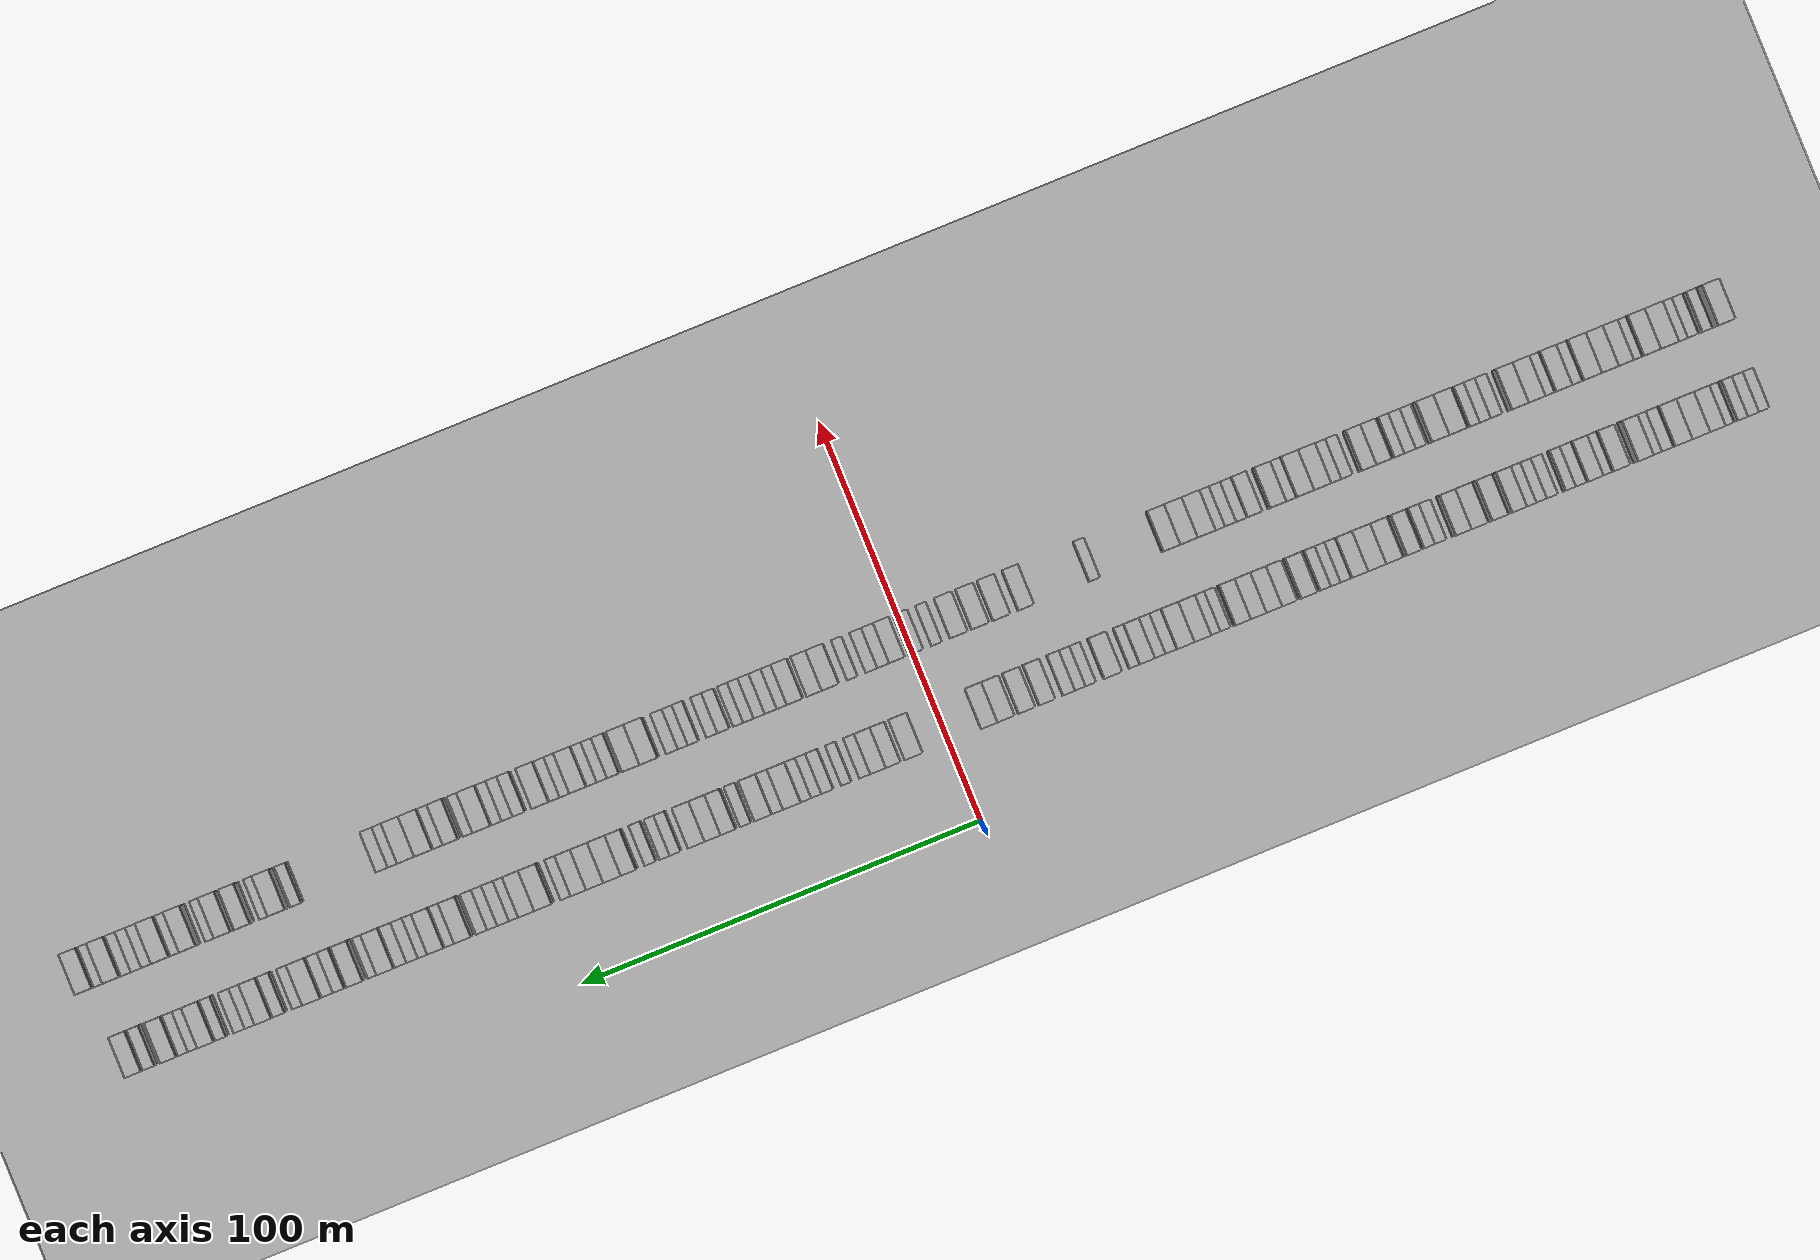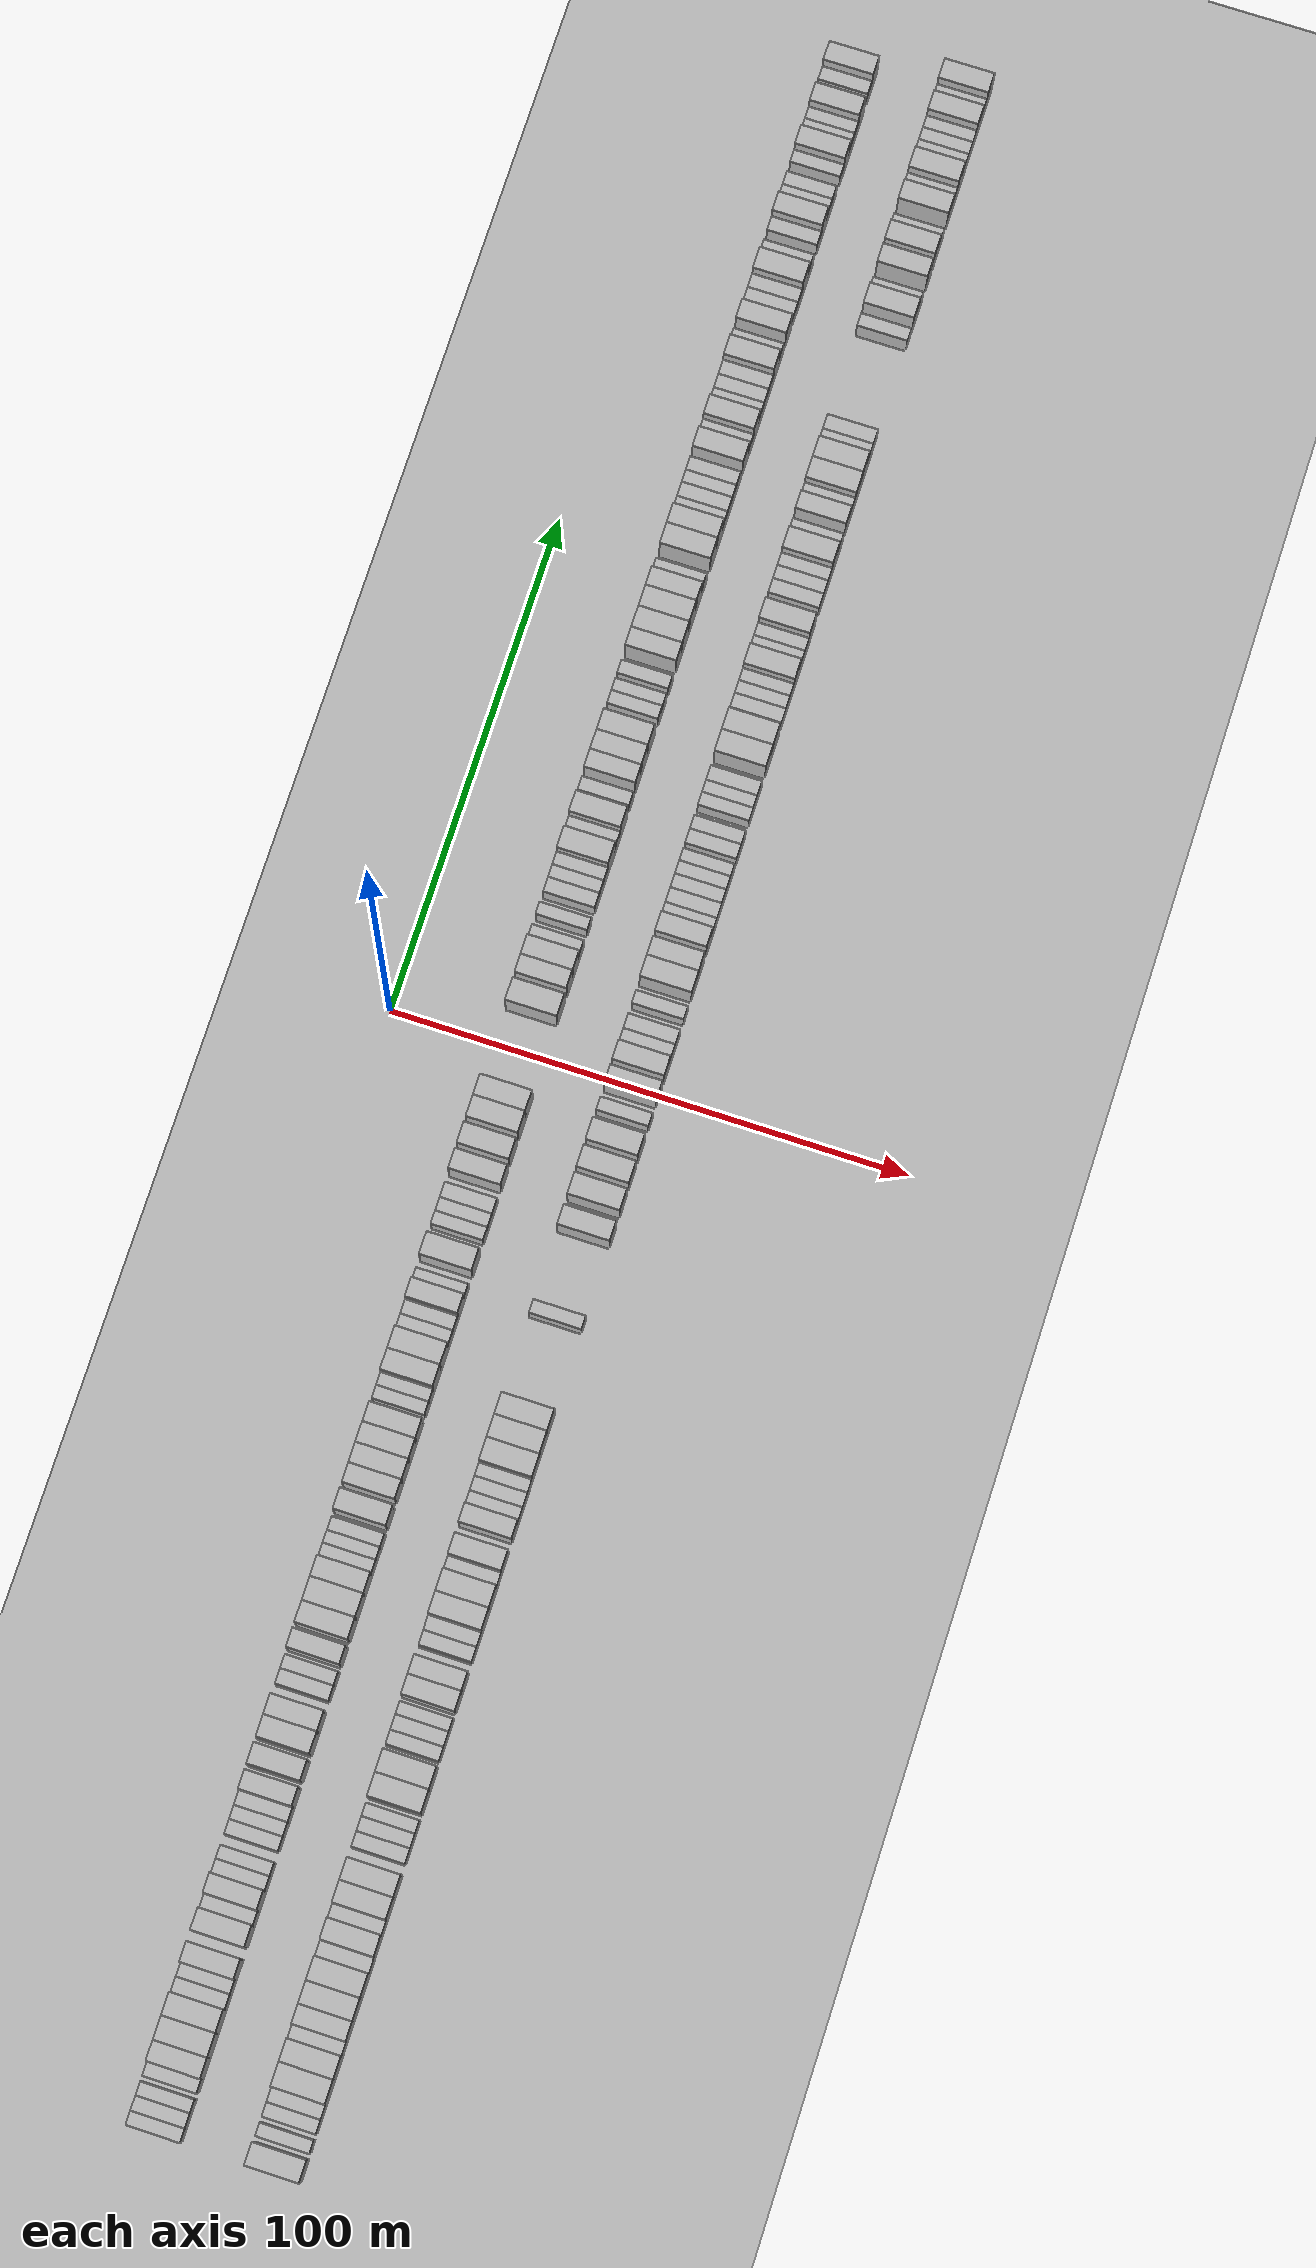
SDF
<?xml version="1.0" encoding="utf-8"?>

<sdf version="1.6">

   <world name="default">

      <gui fullscreen="0">

         <camera name="user_camera">

            <pose>-15 0 4.57585 0 0 0</pose>

            <view_controller>orbit</view_controller>

         </camera>

      </gui>

      <scene>

         <sky>

           <clouds>

             <speed>12</speed>

           </clouds>

         </sky>

         <ambient>0.4 0.4 0.4 1</ambient>

         <background>0.7 0.7 0.7 1</background>

         <shadows>1</shadows>

      </scene>

      <gravity>0 0 -9.8066</gravity>

      <magnetic_field>6e-06 2.3e-05 -4.2e-05</magnetic_field>

      <physics default="0" name="default_physics" type="ode">

         <ode>

            <solver>

               <type>quick</type>

               <iters>10</iters>

               <sor>1.0</sor>

               <use_dynamic_moi_rescaling>0</use_dynamic_moi_rescaling>

            </solver>

            <constraints>

               <cfm>0</cfm>

               <erp>0.2</erp>

               <contact_max_correcting_vel>100</contact_max_correcting_vel>

               <contact_surface_layer>0.001</contact_surface_layer>

            </constraints>

         </ode>

         <max_step_size>0.004</max_step_size>

         <real_time_factor>1</real_time_factor>

         <real_time_update_rate>250</real_time_update_rate>

      </physics>

      <light name="sun" type="directional">

         <cast_shadows>1</cast_shadows>

         <pose>0 0 10 0 0 0</pose>

         <diffuse>0.8 0.8 0.8 1</diffuse>

         <specular>0.2 0.2 0.2 1</specular>

         <attenuation>

            <range>1000</range>

            <constant>0.9</constant>

            <linear>0.01</linear>

            <quadratic>0.001</quadratic>

         </attenuation>

         <direction>-0.5 0.1 -0.9</direction>

      </light>

      <include>

         <name>ground_plane_1</name>

         <uri>model://HANNAS_ground_plane</uri>

         <pose>0 0 0  0 0 0</pose>

      </include>

      <include>

         <name>ground_plane_2</name>

         <uri>model://HANNAS_ground_plane</uri>

         <pose>100 0 0  0 0 0</pose>

      </include>

      <model name="building_1">

         <static>1</static>

         <pose frame="">25.0000 -202.7139 0 0.000000 0.000000 0.000000</pose>

         <link name="link">

            <pose frame="">0 0 3.00 0 0 0</pose>

            <collision name="collision">

               <geometry>

                  <box>

                     <size>10.0000 2.5722 6.0000</size>

                  </box>

               </geometry>

               <max_contacts>10</max_contacts>

               <surface>

                  <contact>

                     <ode/>

                  </contact>

                  <bounce/>

                  <friction>

                     <torsional>

                        <ode/>

                     </torsional>

                     <ode/>

                  </friction>

               </surface>

            </collision>

            <visual name="visual">

               <cast_shadows>0</cast_shadows>

               <geometry>

                  <box>

                     <size>10.0000 2.5722 6.0000</size>

                  </box>

               </geometry>

               <material>

                  <script>

                     <uri>model://HANNAS_wall/materials/scripts</uri>

                     <uri>model://HANNAS_wall/materials/textures</uri>

                     <name>vrc/HANNAS_wall</name>

                  </script>

               </material>

            </visual>

            <self_collide>0</self_collide>

            <enable_wind>0</enable_wind>

            <kinematic>0</kinematic>

         </link>

      </model>

      <model name="building_2">

         <static>1</static>

         <pose frame="">25.0000 -200.0538 0 0.000000 0.000000 0.000000</pose>

         <link name="link">

            <pose frame="">0 0 3.00 0 0 0</pose>

            <collision name="collision">

               <geometry>

                  <box>

                     <size>10.0000 2.7478 6.0000</size>

                  </box>

               </geometry>

               <max_contacts>10</max_contacts>

               <surface>

                  <contact>

                     <ode/>

                  </contact>

                  <bounce/>

                  <friction>

                     <torsional>

                        <ode/>

                     </torsional>

                     <ode/>

                  </friction>

               </surface>

            </collision>

            <visual name="visual">

               <cast_shadows>0</cast_shadows>

               <geometry>

                  <box>

                     <size>10.0000 2.7478 6.0000</size>

                  </box>

               </geometry>

               <material>

                  <script>

                     <uri>model://HANNAS_wall/materials/scripts</uri>

                     <uri>model://HANNAS_wall/materials/textures</uri>

                     <name>vrc/HANNAS_wall</name>

                  </script>

               </material>

            </visual>

            <self_collide>0</self_collide>

            <enable_wind>0</enable_wind>

            <kinematic>0</kinematic>

         </link>

      </model>

      <model name="building_3">

         <static>1</static>

         <pose frame="">25.0000 -197.4349 0 0.000000 0.000000 0.000000</pose>

         <link name="link">

            <pose frame="">0 0 3.00 0 0 0</pose>

            <collision name="collision">

               <geometry>

                  <box>

                     <size>10.0000 2.4899 6.0000</size>

                  </box>

               </geometry>

               <max_contacts>10</max_contacts>

               <surface>

                  <contact>

                     <ode/>

                  </contact>

                  <bounce/>

                  <friction>

                     <torsional>

                        <ode/>

                     </torsional>

                     <ode/>

                  </friction>

               </surface>

            </collision>

            <visual name="visual">

               <cast_shadows>0</cast_shadows>

               <geometry>

                  <box>

                     <size>10.0000 2.4899 6.0000</size>

                  </box>

               </geometry>

               <material>

                  <script>

                     <uri>model://HANNAS_wall/materials/scripts</uri>

                     <uri>model://HANNAS_wall/materials/textures</uri>

                     <name>vrc/HANNAS_wall</name>

                  </script>

               </material>

            </visual>

            <self_collide>0</self_collide>

            <enable_wind>0</enable_wind>

            <kinematic>0</kinematic>

         </link>

      </model>

      <model name="building_4">

         <static>1</static>

         <pose frame="">25.0000 -193.8955 0 0.000000 0.000000 0.000000</pose>

         <link name="link">

            <pose frame="">0 0 3.00 0 0 0</pose>

            <collision name="collision">

               <geometry>

                  <box>

                     <size>10.0000 2.5889 6.0000</size>

                  </box>

               </geometry>

               <max_contacts>10</max_contacts>

               <surface>

                  <contact>

                     <ode/>

                  </contact>

                  <bounce/>

                  <friction>

                     <torsional>

                        <ode/>

                     </torsional>

                     <ode/>

                  </friction>

               </surface>

            </collision>

            <visual name="visual">

               <cast_shadows>0</cast_shadows>

               <geometry>

                  <box>

                     <size>10.0000 2.5889 6.0000</size>

                  </box>

               </geometry>

               <material>

                  <script>

                     <uri>model://HANNAS_wall/materials/scripts</uri>

                     <uri>model://HANNAS_wall/materials/textures</uri>

                     <name>vrc/HANNAS_wall</name>

                  </script>

               </material>

            </visual>

            <self_collide>0</self_collide>

            <enable_wind>0</enable_wind>

            <kinematic>0</kinematic>

         </link>

      </model>

      <model name="building_5">

         <static>1</static>

         <pose frame="">25.0000 -190.6873 0 0.000000 0.000000 0.000000</pose>

         <link name="link">

            <pose frame="">0 0 4.50 0 0 0</pose>

            <collision name="collision">

               <geometry>

                  <box>

                     <size>10.0000 3.8274 9.0000</size>

                  </box>

               </geometry>

               <max_contacts>10</max_contacts>

               <surface>

                  <contact>

                     <ode/>

                  </contact>

                  <bounce/>

                  <friction>

                     <torsional>

                        <ode/>

                     </torsional>

                     <ode/>

                  </friction>

               </surface>

            </collision>

            <visual name="visual">

               <cast_shadows>0</cast_shadows>

               <geometry>

                  <box>

                     <size>10.0000 3.8274 9.0000</size>

                  </box>

               </geometry>

               <material>

                  <script>

                     <uri>model://HANNAS_wall/materials/scripts</uri>

                     <uri>model://HANNAS_wall/materials/textures</uri>

                     <name>vrc/HANNAS_wall</name>

                  </script>

               </material>

            </visual>

            <self_collide>0</self_collide>

            <enable_wind>0</enable_wind>

            <kinematic>0</kinematic>

         </link>

      </model>

      <model name="building_6">

         <static>1</static>

         <pose frame="">25.0000 -186.5824 0 0.000000 0.000000 0.000000</pose>

         <link name="link">

            <pose frame="">0 0 4.50 0 0 0</pose>

            <collision name="collision">

               <geometry>

                  <box>

                     <size>10.0000 4.3826 9.0000</size>

                  </box>

               </geometry>

               <max_contacts>10</max_contacts>

               <surface>

                  <contact>

                     <ode/>

                  </contact>

                  <bounce/>

                  <friction>

                     <torsional>

                        <ode/>

                     </torsional>

                     <ode/>

                  </friction>

               </surface>

            </collision>

            <visual name="visual">

               <cast_shadows>0</cast_shadows>

               <geometry>

                  <box>

                     <size>10.0000 4.3826 9.0000</size>

                  </box>

               </geometry>

               <material>

                  <script>

                     <uri>model://HANNAS_wall/materials/scripts</uri>

                     <uri>model://HANNAS_wall/materials/textures</uri>

                     <name>vrc/HANNAS_wall</name>

                  </script>

               </material>

            </visual>

            <self_collide>0</self_collide>

            <enable_wind>0</enable_wind>

            <kinematic>0</kinematic>

         </link>

      </model>

      <model name="building_7">

         <static>1</static>

         <pose frame="">25.0000 -182.2598 0 0.000000 0.000000 0.000000</pose>

         <link name="link">

            <pose frame="">0 0 4.50 0 0 0</pose>

            <collision name="collision">

               <geometry>

                  <box>

                     <size>10.0000 4.2625 9.0000</size>

                  </box>

               </geometry>

               <max_contacts>10</max_contacts>

               <surface>

                  <contact>

                     <ode/>

                  </contact>

                  <bounce/>

                  <friction>

                     <torsional>

                        <ode/>

                     </torsional>

                     <ode/>

                  </friction>

               </surface>

            </collision>

            <visual name="visual">

               <cast_shadows>0</cast_shadows>

               <geometry>

                  <box>

                     <size>10.0000 4.2625 9.0000</size>

                  </box>

               </geometry>

               <material>

                  <script>

                     <uri>model://HANNAS_wall/materials/scripts</uri>

                     <uri>model://HANNAS_wall/materials/textures</uri>

                     <name>vrc/HANNAS_wall</name>

                  </script>

               </material>

            </visual>

            <self_collide>0</self_collide>

            <enable_wind>0</enable_wind>

            <kinematic>0</kinematic>

         </link>

      </model>

      <model name="building_8">

         <static>1</static>

         <pose frame="">25.0000 -178.7155 0 0.000000 0.000000 0.000000</pose>

         <link name="link">

            <pose frame="">0 0 3.00 0 0 0</pose>

            <collision name="collision">

               <geometry>

                  <box>

                     <size>10.0000 2.8261 6.0000</size>

                  </box>

               </geometry>

               <max_contacts>10</max_contacts>

               <surface>

                  <contact>

                     <ode/>

                  </contact>

                  <bounce/>

                  <friction>

                     <torsional>

                        <ode/>

                     </torsional>

                     <ode/>

                  </friction>

               </surface>

            </collision>

            <visual name="visual">

               <cast_shadows>0</cast_shadows>

               <geometry>

                  <box>

                     <size>10.0000 2.8261 6.0000</size>

                  </box>

               </geometry>

               <material>

                  <script>

                     <uri>model://HANNAS_wall/materials/scripts</uri>

                     <uri>model://HANNAS_wall/materials/textures</uri>

                     <name>vrc/HANNAS_wall</name>

                  </script>

               </material>

            </visual>

            <self_collide>0</self_collide>

            <enable_wind>0</enable_wind>

            <kinematic>0</kinematic>

         </link>

      </model>

      <model name="building_9">

         <static>1</static>

         <pose frame="">25.0000 -176.0333 0 0.000000 0.000000 0.000000</pose>

         <link name="link">

            <pose frame="">0 0 3.00 0 0 0</pose>

            <collision name="collision">

               <geometry>

                  <box>

                     <size>10.0000 2.5383 6.0000</size>

                  </box>

               </geometry>

               <max_contacts>10</max_contacts>

               <surface>

                  <contact>

                     <ode/>

                  </contact>

                  <bounce/>

                  <friction>

                     <torsional>

                        <ode/>

                     </torsional>

                     <ode/>

                  </friction>

               </surface>

            </collision>

            <visual name="visual">

               <cast_shadows>0</cast_shadows>

               <geometry>

                  <box>

                     <size>10.0000 2.5383 6.0000</size>

                  </box>

               </geometry>

               <material>

                  <script>

                     <uri>model://HANNAS_wall/materials/scripts</uri>

                     <uri>model://HANNAS_wall/materials/textures</uri>

                     <name>vrc/HANNAS_wall</name>

                  </script>

               </material>

            </visual>

            <self_collide>0</self_collide>

            <enable_wind>0</enable_wind>

            <kinematic>0</kinematic>

         </link>

      </model>

      <model name="building_10">

         <static>1</static>

         <pose frame="">25.0000 -172.8733 0 0.000000 0.000000 0.000000</pose>

         <link name="link">

            <pose frame="">0 0 4.50 0 0 0</pose>

            <collision name="collision">

               <geometry>

                  <box>

                     <size>10.0000 3.7818 9.0000</size>

                  </box>

               </geometry>

               <max_contacts>10</max_contacts>

               <surface>

                  <contact>

                     <ode/>

                  </contact>

                  <bounce/>

                  <friction>

                     <torsional>

                        <ode/>

                     </torsional>

                     <ode/>

                  </friction>

               </surface>

            </collision>

            <visual name="visual">

               <cast_shadows>0</cast_shadows>

               <geometry>

                  <box>

                     <size>10.0000 3.7818 9.0000</size>

                  </box>

               </geometry>

               <material>

                  <script>

                     <uri>model://HANNAS_wall/materials/scripts</uri>

                     <uri>model://HANNAS_wall/materials/textures</uri>

                     <name>vrc/HANNAS_wall</name>

                  </script>

               </material>

            </visual>

            <self_collide>0</self_collide>

            <enable_wind>0</enable_wind>

            <kinematic>0</kinematic>

         </link>

      </model>

      <model name="building_11">

         <static>1</static>

         <pose frame="">25.0000 -166.9382 0 0.000000 0.000000 0.000000</pose>

         <link name="link">

            <pose frame="">0 0 4.50 0 0 0</pose>

            <collision name="collision">

               <geometry>

                  <box>

                     <size>10.0000 4.0884 9.0000</size>

                  </box>

               </geometry>

               <max_contacts>10</max_contacts>

               <surface>

                  <contact>

                     <ode/>

                  </contact>

                  <bounce/>

                  <friction>

                     <torsional>

                        <ode/>

                     </torsional>

                     <ode/>

                  </friction>

               </surface>

            </collision>

            <visual name="visual">

               <cast_shadows>0</cast_shadows>

               <geometry>

                  <box>

                     <size>10.0000 4.0884 9.0000</size>

                  </box>

               </geometry>

               <material>

                  <script>

                     <uri>model://HANNAS_wall/materials/scripts</uri>

                     <uri>model://HANNAS_wall/materials/textures</uri>

                     <name>vrc/HANNAS_wall</name>

                  </script>

               </material>

            </visual>

            <self_collide>0</self_collide>

            <enable_wind>0</enable_wind>

            <kinematic>0</kinematic>

         </link>

      </model>

      <model name="building_12">

         <static>1</static>

         <pose frame="">25.0000 -163.5967 0 0.000000 0.000000 0.000000</pose>

         <link name="link">

            <pose frame="">0 0 3.00 0 0 0</pose>

            <collision name="collision">

               <geometry>

                  <box>

                     <size>10.0000 2.5944 6.0000</size>

                  </box>

               </geometry>

               <max_contacts>10</max_contacts>

               <surface>

                  <contact>

                     <ode/>

                  </contact>

                  <bounce/>

                  <friction>

                     <torsional>

                        <ode/>

                     </torsional>

                     <ode/>

                  </friction>

               </surface>

            </collision>

            <visual name="visual">

               <cast_shadows>0</cast_shadows>

               <geometry>

                  <box>

                     <size>10.0000 2.5944 6.0000</size>

                  </box>

               </geometry>

               <material>

                  <script>

                     <uri>model://HANNAS_wall/materials/scripts</uri>

                     <uri>model://HANNAS_wall/materials/textures</uri>

                     <name>vrc/HANNAS_wall</name>

                  </script>

               </material>

            </visual>

            <self_collide>0</self_collide>

            <enable_wind>0</enable_wind>

            <kinematic>0</kinematic>

         </link>

      </model>

      <model name="building_13">

         <static>1</static>

         <pose frame="">25.0000 -160.4428 0 0.000000 0.000000 0.000000</pose>

         <link name="link">

            <pose frame="">0 0 4.50 0 0 0</pose>

            <collision name="collision">

               <geometry>

                  <box>

                     <size>10.0000 3.7134 9.0000</size>

                  </box>

               </geometry>

               <max_contacts>10</max_contacts>

               <surface>

                  <contact>

                     <ode/>

                  </contact>

                  <bounce/>

                  <friction>

                     <torsional>

                        <ode/>

                     </torsional>

                     <ode/>

                  </friction>

               </surface>

            </collision>

            <visual name="visual">

               <cast_shadows>0</cast_shadows>

               <geometry>

                  <box>

                     <size>10.0000 3.7134 9.0000</size>

                  </box>

               </geometry>

               <material>

                  <script>

                     <uri>model://HANNAS_wall/materials/scripts</uri>

                     <uri>model://HANNAS_wall/materials/textures</uri>

                     <name>vrc/HANNAS_wall</name>

                  </script>

               </material>

            </visual>

            <self_collide>0</self_collide>

            <enable_wind>0</enable_wind>

            <kinematic>0</kinematic>

         </link>

      </model>

      <model name="building_14">

         <static>1</static>

         <pose frame="">25.0000 -157.2319 0 0.000000 0.000000 0.000000</pose>

         <link name="link">

            <pose frame="">0 0 3.00 0 0 0</pose>

            <collision name="collision">

               <geometry>

                  <box>

                     <size>10.0000 2.7084 6.0000</size>

                  </box>

               </geometry>

               <max_contacts>10</max_contacts>

               <surface>

                  <contact>

                     <ode/>

                  </contact>

                  <bounce/>

                  <friction>

                     <torsional>

                        <ode/>

                     </torsional>

                     <ode/>

                  </friction>

               </surface>

            </collision>

            <visual name="visual">

               <cast_shadows>0</cast_shadows>

               <geometry>

                  <box>

                     <size>10.0000 2.7084 6.0000</size>

                  </box>

               </geometry>

               <material>

                  <script>

                     <uri>model://HANNAS_wall/materials/scripts</uri>

                     <uri>model://HANNAS_wall/materials/textures</uri>

                     <name>vrc/HANNAS_wall</name>

                  </script>

               </material>

            </visual>

            <self_collide>0</self_collide>

            <enable_wind>0</enable_wind>

            <kinematic>0</kinematic>

         </link>

      </model>

      <model name="building_15">

         <static>1</static>

         <pose frame="">25.0000 -154.6331 0 0.000000 0.000000 0.000000</pose>

         <link name="link">

            <pose frame="">0 0 3.00 0 0 0</pose>

            <collision name="collision">

               <geometry>

                  <box>

                     <size>10.0000 2.4892 6.0000</size>

                  </box>

               </geometry>

               <max_contacts>10</max_contacts>

               <surface>

                  <contact>

                     <ode/>

                  </contact>

                  <bounce/>

                  <friction>

                     <torsional>

                        <ode/>

                     </torsional>

                     <ode/>

                  </friction>

               </surface>

            </collision>

            <visual name="visual">

               <cast_shadows>0</cast_shadows>

               <geometry>

                  <box>

                     <size>10.0000 2.4892 6.0000</size>

                  </box>

               </geometry>

               <material>

                  <script>

                     <uri>model://HANNAS_wall/materials/scripts</uri>

                     <uri>model://HANNAS_wall/materials/textures</uri>

                     <name>vrc/HANNAS_wall</name>

                  </script>

               </material>

            </visual>

            <self_collide>0</self_collide>

            <enable_wind>0</enable_wind>

            <kinematic>0</kinematic>

         </link>

      </model>

      <model name="building_16">

         <static>1</static>

         <pose frame="">25.0000 -150.0213 0 0.000000 0.000000 0.000000</pose>

         <link name="link">

            <pose frame="">0 0 3.00 0 0 0</pose>

            <collision name="collision">

               <geometry>

                  <box>

                     <size>10.0000 2.7342 6.0000</size>

                  </box>

               </geometry>

               <max_contacts>10</max_contacts>

               <surface>

                  <contact>

                     <ode/>

                  </contact>

                  <bounce/>

                  <friction>

                     <torsional>

                        <ode/>

                     </torsional>

                     <ode/>

                  </friction>

               </surface>

            </collision>

            <visual name="visual">

               <cast_shadows>0</cast_shadows>

               <geometry>

                  <box>

                     <size>10.0000 2.7342 6.0000</size>

                  </box>

               </geometry>

               <material>

                  <script>

                     <uri>model://HANNAS_wall/materials/scripts</uri>

                     <uri>model://HANNAS_wall/materials/textures</uri>

                     <name>vrc/HANNAS_wall</name>

                  </script>

               </material>

            </visual>

            <self_collide>0</self_collide>

            <enable_wind>0</enable_wind>

            <kinematic>0</kinematic>

         </link>

      </model>

      <model name="building_17">

         <static>1</static>

         <pose frame="">25.0000 -147.3507 0 0.000000 0.000000 0.000000</pose>

         <link name="link">

            <pose frame="">0 0 3.00 0 0 0</pose>

            <collision name="collision">

               <geometry>

                  <box>

                     <size>10.0000 2.6071 6.0000</size>

                  </box>

               </geometry>

               <max_contacts>10</max_contacts>

               <surface>

                  <contact>

                     <ode/>

                  </contact>

                  <bounce/>

                  <friction>

                     <torsional>

                        <ode/>

                     </torsional>

                     <ode/>

                  </friction>

               </surface>

            </collision>

            <visual name="visual">

               <cast_shadows>0</cast_shadows>

               <geometry>

                  <box>

                     <size>10.0000 2.6071 6.0000</size>

                  </box>

               </geometry>

               <material>

                  <script>

                     <uri>model://HANNAS_wall/materials/scripts</uri>

                     <uri>model://HANNAS_wall/materials/textures</uri>

                     <name>vrc/HANNAS_wall</name>

                  </script>

               </material>

            </visual>

            <self_collide>0</self_collide>

            <enable_wind>0</enable_wind>

            <kinematic>0</kinematic>

         </link>

      </model>

      <model name="building_18">

         <static>1</static>

         <pose frame="">25.0000 -144.6837 0 0.000000 0.000000 0.000000</pose>

         <link name="link">

            <pose frame="">0 0 3.00 0 0 0</pose>

            <collision name="collision">

               <geometry>

                  <box>

                     <size>10.0000 2.7267 6.0000</size>

                  </box>

               </geometry>

               <max_contacts>10</max_contacts>

               <surface>

                  <contact>

                     <ode/>

                  </contact>

                  <bounce/>

                  <friction>

                     <torsional>

                        <ode/>

                     </torsional>

                     <ode/>

                  </friction>

               </surface>

            </collision>

            <visual name="visual">

               <cast_shadows>0</cast_shadows>

               <geometry>

                  <box>

                     <size>10.0000 2.7267 6.0000</size>

                  </box>

               </geometry>

               <material>

                  <script>

                     <uri>model://HANNAS_wall/materials/scripts</uri>

                     <uri>model://HANNAS_wall/materials/textures</uri>

                     <name>vrc/HANNAS_wall</name>

                  </script>

               </material>

            </visual>

            <self_collide>0</self_collide>

            <enable_wind>0</enable_wind>

            <kinematic>0</kinematic>

         </link>

      </model>

      <model name="building_19">

         <static>1</static>

         <pose frame="">25.0000 -141.5038 0 0.000000 0.000000 0.000000</pose>

         <link name="link">

            <pose frame="">0 0 4.50 0 0 0</pose>

            <collision name="collision">

               <geometry>

                  <box>

                     <size>10.0000 3.6330 9.0000</size>

                  </box>

               </geometry>

               <max_contacts>10</max_contacts>

               <surface>

                  <contact>

                     <ode/>

                  </contact>

                  <bounce/>

                  <friction>

                     <torsional>

                        <ode/>

                     </torsional>

                     <ode/>

                  </friction>

               </surface>

            </collision>

            <visual name="visual">

               <cast_shadows>0</cast_shadows>

               <geometry>

                  <box>

                     <size>10.0000 3.6330 9.0000</size>

                  </box>

               </geometry>

               <material>

                  <script>

                     <uri>model://HANNAS_wall/materials/scripts</uri>

                     <uri>model://HANNAS_wall/materials/textures</uri>

                     <name>vrc/HANNAS_wall</name>

                  </script>

               </material>

            </visual>

            <self_collide>0</self_collide>

            <enable_wind>0</enable_wind>

            <kinematic>0</kinematic>

         </link>

      </model>

      <model name="building_20">

         <static>1</static>

         <pose frame="">25.0000 -136.7051 0 0.000000 0.000000 0.000000</pose>

         <link name="link">

            <pose frame="">0 0 4.50 0 0 0</pose>

            <collision name="collision">

               <geometry>

                  <box>

                     <size>10.0000 3.9644 9.0000</size>

                  </box>

               </geometry>

               <max_contacts>10</max_contacts>

               <surface>

                  <contact>

                     <ode/>

                  </contact>

                  <bounce/>

                  <friction>

                     <torsional>

                        <ode/>

                     </torsional>

                     <ode/>

                  </friction>

               </surface>

            </collision>

            <visual name="visual">

               <cast_shadows>0</cast_shadows>

               <geometry>

                  <box>

                     <size>10.0000 3.9644 9.0000</size>

                  </box>

               </geometry>

               <material>

                  <script>

                     <uri>model://HANNAS_wall/materials/scripts</uri>

                     <uri>model://HANNAS_wall/materials/textures</uri>

                     <name>vrc/HANNAS_wall</name>

                  </script>

               </material>

            </visual>

            <self_collide>0</self_collide>

            <enable_wind>0</enable_wind>

            <kinematic>0</kinematic>

         </link>

      </model>

      <model name="building_21">

         <static>1</static>

         <pose frame="">25.0000 -131.6395 0 0.000000 0.000000 0.000000</pose>

         <link name="link">

            <pose frame="">0 0 4.50 0 0 0</pose>

            <collision name="collision">

               <geometry>

                  <box>

                     <size>10.0000 4.1667 9.0000</size>

                  </box>

               </geometry>

               <max_contacts>10</max_contacts>

               <surface>

                  <contact>

                     <ode/>

                  </contact>

                  <bounce/>

                  <friction>

                     <torsional>

                        <ode/>

                     </torsional>

                     <ode/>

                  </friction>

               </surface>

            </collision>

            <visual name="visual">

               <cast_shadows>0</cast_shadows>

               <geometry>

                  <box>

                     <size>10.0000 4.1667 9.0000</size>

                  </box>

               </geometry>

               <material>

                  <script>

                     <uri>model://HANNAS_wall/materials/scripts</uri>

                     <uri>model://HANNAS_wall/materials/textures</uri>

                     <name>vrc/HANNAS_wall</name>

                  </script>

               </material>

            </visual>

            <self_collide>0</self_collide>

            <enable_wind>0</enable_wind>

            <kinematic>0</kinematic>

         </link>

      </model>

      <model name="building_22">

         <static>1</static>

         <pose frame="">25.0000 -127.6203 0 0.000000 0.000000 0.000000</pose>

         <link name="link">

            <pose frame="">0 0 4.50 0 0 0</pose>

            <collision name="collision">

               <geometry>

                  <box>

                     <size>10.0000 3.8717 9.0000</size>

                  </box>

               </geometry>

               <max_contacts>10</max_contacts>

               <surface>

                  <contact>

                     <ode/>

                  </contact>

                  <bounce/>

                  <friction>

                     <torsional>

                        <ode/>

                     </torsional>

                     <ode/>

                  </friction>

               </surface>

            </collision>

            <visual name="visual">

               <cast_shadows>0</cast_shadows>

               <geometry>

                  <box>

                     <size>10.0000 3.8717 9.0000</size>

                  </box>

               </geometry>

               <material>

                  <script>

                     <uri>model://HANNAS_wall/materials/scripts</uri>

                     <uri>model://HANNAS_wall/materials/textures</uri>

                     <name>vrc/HANNAS_wall</name>

                  </script>

               </material>

            </visual>

            <self_collide>0</self_collide>

            <enable_wind>0</enable_wind>

            <kinematic>0</kinematic>

         </link>

      </model>

      <model name="building_23">

         <static>1</static>

         <pose frame="">25.0000 -122.2472 0 0.000000 0.000000 0.000000</pose>

         <link name="link">

            <pose frame="">0 0 3.00 0 0 0</pose>

            <collision name="collision">

               <geometry>

                  <box>

                     <size>10.0000 2.8745 6.0000</size>

                  </box>

               </geometry>

               <max_contacts>10</max_contacts>

               <surface>

                  <contact>

                     <ode/>

                  </contact>

                  <bounce/>

                  <friction>

                     <torsional>

                        <ode/>

                     </torsional>

                     <ode/>

                  </friction>

               </surface>

            </collision>

            <visual name="visual">

               <cast_shadows>0</cast_shadows>

               <geometry>

                  <box>

                     <size>10.0000 2.8745 6.0000</size>

                  </box>

               </geometry>

               <material>

                  <script>

                     <uri>model://HANNAS_wall/materials/scripts</uri>

                     <uri>model://HANNAS_wall/materials/textures</uri>

                     <name>vrc/HANNAS_wall</name>

                  </script>

               </material>

            </visual>

            <self_collide>0</self_collide>

            <enable_wind>0</enable_wind>

            <kinematic>0</kinematic>

         </link>

      </model>

      <model name="building_24">

         <static>1</static>

         <pose frame="">25.0000 -119.4918 0 0.000000 0.000000 0.000000</pose>

         <link name="link">

            <pose frame="">0 0 3.00 0 0 0</pose>

            <collision name="collision">

               <geometry>

                  <box>

                     <size>10.0000 2.6363 6.0000</size>

                  </box>

               </geometry>

               <max_contacts>10</max_contacts>

               <surface>

                  <contact>

                     <ode/>

                  </contact>

                  <bounce/>

                  <friction>

                     <torsional>

                        <ode/>

                     </torsional>

                     <ode/>

                  </friction>

               </surface>

            </collision>

            <visual name="visual">

               <cast_shadows>0</cast_shadows>

               <geometry>

                  <box>

                     <size>10.0000 2.6363 6.0000</size>

                  </box>

               </geometry>

               <material>

                  <script>

                     <uri>model://HANNAS_wall/materials/scripts</uri>

                     <uri>model://HANNAS_wall/materials/textures</uri>

                     <name>vrc/HANNAS_wall</name>

                  </script>

               </material>

            </visual>

            <self_collide>0</self_collide>

            <enable_wind>0</enable_wind>

            <kinematic>0</kinematic>

         </link>

      </model>

      <model name="building_25">

         <static>1</static>

         <pose frame="">25.0000 -115.3635 0 0.000000 0.000000 0.000000</pose>

         <link name="link">

            <pose frame="">0 0 4.50 0 0 0</pose>

            <collision name="collision">

               <geometry>

                  <box>

                     <size>10.0000 3.6204 9.0000</size>

                  </box>

               </geometry>

               <max_contacts>10</max_contacts>

               <surface>

                  <contact>

                     <ode/>

                  </contact>

                  <bounce/>

                  <friction>

                     <torsional>

                        <ode/>

                     </torsional>

                     <ode/>

                  </friction>

               </surface>

            </collision>

            <visual name="visual">

               <cast_shadows>0</cast_shadows>

               <geometry>

                  <box>

                     <size>10.0000 3.6204 9.0000</size>

                  </box>

               </geometry>

               <material>

                  <script>

                     <uri>model://HANNAS_wall/materials/scripts</uri>

                     <uri>model://HANNAS_wall/materials/textures</uri>

                     <name>vrc/HANNAS_wall</name>

                  </script>

               </material>

            </visual>

            <self_collide>0</self_collide>

            <enable_wind>0</enable_wind>

            <kinematic>0</kinematic>

         </link>

      </model>

      <model name="building_26">

         <static>1</static>

         <pose frame="">25.0000 -110.4775 0 0.000000 0.000000 0.000000</pose>

         <link name="link">

            <pose frame="">0 0 4.50 0 0 0</pose>

            <collision name="collision">

               <geometry>

                  <box>

                     <size>10.0000 4.1515 9.0000</size>

                  </box>

               </geometry>

               <max_contacts>10</max_contacts>

               <surface>

                  <contact>

                     <ode/>

                  </contact>

                  <bounce/>

                  <friction>

                     <torsional>

                        <ode/>

                     </torsional>

                     <ode/>

                  </friction>

               </surface>

            </collision>

            <visual name="visual">

               <cast_shadows>0</cast_shadows>

               <geometry>

                  <box>

                     <size>10.0000 4.1515 9.0000</size>

                  </box>

               </geometry>

               <material>

                  <script>

                     <uri>model://HANNAS_wall/materials/scripts</uri>

                     <uri>model://HANNAS_wall/materials/textures</uri>

                     <name>vrc/HANNAS_wall</name>

                  </script>

               </material>

            </visual>

            <self_collide>0</self_collide>

            <enable_wind>0</enable_wind>

            <kinematic>0</kinematic>

         </link>

      </model>

      <model name="building_27">

         <static>1</static>

         <pose frame="">25.0000 -106.1570 0 0.000000 0.000000 0.000000</pose>

         <link name="link">

            <pose frame="">0 0 4.50 0 0 0</pose>

            <collision name="collision">

               <geometry>

                  <box>

                     <size>10.0000 4.4896 9.0000</size>

                  </box>

               </geometry>

               <max_contacts>10</max_contacts>

               <surface>

                  <contact>

                     <ode/>

                  </contact>

                  <bounce/>

                  <friction>

                     <torsional>

                        <ode/>

                     </torsional>

                     <ode/>

                  </friction>

               </surface>

            </collision>

            <visual name="visual">

               <cast_shadows>0</cast_shadows>

               <geometry>

                  <box>

                     <size>10.0000 4.4896 9.0000</size>

                  </box>

               </geometry>

               <material>

                  <script>

                     <uri>model://HANNAS_wall/materials/scripts</uri>

                     <uri>model://HANNAS_wall/materials/textures</uri>

                     <name>vrc/HANNAS_wall</name>

                  </script>

               </material>

            </visual>

            <self_collide>0</self_collide>

            <enable_wind>0</enable_wind>

            <kinematic>0</kinematic>

         </link>

      </model>

      <model name="building_28">

         <static>1</static>

         <pose frame="">25.0000 -101.9284 0 0.000000 0.000000 0.000000</pose>

         <link name="link">

            <pose frame="">0 0 4.50 0 0 0</pose>

            <collision name="collision">

               <geometry>

                  <box>

                     <size>10.0000 3.9677 9.0000</size>

                  </box>

               </geometry>

               <max_contacts>10</max_contacts>

               <surface>

                  <contact>

                     <ode/>

                  </contact>

                  <bounce/>

                  <friction>

                     <torsional>

                        <ode/>

                     </torsional>

                     <ode/>

                  </friction>

               </surface>

            </collision>

            <visual name="visual">

               <cast_shadows>0</cast_shadows>

               <geometry>

                  <box>

                     <size>10.0000 3.9677 9.0000</size>

                  </box>

               </geometry>

               <material>

                  <script>

                     <uri>model://HANNAS_wall/materials/scripts</uri>

                     <uri>model://HANNAS_wall/materials/textures</uri>

                     <name>vrc/HANNAS_wall</name>

                  </script>

               </material>

            </visual>

            <self_collide>0</self_collide>

            <enable_wind>0</enable_wind>

            <kinematic>0</kinematic>

         </link>

      </model>

      <model name="building_29">

         <static>1</static>

         <pose frame="">25.0000 -98.6399 0 0.000000 0.000000 0.000000</pose>

         <link name="link">

            <pose frame="">0 0 3.00 0 0 0</pose>

            <collision name="collision">

               <geometry>

                  <box>

                     <size>10.0000 2.6093 6.0000</size>

                  </box>

               </geometry>

               <max_contacts>10</max_contacts>

               <surface>

                  <contact>

                     <ode/>

                  </contact>

                  <bounce/>

                  <friction>

                     <torsional>

                        <ode/>

                     </torsional>

                     <ode/>

                  </friction>

               </surface>

            </collision>

            <visual name="visual">

               <cast_shadows>0</cast_shadows>

               <geometry>

                  <box>

                     <size>10.0000 2.6093 6.0000</size>

                  </box>

               </geometry>

               <material>

                  <script>

                     <uri>model://HANNAS_wall/materials/scripts</uri>

                     <uri>model://HANNAS_wall/materials/textures</uri>

                     <name>vrc/HANNAS_wall</name>

                  </script>

               </material>

            </visual>

            <self_collide>0</self_collide>

            <enable_wind>0</enable_wind>

            <kinematic>0</kinematic>

         </link>

      </model>

      <model name="building_30">

         <static>1</static>

         <pose frame="">25.0000 -96.1334 0 0.000000 0.000000 0.000000</pose>

         <link name="link">

            <pose frame="">0 0 3.00 0 0 0</pose>

            <collision name="collision">

               <geometry>

                  <box>

                     <size>10.0000 2.4037 6.0000</size>

                  </box>

               </geometry>

               <max_contacts>10</max_contacts>

               <surface>

                  <contact>

                     <ode/>

                  </contact>

                  <bounce/>

                  <friction>

                     <torsional>

                        <ode/>

                     </torsional>

                     <ode/>

                  </friction>

               </surface>

            </collision>

            <visual name="visual">

               <cast_shadows>0</cast_shadows>

               <geometry>

                  <box>

                     <size>10.0000 2.4037 6.0000</size>

                  </box>

               </geometry>

               <material>

                  <script>

                     <uri>model://HANNAS_wall/materials/scripts</uri>

                     <uri>model://HANNAS_wall/materials/textures</uri>

                     <name>vrc/HANNAS_wall</name>

                  </script>

               </material>

            </visual>

            <self_collide>0</self_collide>

            <enable_wind>0</enable_wind>

            <kinematic>0</kinematic>

         </link>

      </model>

      <model name="building_31">

         <static>1</static>

         <pose frame="">25.0000 -93.6312 0 0.000000 0.000000 0.000000</pose>

         <link name="link">

            <pose frame="">0 0 3.00 0 0 0</pose>

            <collision name="collision">

               <geometry>

                  <box>

                     <size>10.0000 2.6006 6.0000</size>

                  </box>

               </geometry>

               <max_contacts>10</max_contacts>

               <surface>

                  <contact>

                     <ode/>

                  </contact>

                  <bounce/>

                  <friction>

                     <torsional>

                        <ode/>

                     </torsional>

                     <ode/>

                  </friction>

               </surface>

            </collision>

            <visual name="visual">

               <cast_shadows>0</cast_shadows>

               <geometry>

                  <box>

                     <size>10.0000 2.6006 6.0000</size>

                  </box>

               </geometry>

               <material>

                  <script>

                     <uri>model://HANNAS_wall/materials/scripts</uri>

                     <uri>model://HANNAS_wall/materials/textures</uri>

                     <name>vrc/HANNAS_wall</name>

                  </script>

               </material>

            </visual>

            <self_collide>0</self_collide>

            <enable_wind>0</enable_wind>

            <kinematic>0</kinematic>

         </link>

      </model>

      <model name="building_32">

         <static>1</static>

         <pose frame="">25.0000 -89.3238 0 0.000000 0.000000 0.000000</pose>

         <link name="link">

            <pose frame="">0 0 4.50 0 0 0</pose>

            <collision name="collision">

               <geometry>

                  <box>

                     <size>10.0000 4.0141 9.0000</size>

                  </box>

               </geometry>

               <max_contacts>10</max_contacts>

               <surface>

                  <contact>

                     <ode/>

                  </contact>

                  <bounce/>

                  <friction>

                     <torsional>

                        <ode/>

                     </torsional>

                     <ode/>

                  </friction>

               </surface>

            </collision>

            <visual name="visual">

               <cast_shadows>0</cast_shadows>

               <geometry>

                  <box>

                     <size>10.0000 4.0141 9.0000</size>

                  </box>

               </geometry>

               <material>

                  <script>

                     <uri>model://HANNAS_wall/materials/scripts</uri>

                     <uri>model://HANNAS_wall/materials/textures</uri>

                     <name>vrc/HANNAS_wall</name>

                  </script>

               </material>

            </visual>

            <self_collide>0</self_collide>

            <enable_wind>0</enable_wind>

            <kinematic>0</kinematic>

         </link>

      </model>

      <model name="building_33">

         <static>1</static>

         <pose frame="">25.0000 -84.4462 0 0.000000 0.000000 0.000000</pose>

         <link name="link">

            <pose frame="">0 0 4.50 0 0 0</pose>

            <collision name="collision">

               <geometry>

                  <box>

                     <size>10.0000 3.7413 9.0000</size>

                  </box>

               </geometry>

               <max_contacts>10</max_contacts>

               <surface>

                  <contact>

                     <ode/>

                  </contact>

                  <bounce/>

                  <friction>

                     <torsional>

                        <ode/>

                     </torsional>

                     <ode/>

                  </friction>

               </surface>

            </collision>

            <visual name="visual">

               <cast_shadows>0</cast_shadows>

               <geometry>

                  <box>

                     <size>10.0000 3.7413 9.0000</size>

                  </box>

               </geometry>

               <material>

                  <script>

                     <uri>model://HANNAS_wall/materials/scripts</uri>

                     <uri>model://HANNAS_wall/materials/textures</uri>

                     <name>vrc/HANNAS_wall</name>

                  </script>

               </material>

            </visual>

            <self_collide>0</self_collide>

            <enable_wind>0</enable_wind>

            <kinematic>0</kinematic>

         </link>

      </model>

      <model name="building_34">

         <static>1</static>

         <pose frame="">25.0000 -80.6337 0 0.000000 0.000000 0.000000</pose>

         <link name="link">

            <pose frame="">0 0 4.50 0 0 0</pose>

            <collision name="collision">

               <geometry>

                  <box>

                     <size>10.0000 3.8836 9.0000</size>

                  </box>

               </geometry>

               <max_contacts>10</max_contacts>

               <surface>

                  <contact>

                     <ode/>

                  </contact>

                  <bounce/>

                  <friction>

                     <torsional>

                        <ode/>

                     </torsional>

                     <ode/>

                  </friction>

               </surface>

            </collision>

            <visual name="visual">

               <cast_shadows>0</cast_shadows>

               <geometry>

                  <box>

                     <size>10.0000 3.8836 9.0000</size>

                  </box>

               </geometry>

               <material>

                  <script>

                     <uri>model://HANNAS_wall/materials/scripts</uri>

                     <uri>model://HANNAS_wall/materials/textures</uri>

                     <name>vrc/HANNAS_wall</name>

                  </script>

               </material>

            </visual>

            <self_collide>0</self_collide>

            <enable_wind>0</enable_wind>

            <kinematic>0</kinematic>

         </link>

      </model>

      <model name="building_35">

         <static>1</static>

         <pose frame="">25.0000 -76.7414 0 0.000000 0.000000 0.000000</pose>

         <link name="link">

            <pose frame="">0 0 4.50 0 0 0</pose>

            <collision name="collision">

               <geometry>

                  <box>

                     <size>10.0000 3.9010 9.0000</size>

                  </box>

               </geometry>

               <max_contacts>10</max_contacts>

               <surface>

                  <contact>

                     <ode/>

                  </contact>

                  <bounce/>

                  <friction>

                     <torsional>

                        <ode/>

                     </torsional>

                     <ode/>

                  </friction>

               </surface>

            </collision>

            <visual name="visual">

               <cast_shadows>0</cast_shadows>

               <geometry>

                  <box>

                     <size>10.0000 3.9010 9.0000</size>

                  </box>

               </geometry>

               <material>

                  <script>

                     <uri>model://HANNAS_wall/materials/scripts</uri>

                     <uri>model://HANNAS_wall/materials/textures</uri>

                     <name>vrc/HANNAS_wall</name>

                  </script>

               </material>

            </visual>

            <self_collide>0</self_collide>

            <enable_wind>0</enable_wind>

            <kinematic>0</kinematic>

         </link>

      </model>

      <model name="building_36">

         <static>1</static>

         <pose frame="">25.0000 -72.8850 0 0.000000 0.000000 0.000000</pose>

         <link name="link">

            <pose frame="">0 0 4.50 0 0 0</pose>

            <collision name="collision">

               <geometry>

                  <box>

                     <size>10.0000 3.8118 9.0000</size>

                  </box>

               </geometry>

               <max_contacts>10</max_contacts>

               <surface>

                  <contact>

                     <ode/>

                  </contact>

                  <bounce/>

                  <friction>

                     <torsional>

                        <ode/>

                     </torsional>

                     <ode/>

                  </friction>

               </surface>

            </collision>

            <visual name="visual">

               <cast_shadows>0</cast_shadows>

               <geometry>

                  <box>

                     <size>10.0000 3.8118 9.0000</size>

                  </box>

               </geometry>

               <material>

                  <script>

                     <uri>model://HANNAS_wall/materials/scripts</uri>

                     <uri>model://HANNAS_wall/materials/textures</uri>

                     <name>vrc/HANNAS_wall</name>

                  </script>

               </material>

            </visual>

            <self_collide>0</self_collide>

            <enable_wind>0</enable_wind>

            <kinematic>0</kinematic>

         </link>

      </model>

      <model name="building_37">

         <static>1</static>

         <pose frame="">25.0000 -68.7060 0 0.000000 0.000000 0.000000</pose>

         <link name="link">

            <pose frame="">0 0 3.00 0 0 0</pose>

            <collision name="collision">

               <geometry>

                  <box>

                     <size>10.0000 2.5461 6.0000</size>

                  </box>

               </geometry>

               <max_contacts>10</max_contacts>

               <surface>

                  <contact>

                     <ode/>

                  </contact>

                  <bounce/>

                  <friction>

                     <torsional>

                        <ode/>

                     </torsional>

                     <ode/>

                  </friction>

               </surface>

            </collision>

            <visual name="visual">

               <cast_shadows>0</cast_shadows>

               <geometry>

                  <box>

                     <size>10.0000 2.5461 6.0000</size>

                  </box>

               </geometry>

               <material>

                  <script>

                     <uri>model://HANNAS_wall/materials/scripts</uri>

                     <uri>model://HANNAS_wall/materials/textures</uri>

                     <name>vrc/HANNAS_wall</name>

                  </script>

               </material>

            </visual>

            <self_collide>0</self_collide>

            <enable_wind>0</enable_wind>

            <kinematic>0</kinematic>

         </link>

      </model>

      <model name="building_38">

         <static>1</static>

         <pose frame="">25.0000 -66.1993 0 0.000000 0.000000 0.000000</pose>

         <link name="link">

            <pose frame="">0 0 3.00 0 0 0</pose>

            <collision name="collision">

               <geometry>

                  <box>

                     <size>10.0000 2.4673 6.0000</size>

                  </box>

               </geometry>

               <max_contacts>10</max_contacts>

               <surface>

                  <contact>

                     <ode/>

                  </contact>

                  <bounce/>

                  <friction>

                     <torsional>

                        <ode/>

                     </torsional>

                     <ode/>

                  </friction>

               </surface>

            </collision>

            <visual name="visual">

               <cast_shadows>0</cast_shadows>

               <geometry>

                  <box>

                     <size>10.0000 2.4673 6.0000</size>

                  </box>

               </geometry>

               <material>

                  <script>

                     <uri>model://HANNAS_wall/materials/scripts</uri>

                     <uri>model://HANNAS_wall/materials/textures</uri>

                     <name>vrc/HANNAS_wall</name>

                  </script>

               </material>

            </visual>

            <self_collide>0</self_collide>

            <enable_wind>0</enable_wind>

            <kinematic>0</kinematic>

         </link>

      </model>

      <model name="building_39">

         <static>1</static>

         <pose frame="">25.0000 -62.8955 0 0.000000 0.000000 0.000000</pose>

         <link name="link">

            <pose frame="">0 0 4.50 0 0 0</pose>

            <collision name="collision">

               <geometry>

                  <box>

                     <size>10.0000 4.1402 9.0000</size>

                  </box>

               </geometry>

               <max_contacts>10</max_contacts>

               <surface>

                  <contact>

                     <ode/>

                  </contact>

                  <bounce/>

                  <friction>

                     <torsional>

                        <ode/>

                     </torsional>

                     <ode/>

                  </friction>

               </surface>

            </collision>

            <visual name="visual">

               <cast_shadows>0</cast_shadows>

               <geometry>

                  <box>

                     <size>10.0000 4.1402 9.0000</size>

                  </box>

               </geometry>

               <material>

                  <script>

                     <uri>model://HANNAS_wall/materials/scripts</uri>

                     <uri>model://HANNAS_wall/materials/textures</uri>

                     <name>vrc/HANNAS_wall</name>

                  </script>

               </material>

            </visual>

            <self_collide>0</self_collide>

            <enable_wind>0</enable_wind>

            <kinematic>0</kinematic>

         </link>

      </model>

      <model name="building_40">

         <static>1</static>

         <pose frame="">25.0000 -58.6949 0 0.000000 0.000000 0.000000</pose>

         <link name="link">

            <pose frame="">0 0 4.50 0 0 0</pose>

            <collision name="collision">

               <geometry>

                  <box>

                     <size>10.0000 4.2610 9.0000</size>

                  </box>

               </geometry>

               <max_contacts>10</max_contacts>

               <surface>

                  <contact>

                     <ode/>

                  </contact>

                  <bounce/>

                  <friction>

                     <torsional>

                        <ode/>

                     </torsional>

                     <ode/>

                  </friction>

               </surface>

            </collision>

            <visual name="visual">

               <cast_shadows>0</cast_shadows>

               <geometry>

                  <box>

                     <size>10.0000 4.2610 9.0000</size>

                  </box>

               </geometry>

               <material>

                  <script>

                     <uri>model://HANNAS_wall/materials/scripts</uri>

                     <uri>model://HANNAS_wall/materials/textures</uri>

                     <name>vrc/HANNAS_wall</name>

                  </script>

               </material>

            </visual>

            <self_collide>0</self_collide>

            <enable_wind>0</enable_wind>

            <kinematic>0</kinematic>

         </link>

      </model>

      <model name="building_41">

         <static>1</static>

         <pose frame="">25.0000 -55.1696 0 0.000000 0.000000 0.000000</pose>

         <link name="link">

            <pose frame="">0 0 3.00 0 0 0</pose>

            <collision name="collision">

               <geometry>

                  <box>

                     <size>10.0000 2.7897 6.0000</size>

                  </box>

               </geometry>

               <max_contacts>10</max_contacts>

               <surface>

                  <contact>

                     <ode/>

                  </contact>

                  <bounce/>

                  <friction>

                     <torsional>

                        <ode/>

                     </torsional>

                     <ode/>

                  </friction>

               </surface>

            </collision>

            <visual name="visual">

               <cast_shadows>0</cast_shadows>

               <geometry>

                  <box>

                     <size>10.0000 2.7897 6.0000</size>

                  </box>

               </geometry>

               <material>

                  <script>

                     <uri>model://HANNAS_wall/materials/scripts</uri>

                     <uri>model://HANNAS_wall/materials/textures</uri>

                     <name>vrc/HANNAS_wall</name>

                  </script>

               </material>

            </visual>

            <self_collide>0</self_collide>

            <enable_wind>0</enable_wind>

            <kinematic>0</kinematic>

         </link>

      </model>

      <model name="building_42">

         <static>1</static>

         <pose frame="">25.0000 -52.3973 0 0.000000 0.000000 0.000000</pose>

         <link name="link">

            <pose frame="">0 0 3.00 0 0 0</pose>

            <collision name="collision">

               <geometry>

                  <box>

                     <size>10.0000 2.7547 6.0000</size>

                  </box>

               </geometry>

               <max_contacts>10</max_contacts>

               <surface>

                  <contact>

                     <ode/>

                  </contact>

                  <bounce/>

                  <friction>

                     <torsional>

                        <ode/>

                     </torsional>

                     <ode/>

                  </friction>

               </surface>

            </collision>

            <visual name="visual">

               <cast_shadows>0</cast_shadows>

               <geometry>

                  <box>

                     <size>10.0000 2.7547 6.0000</size>

                  </box>

               </geometry>

               <material>

                  <script>

                     <uri>model://HANNAS_wall/materials/scripts</uri>

                     <uri>model://HANNAS_wall/materials/textures</uri>

                     <name>vrc/HANNAS_wall</name>

                  </script>

               </material>

            </visual>

            <self_collide>0</self_collide>

            <enable_wind>0</enable_wind>

            <kinematic>0</kinematic>

         </link>

      </model>

      <model name="building_43">

         <static>1</static>

         <pose frame="">25.0000 -49.1457 0 0.000000 0.000000 0.000000</pose>

         <link name="link">

            <pose frame="">0 0 4.50 0 0 0</pose>

            <collision name="collision">

               <geometry>

                  <box>

                     <size>10.0000 3.7485 9.0000</size>

                  </box>

               </geometry>

               <max_contacts>10</max_contacts>

               <surface>

                  <contact>

                     <ode/>

                  </contact>

                  <bounce/>

                  <friction>

                     <torsional>

                        <ode/>

                     </torsional>

                     <ode/>

                  </friction>

               </surface>

            </collision>

            <visual name="visual">

               <cast_shadows>0</cast_shadows>

               <geometry>

                  <box>

                     <size>10.0000 3.7485 9.0000</size>

                  </box>

               </geometry>

               <material>

                  <script>

                     <uri>model://HANNAS_wall/materials/scripts</uri>

                     <uri>model://HANNAS_wall/materials/textures</uri>

                     <name>vrc/HANNAS_wall</name>

                  </script>

               </material>

            </visual>

            <self_collide>0</self_collide>

            <enable_wind>0</enable_wind>

            <kinematic>0</kinematic>

         </link>

      </model>

      <model name="building_44">

         <static>1</static>

         <pose frame="">25.0000 -46.0696 0 0.000000 0.000000 0.000000</pose>

         <link name="link">

            <pose frame="">0 0 3.00 0 0 0</pose>

            <collision name="collision">

               <geometry>

                  <box>

                     <size>10.0000 2.4039 6.0000</size>

                  </box>

               </geometry>

               <max_contacts>10</max_contacts>

               <surface>

                  <contact>

                     <ode/>

                  </contact>

                  <bounce/>

                  <friction>

                     <torsional>

                        <ode/>

                     </torsional>

                     <ode/>

                  </friction>

               </surface>

            </collision>

            <visual name="visual">

               <cast_shadows>0</cast_shadows>

               <geometry>

                  <box>

                     <size>10.0000 2.4039 6.0000</size>

                  </box>

               </geometry>

               <material>

                  <script>

                     <uri>model://HANNAS_wall/materials/scripts</uri>

                     <uri>model://HANNAS_wall/materials/textures</uri>

                     <name>vrc/HANNAS_wall</name>

                  </script>

               </material>

            </visual>

            <self_collide>0</self_collide>

            <enable_wind>0</enable_wind>

            <kinematic>0</kinematic>

         </link>

      </model>

      <model name="building_45">

         <static>1</static>

         <pose frame="">25.0000 -40.6697 0 0.000000 0.000000 0.000000</pose>

         <link name="link">

            <pose frame="">0 0 4.50 0 0 0</pose>

            <collision name="collision">

               <geometry>

                  <box>

                     <size>10.0000 4.3959 9.0000</size>

                  </box>

               </geometry>

               <max_contacts>10</max_contacts>

               <surface>

                  <contact>

                     <ode/>

                  </contact>

                  <bounce/>

                  <friction>

                     <torsional>

                        <ode/>

                     </torsional>

                     <ode/>

                  </friction>

               </surface>

            </collision>

            <visual name="visual">

               <cast_shadows>0</cast_shadows>

               <geometry>

                  <box>

                     <size>10.0000 4.3959 9.0000</size>

                  </box>

               </geometry>

               <material>

                  <script>

                     <uri>model://HANNAS_wall/materials/scripts</uri>

                     <uri>model://HANNAS_wall/materials/textures</uri>

                     <name>vrc/HANNAS_wall</name>

                  </script>

               </material>

            </visual>

            <self_collide>0</self_collide>

            <enable_wind>0</enable_wind>

            <kinematic>0</kinematic>

         </link>

      </model>

      <model name="building_46">

         <static>1</static>

         <pose frame="">25.0000 -35.1803 0 0.000000 0.000000 0.000000</pose>

         <link name="link">

            <pose frame="">0 0 3.00 0 0 0</pose>

            <collision name="collision">

               <geometry>

                  <box>

                     <size>10.0000 2.5829 6.0000</size>

                  </box>

               </geometry>

               <max_contacts>10</max_contacts>

               <surface>

                  <contact>

                     <ode/>

                  </contact>

                  <bounce/>

                  <friction>

                     <torsional>

                        <ode/>

                     </torsional>

                     <ode/>

                  </friction>

               </surface>

            </collision>

            <visual name="visual">

               <cast_shadows>0</cast_shadows>

               <geometry>

                  <box>

                     <size>10.0000 2.5829 6.0000</size>

                  </box>

               </geometry>

               <material>

                  <script>

                     <uri>model://HANNAS_wall/materials/scripts</uri>

                     <uri>model://HANNAS_wall/materials/textures</uri>

                     <name>vrc/HANNAS_wall</name>

                  </script>

               </material>

            </visual>

            <self_collide>0</self_collide>

            <enable_wind>0</enable_wind>

            <kinematic>0</kinematic>

         </link>

      </model>

      <model name="building_47">

         <static>1</static>

         <pose frame="">25.0000 -32.5842 0 0.000000 0.000000 0.000000</pose>

         <link name="link">

            <pose frame="">0 0 3.00 0 0 0</pose>

            <collision name="collision">

               <geometry>

                  <box>

                     <size>10.0000 2.6093 6.0000</size>

                  </box>

               </geometry>

               <max_contacts>10</max_contacts>

               <surface>

                  <contact>

                     <ode/>

                  </contact>

                  <bounce/>

                  <friction>

                     <torsional>

                        <ode/>

                     </torsional>

                     <ode/>

                  </friction>

               </surface>

            </collision>

            <visual name="visual">

               <cast_shadows>0</cast_shadows>

               <geometry>

                  <box>

                     <size>10.0000 2.6093 6.0000</size>

                  </box>

               </geometry>

               <material>

                  <script>

                     <uri>model://HANNAS_wall/materials/scripts</uri>

                     <uri>model://HANNAS_wall/materials/textures</uri>

                     <name>vrc/HANNAS_wall</name>

                  </script>

               </material>

            </visual>

            <self_collide>0</self_collide>

            <enable_wind>0</enable_wind>

            <kinematic>0</kinematic>

         </link>

      </model>

      <model name="building_48">

         <static>1</static>

         <pose frame="">25.0000 -29.7806 0 0.000000 0.000000 0.000000</pose>

         <link name="link">

            <pose frame="">0 0 3.00 0 0 0</pose>

            <collision name="collision">

               <geometry>

                  <box>

                     <size>10.0000 2.9979 6.0000</size>

                  </box>

               </geometry>

               <max_contacts>10</max_contacts>

               <surface>

                  <contact>

                     <ode/>

                  </contact>

                  <bounce/>

                  <friction>

                     <torsional>

                        <ode/>

                     </torsional>

                     <ode/>

                  </friction>

               </surface>

            </collision>

            <visual name="visual">

               <cast_shadows>0</cast_shadows>

               <geometry>

                  <box>

                     <size>10.0000 2.9979 6.0000</size>

                  </box>

               </geometry>

               <material>

                  <script>

                     <uri>model://HANNAS_wall/materials/scripts</uri>

                     <uri>model://HANNAS_wall/materials/textures</uri>

                     <name>vrc/HANNAS_wall</name>

                  </script>

               </material>

            </visual>

            <self_collide>0</self_collide>

            <enable_wind>0</enable_wind>

            <kinematic>0</kinematic>

         </link>

      </model>

      <model name="building_49">

         <static>1</static>

         <pose frame="">25.0000 -24.3075 0 0.000000 0.000000 0.000000</pose>

         <link name="link">

            <pose frame="">0 0 4.50 0 0 0</pose>

            <collision name="collision">

               <geometry>

                  <box>

                     <size>10.0000 3.9484 9.0000</size>

                  </box>

               </geometry>

               <max_contacts>10</max_contacts>

               <surface>

                  <contact>

                     <ode/>

                  </contact>

                  <bounce/>

                  <friction>

                     <torsional>

                        <ode/>

                     </torsional>

                     <ode/>

                  </friction>

               </surface>

            </collision>

            <visual name="visual">

               <cast_shadows>0</cast_shadows>

               <geometry>

                  <box>

                     <size>10.0000 3.9484 9.0000</size>

                  </box>

               </geometry>

               <material>

                  <script>

                     <uri>model://HANNAS_wall/materials/scripts</uri>

                     <uri>model://HANNAS_wall/materials/textures</uri>

                     <name>vrc/HANNAS_wall</name>

                  </script>

               </material>

            </visual>

            <self_collide>0</self_collide>

            <enable_wind>0</enable_wind>

            <kinematic>0</kinematic>

         </link>

      </model>

      <model name="building_50">

         <static>1</static>

         <pose frame="">25.0000 -19.2536 0 0.000000 0.000000 0.000000</pose>

         <link name="link">

            <pose frame="">0 0 4.50 0 0 0</pose>

            <collision name="collision">

               <geometry>

                  <box>

                     <size>10.0000 4.1594 9.0000</size>

                  </box>

               </geometry>

               <max_contacts>10</max_contacts>

               <surface>

                  <contact>

                     <ode/>

                  </contact>

                  <bounce/>

                  <friction>

                     <torsional>

                        <ode/>

                     </torsional>

                     <ode/>

                  </friction>

               </surface>

            </collision>

            <visual name="visual">

               <cast_shadows>0</cast_shadows>

               <geometry>

                  <box>

                     <size>10.0000 4.1594 9.0000</size>

                  </box>

               </geometry>

               <material>

                  <script>

                     <uri>model://HANNAS_wall/materials/scripts</uri>

                     <uri>model://HANNAS_wall/materials/textures</uri>

                     <name>vrc/HANNAS_wall</name>

                  </script>

               </material>

            </visual>

            <self_collide>0</self_collide>

            <enable_wind>0</enable_wind>

            <kinematic>0</kinematic>

         </link>

      </model>

      <model name="building_51">

         <static>1</static>

         <pose frame="">25.0000 -14.0435 0 0.000000 0.000000 0.000000</pose>

         <link name="link">

            <pose frame="">0 0 4.50 0 0 0</pose>

            <collision name="collision">

               <geometry>

                  <box>

                     <size>10.0000 4.2608 9.0000</size>

                  </box>

               </geometry>

               <max_contacts>10</max_contacts>

               <surface>

                  <contact>

                     <ode/>

                  </contact>

                  <bounce/>

                  <friction>

                     <torsional>

                        <ode/>

                     </torsional>

                     <ode/>

                  </friction>

               </surface>

            </collision>

            <visual name="visual">

               <cast_shadows>0</cast_shadows>

               <geometry>

                  <box>

                     <size>10.0000 4.2608 9.0000</size>

                  </box>

               </geometry>

               <material>

                  <script>

                     <uri>model://HANNAS_wall/materials/scripts</uri>

                     <uri>model://HANNAS_wall/materials/textures</uri>

                     <name>vrc/HANNAS_wall</name>

                  </script>

               </material>

            </visual>

            <self_collide>0</self_collide>

            <enable_wind>0</enable_wind>

            <kinematic>0</kinematic>

         </link>

      </model>

      <model name="building_52">

         <static>1</static>

         <pose frame="">25.0000 -9.8826 0 0.000000 0.000000 0.000000</pose>

         <link name="link">

            <pose frame="">0 0 4.50 0 0 0</pose>

            <collision name="collision">

               <geometry>

                  <box>

                     <size>10.0000 4.0610 9.0000</size>

                  </box>

               </geometry>

               <max_contacts>10</max_contacts>

               <surface>

                  <contact>

                     <ode/>

                  </contact>

                  <bounce/>

                  <friction>

                     <torsional>

                        <ode/>

                     </torsional>

                     <ode/>

                  </friction>

               </surface>

            </collision>

            <visual name="visual">

               <cast_shadows>0</cast_shadows>

               <geometry>

                  <box>

                     <size>10.0000 4.0610 9.0000</size>

                  </box>

               </geometry>

               <material>

                  <script>

                     <uri>model://HANNAS_wall/materials/scripts</uri>

                     <uri>model://HANNAS_wall/materials/textures</uri>

                     <name>vrc/HANNAS_wall</name>

                  </script>

               </material>

            </visual>

            <self_collide>0</self_collide>

            <enable_wind>0</enable_wind>

            <kinematic>0</kinematic>

         </link>

      </model>

      <model name="building_53">

         <static>1</static>

         <pose frame="">25.0000 8.8941 0 0.000000 0.000000 0.000000</pose>

         <link name="link">

            <pose frame="">0 0 4.50 0 0 0</pose>

            <collision name="collision">

               <geometry>

                  <box>

                     <size>10.0000 4.4974 9.0000</size>

                  </box>

               </geometry>

               <max_contacts>10</max_contacts>

               <surface>

                  <contact>

                     <ode/>

                  </contact>

                  <bounce/>

                  <friction>

                     <torsional>

                        <ode/>

                     </torsional>

                     <ode/>

                  </friction>

               </surface>

            </collision>

            <visual name="visual">

               <cast_shadows>0</cast_shadows>

               <geometry>

                  <box>

                     <size>10.0000 4.4974 9.0000</size>

                  </box>

               </geometry>

               <material>

                  <script>

                     <uri>model://HANNAS_wall/materials/scripts</uri>

                     <uri>model://HANNAS_wall/materials/textures</uri>

                     <name>vrc/HANNAS_wall</name>

                  </script>

               </material>

            </visual>

            <self_collide>0</self_collide>

            <enable_wind>0</enable_wind>

            <kinematic>0</kinematic>

         </link>

      </model>

      <model name="building_54">

         <static>1</static>

         <pose frame="">25.0000 13.9583 0 0.000000 0.000000 0.000000</pose>

         <link name="link">

            <pose frame="">0 0 4.50 0 0 0</pose>

            <collision name="collision">

               <geometry>

                  <box>

                     <size>10.0000 3.6309 9.0000</size>

                  </box>

               </geometry>

               <max_contacts>10</max_contacts>

               <surface>

                  <contact>

                     <ode/>

                  </contact>

                  <bounce/>

                  <friction>

                     <torsional>

                        <ode/>

                     </torsional>

                     <ode/>

                  </friction>

               </surface>

            </collision>

            <visual name="visual">

               <cast_shadows>0</cast_shadows>

               <geometry>

                  <box>

                     <size>10.0000 3.6309 9.0000</size>

                  </box>

               </geometry>

               <material>

                  <script>

                     <uri>model://HANNAS_wall/materials/scripts</uri>

                     <uri>model://HANNAS_wall/materials/textures</uri>

                     <name>vrc/HANNAS_wall</name>

                  </script>

               </material>

            </visual>

            <self_collide>0</self_collide>

            <enable_wind>0</enable_wind>

            <kinematic>0</kinematic>

         </link>

      </model>

      <model name="building_55">

         <static>1</static>

         <pose frame="">25.0000 17.7130 0 0.000000 0.000000 0.000000</pose>

         <link name="link">

            <pose frame="">0 0 4.50 0 0 0</pose>

            <collision name="collision">

               <geometry>

                  <box>

                     <size>10.0000 3.8784 9.0000</size>

                  </box>

               </geometry>

               <max_contacts>10</max_contacts>

               <surface>

                  <contact>

                     <ode/>

                  </contact>

                  <bounce/>

                  <friction>

                     <torsional>

                        <ode/>

                     </torsional>

                     <ode/>

                  </friction>

               </surface>

            </collision>

            <visual name="visual">

               <cast_shadows>0</cast_shadows>

               <geometry>

                  <box>

                     <size>10.0000 3.8784 9.0000</size>

                  </box>

               </geometry>

               <material>

                  <script>

                     <uri>model://HANNAS_wall/materials/scripts</uri>

                     <uri>model://HANNAS_wall/materials/textures</uri>

                     <name>vrc/HANNAS_wall</name>

                  </script>

               </material>

            </visual>

            <self_collide>0</self_collide>

            <enable_wind>0</enable_wind>

            <kinematic>0</kinematic>

         </link>

      </model>

      <model name="building_56">

         <static>1</static>

         <pose frame="">25.0000 21.0396 0 0.000000 0.000000 0.000000</pose>

         <link name="link">

            <pose frame="">0 0 3.00 0 0 0</pose>

            <collision name="collision">

               <geometry>

                  <box>

                     <size>10.0000 2.7749 6.0000</size>

                  </box>

               </geometry>

               <max_contacts>10</max_contacts>

               <surface>

                  <contact>

                     <ode/>

                  </contact>

                  <bounce/>

                  <friction>

                     <torsional>

                        <ode/>

                     </torsional>

                     <ode/>

                  </friction>

               </surface>

            </collision>

            <visual name="visual">

               <cast_shadows>0</cast_shadows>

               <geometry>

                  <box>

                     <size>10.0000 2.7749 6.0000</size>

                  </box>

               </geometry>

               <material>

                  <script>

                     <uri>model://HANNAS_wall/materials/scripts</uri>

                     <uri>model://HANNAS_wall/materials/textures</uri>

                     <name>vrc/HANNAS_wall</name>

                  </script>

               </material>

            </visual>

            <self_collide>0</self_collide>

            <enable_wind>0</enable_wind>

            <kinematic>0</kinematic>

         </link>

      </model>

      <model name="building_57">

         <static>1</static>

         <pose frame="">25.0000 25.6698 0 0.000000 0.000000 0.000000</pose>

         <link name="link">

            <pose frame="">0 0 3.00 0 0 0</pose>

            <collision name="collision">

               <geometry>

                  <box>

                     <size>10.0000 2.4854 6.0000</size>

                  </box>

               </geometry>

               <max_contacts>10</max_contacts>

               <surface>

                  <contact>

                     <ode/>

                  </contact>

                  <bounce/>

                  <friction>

                     <torsional>

                        <ode/>

                     </torsional>

                     <ode/>

                  </friction>

               </surface>

            </collision>

            <visual name="visual">

               <cast_shadows>0</cast_shadows>

               <geometry>

                  <box>

                     <size>10.0000 2.4854 6.0000</size>

                  </box>

               </geometry>

               <material>

                  <script>

                     <uri>model://HANNAS_wall/materials/scripts</uri>

                     <uri>model://HANNAS_wall/materials/textures</uri>

                     <name>vrc/HANNAS_wall</name>

                  </script>

               </material>

            </visual>

            <self_collide>0</self_collide>

            <enable_wind>0</enable_wind>

            <kinematic>0</kinematic>

         </link>

      </model>

      <model name="building_58">

         <static>1</static>

         <pose frame="">25.0000 30.3813 0 0.000000 0.000000 0.000000</pose>

         <link name="link">

            <pose frame="">0 0 3.00 0 0 0</pose>

            <collision name="collision">

               <geometry>

                  <box>

                     <size>10.0000 2.9378 6.0000</size>

                  </box>

               </geometry>

               <max_contacts>10</max_contacts>

               <surface>

                  <contact>

                     <ode/>

                  </contact>

                  <bounce/>

                  <friction>

                     <torsional>

                        <ode/>

                     </torsional>

                     <ode/>

                  </friction>

               </surface>

            </collision>

            <visual name="visual">

               <cast_shadows>0</cast_shadows>

               <geometry>

                  <box>

                     <size>10.0000 2.9378 6.0000</size>

                  </box>

               </geometry>

               <material>

                  <script>

                     <uri>model://HANNAS_wall/materials/scripts</uri>

                     <uri>model://HANNAS_wall/materials/textures</uri>

                     <name>vrc/HANNAS_wall</name>

                  </script>

               </material>

            </visual>

            <self_collide>0</self_collide>

            <enable_wind>0</enable_wind>

            <kinematic>0</kinematic>

         </link>

      </model>

      <model name="building_59">

         <static>1</static>

         <pose frame="">25.0000 33.1129 0 0.000000 0.000000 0.000000</pose>

         <link name="link">

            <pose frame="">0 0 3.00 0 0 0</pose>

            <collision name="collision">

               <geometry>

                  <box>

                     <size>10.0000 2.5253 6.0000</size>

                  </box>

               </geometry>

               <max_contacts>10</max_contacts>

               <surface>

                  <contact>

                     <ode/>

                  </contact>

                  <bounce/>

                  <friction>

                     <torsional>

                        <ode/>

                     </torsional>

                     <ode/>

                  </friction>

               </surface>

            </collision>

            <visual name="visual">

               <cast_shadows>0</cast_shadows>

               <geometry>

                  <box>

                     <size>10.0000 2.5253 6.0000</size>

                  </box>

               </geometry>

               <material>

                  <script>

                     <uri>model://HANNAS_wall/materials/scripts</uri>

                     <uri>model://HANNAS_wall/materials/textures</uri>

                     <name>vrc/HANNAS_wall</name>

                  </script>

               </material>

            </visual>

            <self_collide>0</self_collide>

            <enable_wind>0</enable_wind>

            <kinematic>0</kinematic>

         </link>

      </model>

      <model name="building_60">

         <static>1</static>

         <pose frame="">25.0000 35.6572 0 0.000000 0.000000 0.000000</pose>

         <link name="link">

            <pose frame="">0 0 3.00 0 0 0</pose>

            <collision name="collision">

               <geometry>

                  <box>

                     <size>10.0000 2.5633 6.0000</size>

                  </box>

               </geometry>

               <max_contacts>10</max_contacts>

               <surface>

                  <contact>

                     <ode/>

                  </contact>

                  <bounce/>

                  <friction>

                     <torsional>

                        <ode/>

                     </torsional>

                     <ode/>

                  </friction>

               </surface>

            </collision>

            <visual name="visual">

               <cast_shadows>0</cast_shadows>

               <geometry>

                  <box>

                     <size>10.0000 2.5633 6.0000</size>

                  </box>

               </geometry>

               <material>

                  <script>

                     <uri>model://HANNAS_wall/materials/scripts</uri>

                     <uri>model://HANNAS_wall/materials/textures</uri>

                     <name>vrc/HANNAS_wall</name>

                  </script>

               </material>

            </visual>

            <self_collide>0</self_collide>

            <enable_wind>0</enable_wind>

            <kinematic>0</kinematic>

         </link>

      </model>

      <model name="building_61">

         <static>1</static>

         <pose frame="">25.0000 39.1148 0 0.000000 0.000000 0.000000</pose>

         <link name="link">

            <pose frame="">0 0 4.50 0 0 0</pose>

            <collision name="collision">

               <geometry>

                  <box>

                     <size>10.0000 4.3519 9.0000</size>

                  </box>

               </geometry>

               <max_contacts>10</max_contacts>

               <surface>

                  <contact>

                     <ode/>

                  </contact>

                  <bounce/>

                  <friction>

                     <torsional>

                        <ode/>

                     </torsional>

                     <ode/>

                  </friction>

               </surface>

            </collision>

            <visual name="visual">

               <cast_shadows>0</cast_shadows>

               <geometry>

                  <box>

                     <size>10.0000 4.3519 9.0000</size>

                  </box>

               </geometry>

               <material>

                  <script>

                     <uri>model://HANNAS_wall/materials/scripts</uri>

                     <uri>model://HANNAS_wall/materials/textures</uri>

                     <name>vrc/HANNAS_wall</name>

                  </script>

               </material>

            </visual>

            <self_collide>0</self_collide>

            <enable_wind>0</enable_wind>

            <kinematic>0</kinematic>

         </link>

      </model>

      <model name="building_62">

         <static>1</static>

         <pose frame="">25.0000 42.7306 0 0.000000 0.000000 0.000000</pose>

         <link name="link">

            <pose frame="">0 0 3.00 0 0 0</pose>

            <collision name="collision">

               <geometry>

                  <box>

                     <size>10.0000 2.8799 6.0000</size>

                  </box>

               </geometry>

               <max_contacts>10</max_contacts>

               <surface>

                  <contact>

                     <ode/>

                  </contact>

                  <bounce/>

                  <friction>

                     <torsional>

                        <ode/>

                     </torsional>

                     <ode/>

                  </friction>

               </surface>

            </collision>

            <visual name="visual">

               <cast_shadows>0</cast_shadows>

               <geometry>

                  <box>

                     <size>10.0000 2.8799 6.0000</size>

                  </box>

               </geometry>

               <material>

                  <script>

                     <uri>model://HANNAS_wall/materials/scripts</uri>

                     <uri>model://HANNAS_wall/materials/textures</uri>

                     <name>vrc/HANNAS_wall</name>

                  </script>

               </material>

            </visual>

            <self_collide>0</self_collide>

            <enable_wind>0</enable_wind>

            <kinematic>0</kinematic>

         </link>

      </model>

      <model name="building_63">

         <static>1</static>

         <pose frame="">25.0000 46.2891 0 0.000000 0.000000 0.000000</pose>

         <link name="link">

            <pose frame="">0 0 4.50 0 0 0</pose>

            <collision name="collision">

               <geometry>

                  <box>

                     <size>10.0000 4.2370 9.0000</size>

                  </box>

               </geometry>

               <max_contacts>10</max_contacts>

               <surface>

                  <contact>

                     <ode/>

                  </contact>

                  <bounce/>

                  <friction>

                     <torsional>

                        <ode/>

                     </torsional>

                     <ode/>

                  </friction>

               </surface>

            </collision>

            <visual name="visual">

               <cast_shadows>0</cast_shadows>

               <geometry>

                  <box>

                     <size>10.0000 4.2370 9.0000</size>

                  </box>

               </geometry>

               <material>

                  <script>

                     <uri>model://HANNAS_wall/materials/scripts</uri>

                     <uri>model://HANNAS_wall/materials/textures</uri>

                     <name>vrc/HANNAS_wall</name>

                  </script>

               </material>

            </visual>

            <self_collide>0</self_collide>

            <enable_wind>0</enable_wind>

            <kinematic>0</kinematic>

         </link>

      </model>

      <model name="building_64">

         <static>1</static>

         <pose frame="">25.0000 50.7723 0 0.000000 0.000000 0.000000</pose>

         <link name="link">

            <pose frame="">0 0 3.00 0 0 0</pose>

            <collision name="collision">

               <geometry>

                  <box>

                     <size>10.0000 2.7295 6.0000</size>

                  </box>

               </geometry>

               <max_contacts>10</max_contacts>

               <surface>

                  <contact>

                     <ode/>

                  </contact>

                  <bounce/>

                  <friction>

                     <torsional>

                        <ode/>

                     </torsional>

                     <ode/>

                  </friction>

               </surface>

            </collision>

            <visual name="visual">

               <cast_shadows>0</cast_shadows>

               <geometry>

                  <box>

                     <size>10.0000 2.7295 6.0000</size>

                  </box>

               </geometry>

               <material>

                  <script>

                     <uri>model://HANNAS_wall/materials/scripts</uri>

                     <uri>model://HANNAS_wall/materials/textures</uri>

                     <name>vrc/HANNAS_wall</name>

                  </script>

               </material>

            </visual>

            <self_collide>0</self_collide>

            <enable_wind>0</enable_wind>

            <kinematic>0</kinematic>

         </link>

      </model>

      <model name="building_65">

         <static>1</static>

         <pose frame="">25.0000 54.9607 0 0.000000 0.000000 0.000000</pose>

         <link name="link">

            <pose frame="">0 0 4.50 0 0 0</pose>

            <collision name="collision">

               <geometry>

                  <box>

                     <size>10.0000 3.6472 9.0000</size>

                  </box>

               </geometry>

               <max_contacts>10</max_contacts>

               <surface>

                  <contact>

                     <ode/>

                  </contact>

                  <bounce/>

                  <friction>

                     <torsional>

                        <ode/>

                     </torsional>

                     <ode/>

                  </friction>

               </surface>

            </collision>

            <visual name="visual">

               <cast_shadows>0</cast_shadows>

               <geometry>

                  <box>

                     <size>10.0000 3.6472 9.0000</size>

                  </box>

               </geometry>

               <material>

                  <script>

                     <uri>model://HANNAS_wall/materials/scripts</uri>

                     <uri>model://HANNAS_wall/materials/textures</uri>

                     <name>vrc/HANNAS_wall</name>

                  </script>

               </material>

            </visual>

            <self_collide>0</self_collide>

            <enable_wind>0</enable_wind>

            <kinematic>0</kinematic>

         </link>

      </model>

      <model name="building_66">

         <static>1</static>

         <pose frame="">25.0000 58.7682 0 0.000000 0.000000 0.000000</pose>

         <link name="link">

            <pose frame="">0 0 4.50 0 0 0</pose>

            <collision name="collision">

               <geometry>

                  <box>

                     <size>10.0000 3.9677 9.0000</size>

                  </box>

               </geometry>

               <max_contacts>10</max_contacts>

               <surface>

                  <contact>

                     <ode/>

                  </contact>

                  <bounce/>

                  <friction>

                     <torsional>

                        <ode/>

                     </torsional>

                     <ode/>

                  </friction>

               </surface>

            </collision>

            <visual name="visual">

               <cast_shadows>0</cast_shadows>

               <geometry>

                  <box>

                     <size>10.0000 3.9677 9.0000</size>

                  </box>

               </geometry>

               <material>

                  <script>

                     <uri>model://HANNAS_wall/materials/scripts</uri>

                     <uri>model://HANNAS_wall/materials/textures</uri>

                     <name>vrc/HANNAS_wall</name>

                  </script>

               </material>

            </visual>

            <self_collide>0</self_collide>

            <enable_wind>0</enable_wind>

            <kinematic>0</kinematic>

         </link>

      </model>

      <model name="building_67">

         <static>1</static>

         <pose frame="">25.0000 62.8385 0 0.000000 0.000000 0.000000</pose>

         <link name="link">

            <pose frame="">0 0 4.50 0 0 0</pose>

            <collision name="collision">

               <geometry>

                  <box>

                     <size>10.0000 4.1729 9.0000</size>

                  </box>

               </geometry>

               <max_contacts>10</max_contacts>

               <surface>

                  <contact>

                     <ode/>

                  </contact>

                  <bounce/>

                  <friction>

                     <torsional>

                        <ode/>

                     </torsional>

                     <ode/>

                  </friction>

               </surface>

            </collision>

            <visual name="visual">

               <cast_shadows>0</cast_shadows>

               <geometry>

                  <box>

                     <size>10.0000 4.1729 9.0000</size>

                  </box>

               </geometry>

               <material>

                  <script>

                     <uri>model://HANNAS_wall/materials/scripts</uri>

                     <uri>model://HANNAS_wall/materials/textures</uri>

                     <name>vrc/HANNAS_wall</name>

                  </script>

               </material>

            </visual>

            <self_collide>0</self_collide>

            <enable_wind>0</enable_wind>

            <kinematic>0</kinematic>

         </link>

      </model>

      <model name="building_68">

         <static>1</static>

         <pose frame="">25.0000 68.2701 0 0.000000 0.000000 0.000000</pose>

         <link name="link">

            <pose frame="">0 0 3.00 0 0 0</pose>

            <collision name="collision">

               <geometry>

                  <box>

                     <size>10.0000 2.6902 6.0000</size>

                  </box>

               </geometry>

               <max_contacts>10</max_contacts>

               <surface>

                  <contact>

                     <ode/>

                  </contact>

                  <bounce/>

                  <friction>

                     <torsional>

                        <ode/>

                     </torsional>

                     <ode/>

                  </friction>

               </surface>

            </collision>

            <visual name="visual">

               <cast_shadows>0</cast_shadows>

               <geometry>

                  <box>

                     <size>10.0000 2.6902 6.0000</size>

                  </box>

               </geometry>

               <material>

                  <script>

                     <uri>model://HANNAS_wall/materials/scripts</uri>

                     <uri>model://HANNAS_wall/materials/textures</uri>

                     <name>vrc/HANNAS_wall</name>

                  </script>

               </material>

            </visual>

            <self_collide>0</self_collide>

            <enable_wind>0</enable_wind>

            <kinematic>0</kinematic>

         </link>

      </model>

      <model name="building_69">

         <static>1</static>

         <pose frame="">25.0000 70.8492 0 0.000000 0.000000 0.000000</pose>

         <link name="link">

            <pose frame="">0 0 3.00 0 0 0</pose>

            <collision name="collision">

               <geometry>

                  <box>

                     <size>10.0000 2.4681 6.0000</size>

                  </box>

               </geometry>

               <max_contacts>10</max_contacts>

               <surface>

                  <contact>

                     <ode/>

                  </contact>

                  <bounce/>

                  <friction>

                     <torsional>

                        <ode/>

                     </torsional>

                     <ode/>

                  </friction>

               </surface>

            </collision>

            <visual name="visual">

               <cast_shadows>0</cast_shadows>

               <geometry>

                  <box>

                     <size>10.0000 2.4681 6.0000</size>

                  </box>

               </geometry>

               <material>

                  <script>

                     <uri>model://HANNAS_wall/materials/scripts</uri>

                     <uri>model://HANNAS_wall/materials/textures</uri>

                     <name>vrc/HANNAS_wall</name>

                  </script>

               </material>

            </visual>

            <self_collide>0</self_collide>

            <enable_wind>0</enable_wind>

            <kinematic>0</kinematic>

         </link>

      </model>

      <model name="building_70">

         <static>1</static>

         <pose frame="">25.0000 74.4561 0 0.000000 0.000000 0.000000</pose>

         <link name="link">

            <pose frame="">0 0 3.00 0 0 0</pose>

            <collision name="collision">

               <geometry>

                  <box>

                     <size>10.0000 2.7456 6.0000</size>

                  </box>

               </geometry>

               <max_contacts>10</max_contacts>

               <surface>

                  <contact>

                     <ode/>

                  </contact>

                  <bounce/>

                  <friction>

                     <torsional>

                        <ode/>

                     </torsional>

                     <ode/>

                  </friction>

               </surface>

            </collision>

            <visual name="visual">

               <cast_shadows>0</cast_shadows>

               <geometry>

                  <box>

                     <size>10.0000 2.7456 6.0000</size>

                  </box>

               </geometry>

               <material>

                  <script>

                     <uri>model://HANNAS_wall/materials/scripts</uri>

                     <uri>model://HANNAS_wall/materials/textures</uri>

                     <name>vrc/HANNAS_wall</name>

                  </script>

               </material>

            </visual>

            <self_collide>0</self_collide>

            <enable_wind>0</enable_wind>

            <kinematic>0</kinematic>

         </link>

      </model>

      <model name="building_71">

         <static>1</static>

         <pose frame="">25.0000 79.6886 0 0.000000 0.000000 0.000000</pose>

         <link name="link">

            <pose frame="">0 0 4.50 0 0 0</pose>

            <collision name="collision">

               <geometry>

                  <box>

                     <size>10.0000 3.7195 9.0000</size>

                  </box>

               </geometry>

               <max_contacts>10</max_contacts>

               <surface>

                  <contact>

                     <ode/>

                  </contact>

                  <bounce/>

                  <friction>

                     <torsional>

                        <ode/>

                     </torsional>

                     <ode/>

                  </friction>

               </surface>

            </collision>

            <visual name="visual">

               <cast_shadows>0</cast_shadows>

               <geometry>

                  <box>

                     <size>10.0000 3.7195 9.0000</size>

                  </box>

               </geometry>

               <material>

                  <script>

                     <uri>model://HANNAS_wall/materials/scripts</uri>

                     <uri>model://HANNAS_wall/materials/textures</uri>

                     <name>vrc/HANNAS_wall</name>

                  </script>

               </material>

            </visual>

            <self_collide>0</self_collide>

            <enable_wind>0</enable_wind>

            <kinematic>0</kinematic>

         </link>

      </model>

      <model name="building_72">

         <static>1</static>

         <pose frame="">25.0000 83.7149 0 0.000000 0.000000 0.000000</pose>

         <link name="link">

            <pose frame="">0 0 4.50 0 0 0</pose>

            <collision name="collision">

               <geometry>

                  <box>

                     <size>10.0000 4.3330 9.0000</size>

                  </box>

               </geometry>

               <max_contacts>10</max_contacts>

               <surface>

                  <contact>

                     <ode/>

                  </contact>

                  <bounce/>

                  <friction>

                     <torsional>

                        <ode/>

                     </torsional>

                     <ode/>

                  </friction>

               </surface>

            </collision>

            <visual name="visual">

               <cast_shadows>0</cast_shadows>

               <geometry>

                  <box>

                     <size>10.0000 4.3330 9.0000</size>

                  </box>

               </geometry>

               <material>

                  <script>

                     <uri>model://HANNAS_wall/materials/scripts</uri>

                     <uri>model://HANNAS_wall/materials/textures</uri>

                     <name>vrc/HANNAS_wall</name>

                  </script>

               </material>

            </visual>

            <self_collide>0</self_collide>

            <enable_wind>0</enable_wind>

            <kinematic>0</kinematic>

         </link>

      </model>

      <model name="building_73">

         <static>1</static>

         <pose frame="">25.0000 88.0286 0 0.000000 0.000000 0.000000</pose>

         <link name="link">

            <pose frame="">0 0 4.50 0 0 0</pose>

            <collision name="collision">

               <geometry>

                  <box>

                     <size>10.0000 4.2945 9.0000</size>

                  </box>

               </geometry>

               <max_contacts>10</max_contacts>

               <surface>

                  <contact>

                     <ode/>

                  </contact>

                  <bounce/>

                  <friction>

                     <torsional>

                        <ode/>

                     </torsional>

                     <ode/>

                  </friction>

               </surface>

            </collision>

            <visual name="visual">

               <cast_shadows>0</cast_shadows>

               <geometry>

                  <box>

                     <size>10.0000 4.2945 9.0000</size>

                  </box>

               </geometry>

               <material>

                  <script>

                     <uri>model://HANNAS_wall/materials/scripts</uri>

                     <uri>model://HANNAS_wall/materials/textures</uri>

                     <name>vrc/HANNAS_wall</name>

                  </script>

               </material>

            </visual>

            <self_collide>0</self_collide>

            <enable_wind>0</enable_wind>

            <kinematic>0</kinematic>

         </link>

      </model>

      <model name="building_74">

         <static>1</static>

         <pose frame="">25.0000 92.0793 0 0.000000 0.000000 0.000000</pose>

         <link name="link">

            <pose frame="">0 0 4.50 0 0 0</pose>

            <collision name="collision">

               <geometry>

                  <box>

                     <size>10.0000 3.8068 9.0000</size>

                  </box>

               </geometry>

               <max_contacts>10</max_contacts>

               <surface>

                  <contact>

                     <ode/>

                  </contact>

                  <bounce/>

                  <friction>

                     <torsional>

                        <ode/>

                     </torsional>

                     <ode/>

                  </friction>

               </surface>

            </collision>

            <visual name="visual">

               <cast_shadows>0</cast_shadows>

               <geometry>

                  <box>

                     <size>10.0000 3.8068 9.0000</size>

                  </box>

               </geometry>

               <material>

                  <script>

                     <uri>model://HANNAS_wall/materials/scripts</uri>

                     <uri>model://HANNAS_wall/materials/textures</uri>

                     <name>vrc/HANNAS_wall</name>

                  </script>

               </material>

            </visual>

            <self_collide>0</self_collide>

            <enable_wind>0</enable_wind>

            <kinematic>0</kinematic>

         </link>

      </model>

      <model name="building_75">

         <static>1</static>

         <pose frame="">25.0000 95.3599 0 0.000000 0.000000 0.000000</pose>

         <link name="link">

            <pose frame="">0 0 3.00 0 0 0</pose>

            <collision name="collision">

               <geometry>

                  <box>

                     <size>10.0000 2.7545 6.0000</size>

                  </box>

               </geometry>

               <max_contacts>10</max_contacts>

               <surface>

                  <contact>

                     <ode/>

                  </contact>

                  <bounce/>

                  <friction>

                     <torsional>

                        <ode/>

                     </torsional>

                     <ode/>

                  </friction>

               </surface>

            </collision>

            <visual name="visual">

               <cast_shadows>0</cast_shadows>

               <geometry>

                  <box>

                     <size>10.0000 2.7545 6.0000</size>

                  </box>

               </geometry>

               <material>

                  <script>

                     <uri>model://HANNAS_wall/materials/scripts</uri>

                     <uri>model://HANNAS_wall/materials/textures</uri>

                     <name>vrc/HANNAS_wall</name>

                  </script>

               </material>

            </visual>

            <self_collide>0</self_collide>

            <enable_wind>0</enable_wind>

            <kinematic>0</kinematic>

         </link>

      </model>

      <model name="building_76">

         <static>1</static>

         <pose frame="">25.0000 100.8851 0 0.000000 0.000000 0.000000</pose>

         <link name="link">

            <pose frame="">0 0 4.50 0 0 0</pose>

            <collision name="collision">

               <geometry>

                  <box>

                     <size>10.0000 4.2958 9.0000</size>

                  </box>

               </geometry>

               <max_contacts>10</max_contacts>

               <surface>

                  <contact>

                     <ode/>

                  </contact>

                  <bounce/>

                  <friction>

                     <torsional>

                        <ode/>

                     </torsional>

                     <ode/>

                  </friction>

               </surface>

            </collision>

            <visual name="visual">

               <cast_shadows>0</cast_shadows>

               <geometry>

                  <box>

                     <size>10.0000 4.2958 9.0000</size>

                  </box>

               </geometry>

               <material>

                  <script>

                     <uri>model://HANNAS_wall/materials/scripts</uri>

                     <uri>model://HANNAS_wall/materials/textures</uri>

                     <name>vrc/HANNAS_wall</name>

                  </script>

               </material>

            </visual>

            <self_collide>0</self_collide>

            <enable_wind>0</enable_wind>

            <kinematic>0</kinematic>

         </link>

      </model>

      <model name="building_77">

         <static>1</static>

         <pose frame="">25.0000 105.0226 0 0.000000 0.000000 0.000000</pose>

         <link name="link">

            <pose frame="">0 0 4.50 0 0 0</pose>

            <collision name="collision">

               <geometry>

                  <box>

                     <size>10.0000 3.9792 9.0000</size>

                  </box>

               </geometry>

               <max_contacts>10</max_contacts>

               <surface>

                  <contact>

                     <ode/>

                  </contact>

                  <bounce/>

                  <friction>

                     <torsional>

                        <ode/>

                     </torsional>

                     <ode/>

                  </friction>

               </surface>

            </collision>

            <visual name="visual">

               <cast_shadows>0</cast_shadows>

               <geometry>

                  <box>

                     <size>10.0000 3.9792 9.0000</size>

                  </box>

               </geometry>

               <material>

                  <script>

                     <uri>model://HANNAS_wall/materials/scripts</uri>

                     <uri>model://HANNAS_wall/materials/textures</uri>

                     <name>vrc/HANNAS_wall</name>

                  </script>

               </material>

            </visual>

            <self_collide>0</self_collide>

            <enable_wind>0</enable_wind>

            <kinematic>0</kinematic>

         </link>

      </model>

      <model name="building_78">

         <static>1</static>

         <pose frame="">25.0000 108.2883 0 0.000000 0.000000 0.000000</pose>

         <link name="link">

            <pose frame="">0 0 3.00 0 0 0</pose>

            <collision name="collision">

               <geometry>

                  <box>

                     <size>10.0000 2.5521 6.0000</size>

                  </box>

               </geometry>

               <max_contacts>10</max_contacts>

               <surface>

                  <contact>

                     <ode/>

                  </contact>

                  <bounce/>

                  <friction>

                     <torsional>

                        <ode/>

                     </torsional>

                     <ode/>

                  </friction>

               </surface>

            </collision>

            <visual name="visual">

               <cast_shadows>0</cast_shadows>

               <geometry>

                  <box>

                     <size>10.0000 2.5521 6.0000</size>

                  </box>

               </geometry>

               <material>

                  <script>

                     <uri>model://HANNAS_wall/materials/scripts</uri>

                     <uri>model://HANNAS_wall/materials/textures</uri>

                     <name>vrc/HANNAS_wall</name>

                  </script>

               </material>

            </visual>

            <self_collide>0</self_collide>

            <enable_wind>0</enable_wind>

            <kinematic>0</kinematic>

         </link>

      </model>

      <model name="building_79">

         <static>1</static>

         <pose frame="">25.0000 111.0295 0 0.000000 0.000000 0.000000</pose>

         <link name="link">

            <pose frame="">0 0 3.00 0 0 0</pose>

            <collision name="collision">

               <geometry>

                  <box>

                     <size>10.0000 2.9303 6.0000</size>

                  </box>

               </geometry>

               <max_contacts>10</max_contacts>

               <surface>

                  <contact>

                     <ode/>

                  </contact>

                  <bounce/>

                  <friction>

                     <torsional>

                        <ode/>

                     </torsional>

                     <ode/>

                  </friction>

               </surface>

            </collision>

            <visual name="visual">

               <cast_shadows>0</cast_shadows>

               <geometry>

                  <box>

                     <size>10.0000 2.9303 6.0000</size>

                  </box>

               </geometry>

               <material>

                  <script>

                     <uri>model://HANNAS_wall/materials/scripts</uri>

                     <uri>model://HANNAS_wall/materials/textures</uri>

                     <name>vrc/HANNAS_wall</name>

                  </script>

               </material>

            </visual>

            <self_collide>0</self_collide>

            <enable_wind>0</enable_wind>

            <kinematic>0</kinematic>

         </link>

      </model>

      <model name="building_80">

         <static>1</static>

         <pose frame="">25.0000 113.7543 0 0.000000 0.000000 0.000000</pose>

         <link name="link">

            <pose frame="">0 0 3.00 0 0 0</pose>

            <collision name="collision">

               <geometry>

                  <box>

                     <size>10.0000 2.5192 6.0000</size>

                  </box>

               </geometry>

               <max_contacts>10</max_contacts>

               <surface>

                  <contact>

                     <ode/>

                  </contact>

                  <bounce/>

                  <friction>

                     <torsional>

                        <ode/>

                     </torsional>

                     <ode/>

                  </friction>

               </surface>

            </collision>

            <visual name="visual">

               <cast_shadows>0</cast_shadows>

               <geometry>

                  <box>

                     <size>10.0000 2.5192 6.0000</size>

                  </box>

               </geometry>

               <material>

                  <script>

                     <uri>model://HANNAS_wall/materials/scripts</uri>

                     <uri>model://HANNAS_wall/materials/textures</uri>

                     <name>vrc/HANNAS_wall</name>

                  </script>

               </material>

            </visual>

            <self_collide>0</self_collide>

            <enable_wind>0</enable_wind>

            <kinematic>0</kinematic>

         </link>

      </model>

      <model name="building_81">

         <static>1</static>

         <pose frame="">25.0000 116.4075 0 0.000000 0.000000 0.000000</pose>

         <link name="link">

            <pose frame="">0 0 3.00 0 0 0</pose>

            <collision name="collision">

               <geometry>

                  <box>

                     <size>10.0000 2.7872 6.0000</size>

                  </box>

               </geometry>

               <max_contacts>10</max_contacts>

               <surface>

                  <contact>

                     <ode/>

                  </contact>

                  <bounce/>

                  <friction>

                     <torsional>

                        <ode/>

                     </torsional>

                     <ode/>

                  </friction>

               </surface>

            </collision>

            <visual name="visual">

               <cast_shadows>0</cast_shadows>

               <geometry>

                  <box>

                     <size>10.0000 2.7872 6.0000</size>

                  </box>

               </geometry>

               <material>

                  <script>

                     <uri>model://HANNAS_wall/materials/scripts</uri>

                     <uri>model://HANNAS_wall/materials/textures</uri>

                     <name>vrc/HANNAS_wall</name>

                  </script>

               </material>

            </visual>

            <self_collide>0</self_collide>

            <enable_wind>0</enable_wind>

            <kinematic>0</kinematic>

         </link>

      </model>

      <model name="building_82">

         <static>1</static>

         <pose frame="">25.0000 120.8617 0 0.000000 0.000000 0.000000</pose>

         <link name="link">

            <pose frame="">0 0 4.50 0 0 0</pose>

            <collision name="collision">

               <geometry>

                  <box>

                     <size>10.0000 4.1210 9.0000</size>

                  </box>

               </geometry>

               <max_contacts>10</max_contacts>

               <surface>

                  <contact>

                     <ode/>

                  </contact>

                  <bounce/>

                  <friction>

                     <torsional>

                        <ode/>

                     </torsional>

                     <ode/>

                  </friction>

               </surface>

            </collision>

            <visual name="visual">

               <cast_shadows>0</cast_shadows>

               <geometry>

                  <box>

                     <size>10.0000 4.1210 9.0000</size>

                  </box>

               </geometry>

               <material>

                  <script>

                     <uri>model://HANNAS_wall/materials/scripts</uri>

                     <uri>model://HANNAS_wall/materials/textures</uri>

                     <name>vrc/HANNAS_wall</name>

                  </script>

               </material>

            </visual>

            <self_collide>0</self_collide>

            <enable_wind>0</enable_wind>

            <kinematic>0</kinematic>

         </link>

      </model>

      <model name="building_83">

         <static>1</static>

         <pose frame="">25.0000 124.2535 0 0.000000 0.000000 0.000000</pose>

         <link name="link">

            <pose frame="">0 0 3.00 0 0 0</pose>

            <collision name="collision">

               <geometry>

                  <box>

                     <size>10.0000 2.6628 6.0000</size>

                  </box>

               </geometry>

               <max_contacts>10</max_contacts>

               <surface>

                  <contact>

                     <ode/>

                  </contact>

                  <bounce/>

                  <friction>

                     <torsional>

                        <ode/>

                     </torsional>

                     <ode/>

                  </friction>

               </surface>

            </collision>

            <visual name="visual">

               <cast_shadows>0</cast_shadows>

               <geometry>

                  <box>

                     <size>10.0000 2.6628 6.0000</size>

                  </box>

               </geometry>

               <material>

                  <script>

                     <uri>model://HANNAS_wall/materials/scripts</uri>

                     <uri>model://HANNAS_wall/materials/textures</uri>

                     <name>vrc/HANNAS_wall</name>

                  </script>

               </material>

            </visual>

            <self_collide>0</self_collide>

            <enable_wind>0</enable_wind>

            <kinematic>0</kinematic>

         </link>

      </model>

      <model name="building_84">

         <static>1</static>

         <pose frame="">25.0000 127.5801 0 0.000000 0.000000 0.000000</pose>

         <link name="link">

            <pose frame="">0 0 4.50 0 0 0</pose>

            <collision name="collision">

               <geometry>

                  <box>

                     <size>10.0000 3.9904 9.0000</size>

                  </box>

               </geometry>

               <max_contacts>10</max_contacts>

               <surface>

                  <contact>

                     <ode/>

                  </contact>

                  <bounce/>

                  <friction>

                     <torsional>

                        <ode/>

                     </torsional>

                     <ode/>

                  </friction>

               </surface>

            </collision>

            <visual name="visual">

               <cast_shadows>0</cast_shadows>

               <geometry>

                  <box>

                     <size>10.0000 3.9904 9.0000</size>

                  </box>

               </geometry>

               <material>

                  <script>

                     <uri>model://HANNAS_wall/materials/scripts</uri>

                     <uri>model://HANNAS_wall/materials/textures</uri>

                     <name>vrc/HANNAS_wall</name>

                  </script>

               </material>

            </visual>

            <self_collide>0</self_collide>

            <enable_wind>0</enable_wind>

            <kinematic>0</kinematic>

         </link>

      </model>

      <model name="building_85">

         <static>1</static>

         <pose frame="">25.0000 130.9005 0 0.000000 0.000000 0.000000</pose>

         <link name="link">

            <pose frame="">0 0 3.00 0 0 0</pose>

            <collision name="collision">

               <geometry>

                  <box>

                     <size>10.0000 2.6504 6.0000</size>

                  </box>

               </geometry>

               <max_contacts>10</max_contacts>

               <surface>

                  <contact>

                     <ode/>

                  </contact>

                  <bounce/>

                  <friction>

                     <torsional>

                        <ode/>

                     </torsional>

                     <ode/>

                  </friction>

               </surface>

            </collision>

            <visual name="visual">

               <cast_shadows>0</cast_shadows>

               <geometry>

                  <box>

                     <size>10.0000 2.6504 6.0000</size>

                  </box>

               </geometry>

               <material>

                  <script>

                     <uri>model://HANNAS_wall/materials/scripts</uri>

                     <uri>model://HANNAS_wall/materials/textures</uri>

                     <name>vrc/HANNAS_wall</name>

                  </script>

               </material>

            </visual>

            <self_collide>0</self_collide>

            <enable_wind>0</enable_wind>

            <kinematic>0</kinematic>

         </link>

      </model>

      <model name="building_86">

         <static>1</static>

         <pose frame="">25.0000 133.6441 0 0.000000 0.000000 0.000000</pose>

         <link name="link">

            <pose frame="">0 0 3.00 0 0 0</pose>

            <collision name="collision">

               <geometry>

                  <box>

                     <size>10.0000 2.8369 6.0000</size>

                  </box>

               </geometry>

               <max_contacts>10</max_contacts>

               <surface>

                  <contact>

                     <ode/>

                  </contact>

                  <bounce/>

                  <friction>

                     <torsional>

                        <ode/>

                     </torsional>

                     <ode/>

                  </friction>

               </surface>

            </collision>

            <visual name="visual">

               <cast_shadows>0</cast_shadows>

               <geometry>

                  <box>

                     <size>10.0000 2.8369 6.0000</size>

                  </box>

               </geometry>

               <material>

                  <script>

                     <uri>model://HANNAS_wall/materials/scripts</uri>

                     <uri>model://HANNAS_wall/materials/textures</uri>

                     <name>vrc/HANNAS_wall</name>

                  </script>

               </material>

            </visual>

            <self_collide>0</self_collide>

            <enable_wind>0</enable_wind>

            <kinematic>0</kinematic>

         </link>

      </model>

      <model name="building_87">

         <static>1</static>

         <pose frame="">25.0000 136.5326 0 0.000000 0.000000 0.000000</pose>

         <link name="link">

            <pose frame="">0 0 3.00 0 0 0</pose>

            <collision name="collision">

               <geometry>

                  <box>

                     <size>10.0000 2.9401 6.0000</size>

                  </box>

               </geometry>

               <max_contacts>10</max_contacts>

               <surface>

                  <contact>

                     <ode/>

                  </contact>

                  <bounce/>

                  <friction>

                     <torsional>

                        <ode/>

                     </torsional>

                     <ode/>

                  </friction>

               </surface>

            </collision>

            <visual name="visual">

               <cast_shadows>0</cast_shadows>

               <geometry>

                  <box>

                     <size>10.0000 2.9401 6.0000</size>

                  </box>

               </geometry>

               <material>

                  <script>

                     <uri>model://HANNAS_wall/materials/scripts</uri>

                     <uri>model://HANNAS_wall/materials/textures</uri>

                     <name>vrc/HANNAS_wall</name>

                  </script>

               </material>

            </visual>

            <self_collide>0</self_collide>

            <enable_wind>0</enable_wind>

            <kinematic>0</kinematic>

         </link>

      </model>

      <model name="building_88">

         <static>1</static>

         <pose frame="">25.0000 140.0812 0 0.000000 0.000000 0.000000</pose>

         <link name="link">

            <pose frame="">0 0 4.50 0 0 0</pose>

            <collision name="collision">

               <geometry>

                  <box>

                     <size>10.0000 4.1571 9.0000</size>

                  </box>

               </geometry>

               <max_contacts>10</max_contacts>

               <surface>

                  <contact>

                     <ode/>

                  </contact>

                  <bounce/>

                  <friction>

                     <torsional>

                        <ode/>

                     </torsional>

                     <ode/>

                  </friction>

               </surface>

            </collision>

            <visual name="visual">

               <cast_shadows>0</cast_shadows>

               <geometry>

                  <box>

                     <size>10.0000 4.1571 9.0000</size>

                  </box>

               </geometry>

               <material>

                  <script>

                     <uri>model://HANNAS_wall/materials/scripts</uri>

                     <uri>model://HANNAS_wall/materials/textures</uri>

                     <name>vrc/HANNAS_wall</name>

                  </script>

               </material>

            </visual>

            <self_collide>0</self_collide>

            <enable_wind>0</enable_wind>

            <kinematic>0</kinematic>

         </link>

      </model>

      <model name="building_89">

         <static>1</static>

         <pose frame="">25.0000 143.4136 0 0.000000 0.000000 0.000000</pose>

         <link name="link">

            <pose frame="">0 0 3.00 0 0 0</pose>

            <collision name="collision">

               <geometry>

                  <box>

                     <size>10.0000 2.5076 6.0000</size>

                  </box>

               </geometry>

               <max_contacts>10</max_contacts>

               <surface>

                  <contact>

                     <ode/>

                  </contact>

                  <bounce/>

                  <friction>

                     <torsional>

                        <ode/>

                     </torsional>

                     <ode/>

                  </friction>

               </surface>

            </collision>

            <visual name="visual">

               <cast_shadows>0</cast_shadows>

               <geometry>

                  <box>

                     <size>10.0000 2.5076 6.0000</size>

                  </box>

               </geometry>

               <material>

                  <script>

                     <uri>model://HANNAS_wall/materials/scripts</uri>

                     <uri>model://HANNAS_wall/materials/textures</uri>

                     <name>vrc/HANNAS_wall</name>

                  </script>

               </material>

            </visual>

            <self_collide>0</self_collide>

            <enable_wind>0</enable_wind>

            <kinematic>0</kinematic>

         </link>

      </model>

      <model name="building_90">

         <static>1</static>

         <pose frame="">25.0000 147.6584 0 0.000000 0.000000 0.000000</pose>

         <link name="link">

            <pose frame="">0 0 4.50 0 0 0</pose>

            <collision name="collision">

               <geometry>

                  <box>

                     <size>10.0000 3.9819 9.0000</size>

                  </box>

               </geometry>

               <max_contacts>10</max_contacts>

               <surface>

                  <contact>

                     <ode/>

                  </contact>

                  <bounce/>

                  <friction>

                     <torsional>

                        <ode/>

                     </torsional>

                     <ode/>

                  </friction>

               </surface>

            </collision>

            <visual name="visual">

               <cast_shadows>0</cast_shadows>

               <geometry>

                  <box>

                     <size>10.0000 3.9819 9.0000</size>

                  </box>

               </geometry>

               <material>

                  <script>

                     <uri>model://HANNAS_wall/materials/scripts</uri>

                     <uri>model://HANNAS_wall/materials/textures</uri>

                     <name>vrc/HANNAS_wall</name>

                  </script>

               </material>

            </visual>

            <self_collide>0</self_collide>

            <enable_wind>0</enable_wind>

            <kinematic>0</kinematic>

         </link>

      </model>

      <model name="building_91">

         <static>1</static>

         <pose frame="">25.0000 152.0112 0 0.000000 0.000000 0.000000</pose>

         <link name="link">

            <pose frame="">0 0 3.00 0 0 0</pose>

            <collision name="collision">

               <geometry>

                  <box>

                     <size>10.0000 2.7238 6.0000</size>

                  </box>

               </geometry>

               <max_contacts>10</max_contacts>

               <surface>

                  <contact>

                     <ode/>

                  </contact>

                  <bounce/>

                  <friction>

                     <torsional>

                        <ode/>

                     </torsional>

                     <ode/>

                  </friction>

               </surface>

            </collision>

            <visual name="visual">

               <cast_shadows>0</cast_shadows>

               <geometry>

                  <box>

                     <size>10.0000 2.7238 6.0000</size>

                  </box>

               </geometry>

               <material>

                  <script>

                     <uri>model://HANNAS_wall/materials/scripts</uri>

                     <uri>model://HANNAS_wall/materials/textures</uri>

                     <name>vrc/HANNAS_wall</name>

                  </script>

               </material>

            </visual>

            <self_collide>0</self_collide>

            <enable_wind>0</enable_wind>

            <kinematic>0</kinematic>

         </link>

      </model>

      <model name="building_92">

         <static>1</static>

         <pose frame="">25.0000 154.7879 0 0.000000 0.000000 0.000000</pose>

         <link name="link">

            <pose frame="">0 0 3.00 0 0 0</pose>

            <collision name="collision">

               <geometry>

                  <box>

                     <size>10.0000 2.8297 6.0000</size>

                  </box>

               </geometry>

               <max_contacts>10</max_contacts>

               <surface>

                  <contact>

                     <ode/>

                  </contact>

                  <bounce/>

                  <friction>

                     <torsional>

                        <ode/>

                     </torsional>

                     <ode/>

                  </friction>

               </surface>

            </collision>

            <visual name="visual">

               <cast_shadows>0</cast_shadows>

               <geometry>

                  <box>

                     <size>10.0000 2.8297 6.0000</size>

                  </box>

               </geometry>

               <material>

                  <script>

                     <uri>model://HANNAS_wall/materials/scripts</uri>

                     <uri>model://HANNAS_wall/materials/textures</uri>

                     <name>vrc/HANNAS_wall</name>

                  </script>

               </material>

            </visual>

            <self_collide>0</self_collide>

            <enable_wind>0</enable_wind>

            <kinematic>0</kinematic>

         </link>

      </model>

      <model name="building_93">

         <static>1</static>

         <pose frame="">25.0000 158.4090 0 0.000000 0.000000 0.000000</pose>

         <link name="link">

            <pose frame="">0 0 4.50 0 0 0</pose>

            <collision name="collision">

               <geometry>

                  <box>

                     <size>10.0000 4.4125 9.0000</size>

                  </box>

               </geometry>

               <max_contacts>10</max_contacts>

               <surface>

                  <contact>

                     <ode/>

                  </contact>

                  <bounce/>

                  <friction>

                     <torsional>

                        <ode/>

                     </torsional>

                     <ode/>

                  </friction>

               </surface>

            </collision>

            <visual name="visual">

               <cast_shadows>0</cast_shadows>

               <geometry>

                  <box>

                     <size>10.0000 4.4125 9.0000</size>

                  </box>

               </geometry>

               <material>

                  <script>

                     <uri>model://HANNAS_wall/materials/scripts</uri>

                     <uri>model://HANNAS_wall/materials/textures</uri>

                     <name>vrc/HANNAS_wall</name>

                  </script>

               </material>

            </visual>

            <self_collide>0</self_collide>

            <enable_wind>0</enable_wind>

            <kinematic>0</kinematic>

         </link>

      </model>

      <model name="building_94">

         <static>1</static>

         <pose frame="">25.0000 162.0539 0 0.000000 0.000000 0.000000</pose>

         <link name="link">

            <pose frame="">0 0 3.00 0 0 0</pose>

            <collision name="collision">

               <geometry>

                  <box>

                     <size>10.0000 2.8772 6.0000</size>

                  </box>

               </geometry>

               <max_contacts>10</max_contacts>

               <surface>

                  <contact>

                     <ode/>

                  </contact>

                  <bounce/>

                  <friction>

                     <torsional>

                        <ode/>

                     </torsional>

                     <ode/>

                  </friction>

               </surface>

            </collision>

            <visual name="visual">

               <cast_shadows>0</cast_shadows>

               <geometry>

                  <box>

                     <size>10.0000 2.8772 6.0000</size>

                  </box>

               </geometry>

               <material>

                  <script>

                     <uri>model://HANNAS_wall/materials/scripts</uri>

                     <uri>model://HANNAS_wall/materials/textures</uri>

                     <name>vrc/HANNAS_wall</name>

                  </script>

               </material>

            </visual>

            <self_collide>0</self_collide>

            <enable_wind>0</enable_wind>

            <kinematic>0</kinematic>

         </link>

      </model>

      <model name="building_95">

         <static>1</static>

         <pose frame="">25.0000 166.9425 0 0.000000 0.000000 0.000000</pose>

         <link name="link">

            <pose frame="">0 0 3.00 0 0 0</pose>

            <collision name="collision">

               <geometry>

                  <box>

                     <size>10.0000 2.9001 6.0000</size>

                  </box>

               </geometry>

               <max_contacts>10</max_contacts>

               <surface>

                  <contact>

                     <ode/>

                  </contact>

                  <bounce/>

                  <friction>

                     <torsional>

                        <ode/>

                     </torsional>

                     <ode/>

                  </friction>

               </surface>

            </collision>

            <visual name="visual">

               <cast_shadows>0</cast_shadows>

               <geometry>

                  <box>

                     <size>10.0000 2.9001 6.0000</size>

                  </box>

               </geometry>

               <material>

                  <script>

                     <uri>model://HANNAS_wall/materials/scripts</uri>

                     <uri>model://HANNAS_wall/materials/textures</uri>

                     <name>vrc/HANNAS_wall</name>

                  </script>

               </material>

            </visual>

            <self_collide>0</self_collide>

            <enable_wind>0</enable_wind>

            <kinematic>0</kinematic>

         </link>

      </model>

      <model name="building_96">

         <static>1</static>

         <pose frame="">25.0000 170.4002 0 0.000000 0.000000 0.000000</pose>

         <link name="link">

            <pose frame="">0 0 4.50 0 0 0</pose>

            <collision name="collision">

               <geometry>

                  <box>

                     <size>10.0000 4.0152 9.0000</size>

                  </box>

               </geometry>

               <max_contacts>10</max_contacts>

               <surface>

                  <contact>

                     <ode/>

                  </contact>

                  <bounce/>

                  <friction>

                     <torsional>

                        <ode/>

                     </torsional>

                     <ode/>

                  </friction>

               </surface>

            </collision>

            <visual name="visual">

               <cast_shadows>0</cast_shadows>

               <geometry>

                  <box>

                     <size>10.0000 4.0152 9.0000</size>

                  </box>

               </geometry>

               <material>

                  <script>

                     <uri>model://HANNAS_wall/materials/scripts</uri>

                     <uri>model://HANNAS_wall/materials/textures</uri>

                     <name>vrc/HANNAS_wall</name>

                  </script>

               </material>

            </visual>

            <self_collide>0</self_collide>

            <enable_wind>0</enable_wind>

            <kinematic>0</kinematic>

         </link>

      </model>

      <model name="building_97">

         <static>1</static>

         <pose frame="">25.0000 173.8634 0 0.000000 0.000000 0.000000</pose>

         <link name="link">

            <pose frame="">0 0 3.00 0 0 0</pose>

            <collision name="collision">

               <geometry>

                  <box>

                     <size>10.0000 2.9112 6.0000</size>

                  </box>

               </geometry>

               <max_contacts>10</max_contacts>

               <surface>

                  <contact>

                     <ode/>

                  </contact>

                  <bounce/>

                  <friction>

                     <torsional>

                        <ode/>

                     </torsional>

                     <ode/>

                  </friction>

               </surface>

            </collision>

            <visual name="visual">

               <cast_shadows>0</cast_shadows>

               <geometry>

                  <box>

                     <size>10.0000 2.9112 6.0000</size>

                  </box>

               </geometry>

               <material>

                  <script>

                     <uri>model://HANNAS_wall/materials/scripts</uri>

                     <uri>model://HANNAS_wall/materials/textures</uri>

                     <name>vrc/HANNAS_wall</name>

                  </script>

               </material>

            </visual>

            <self_collide>0</self_collide>

            <enable_wind>0</enable_wind>

            <kinematic>0</kinematic>

         </link>

      </model>

      <model name="building_98">

         <static>1</static>

         <pose frame="">25.0000 176.6966 0 0.000000 0.000000 0.000000</pose>

         <link name="link">

            <pose frame="">0 0 3.00 0 0 0</pose>

            <collision name="collision">

               <geometry>

                  <box>

                     <size>10.0000 2.7553 6.0000</size>

                  </box>

               </geometry>

               <max_contacts>10</max_contacts>

               <surface>

                  <contact>

                     <ode/>

                  </contact>

                  <bounce/>

                  <friction>

                     <torsional>

                        <ode/>

                     </torsional>

                     <ode/>

                  </friction>

               </surface>

            </collision>

            <visual name="visual">

               <cast_shadows>0</cast_shadows>

               <geometry>

                  <box>

                     <size>10.0000 2.7553 6.0000</size>

                  </box>

               </geometry>

               <material>

                  <script>

                     <uri>model://HANNAS_wall/materials/scripts</uri>

                     <uri>model://HANNAS_wall/materials/textures</uri>

                     <name>vrc/HANNAS_wall</name>

                  </script>

               </material>

            </visual>

            <self_collide>0</self_collide>

            <enable_wind>0</enable_wind>

            <kinematic>0</kinematic>

         </link>

      </model>

      <model name="building_99">

         <static>1</static>

         <pose frame="">25.0000 181.3711 0 0.000000 0.000000 0.000000</pose>

         <link name="link">

            <pose frame="">0 0 3.00 0 0 0</pose>

            <collision name="collision">

               <geometry>

                  <box>

                     <size>10.0000 2.5936 6.0000</size>

                  </box>

               </geometry>

               <max_contacts>10</max_contacts>

               <surface>

                  <contact>

                     <ode/>

                  </contact>

                  <bounce/>

                  <friction>

                     <torsional>

                        <ode/>

                     </torsional>

                     <ode/>

                  </friction>

               </surface>

            </collision>

            <visual name="visual">

               <cast_shadows>0</cast_shadows>

               <geometry>

                  <box>

                     <size>10.0000 2.5936 6.0000</size>

                  </box>

               </geometry>

               <material>

                  <script>

                     <uri>model://HANNAS_wall/materials/scripts</uri>

                     <uri>model://HANNAS_wall/materials/textures</uri>

                     <name>vrc/HANNAS_wall</name>

                  </script>

               </material>

            </visual>

            <self_collide>0</self_collide>

            <enable_wind>0</enable_wind>

            <kinematic>0</kinematic>

         </link>

      </model>

      <model name="building_100">

         <static>1</static>

         <pose frame="">25.0000 184.6591 0 0.000000 0.000000 0.000000</pose>

         <link name="link">

            <pose frame="">0 0 4.50 0 0 0</pose>

            <collision name="collision">

               <geometry>

                  <box>

                     <size>10.0000 3.9824 9.0000</size>

                  </box>

               </geometry>

               <max_contacts>10</max_contacts>

               <surface>

                  <contact>

                     <ode/>

                  </contact>

                  <bounce/>

                  <friction>

                     <torsional>

                        <ode/>

                     </torsional>

                     <ode/>

                  </friction>

               </surface>

            </collision>

            <visual name="visual">

               <cast_shadows>0</cast_shadows>

               <geometry>

                  <box>

                     <size>10.0000 3.9824 9.0000</size>

                  </box>

               </geometry>

               <material>

                  <script>

                     <uri>model://HANNAS_wall/materials/scripts</uri>

                     <uri>model://HANNAS_wall/materials/textures</uri>

                     <name>vrc/HANNAS_wall</name>

                  </script>

               </material>

            </visual>

            <self_collide>0</self_collide>

            <enable_wind>0</enable_wind>

            <kinematic>0</kinematic>

         </link>

      </model>

      <model name="building_101">

         <static>1</static>

         <pose frame="">25.0000 188.0536 0 0.000000 0.000000 0.000000</pose>

         <link name="link">

            <pose frame="">0 0 3.00 0 0 0</pose>

            <collision name="collision">

               <geometry>

                  <box>

                     <size>10.0000 2.8066 6.0000</size>

                  </box>

               </geometry>

               <max_contacts>10</max_contacts>

               <surface>

                  <contact>

                     <ode/>

                  </contact>

                  <bounce/>

                  <friction>

                     <torsional>

                        <ode/>

                     </torsional>

                     <ode/>

                  </friction>

               </surface>

            </collision>

            <visual name="visual">

               <cast_shadows>0</cast_shadows>

               <geometry>

                  <box>

                     <size>10.0000 2.8066 6.0000</size>

                  </box>

               </geometry>

               <material>

                  <script>

                     <uri>model://HANNAS_wall/materials/scripts</uri>

                     <uri>model://HANNAS_wall/materials/textures</uri>

                     <name>vrc/HANNAS_wall</name>

                  </script>

               </material>

            </visual>

            <self_collide>0</self_collide>

            <enable_wind>0</enable_wind>

            <kinematic>0</kinematic>

         </link>

      </model>

      <model name="building_102">

         <static>1</static>

         <pose frame="">25.0000 190.6953 0 0.000000 0.000000 0.000000</pose>

         <link name="link">

            <pose frame="">0 0 3.00 0 0 0</pose>

            <collision name="collision">

               <geometry>

                  <box>

                     <size>10.0000 2.4767 6.0000</size>

                  </box>

               </geometry>

               <max_contacts>10</max_contacts>

               <surface>

                  <contact>

                     <ode/>

                  </contact>

                  <bounce/>

                  <friction>

                     <torsional>

                        <ode/>

                     </torsional>

                     <ode/>

                  </friction>

               </surface>

            </collision>

            <visual name="visual">

               <cast_shadows>0</cast_shadows>

               <geometry>

                  <box>

                     <size>10.0000 2.4767 6.0000</size>

                  </box>

               </geometry>

               <material>

                  <script>

                     <uri>model://HANNAS_wall/materials/scripts</uri>

                     <uri>model://HANNAS_wall/materials/textures</uri>

                     <name>vrc/HANNAS_wall</name>

                  </script>

               </material>

            </visual>

            <self_collide>0</self_collide>

            <enable_wind>0</enable_wind>

            <kinematic>0</kinematic>

         </link>

      </model>

      <model name="building_103">

         <static>1</static>

         <pose frame="">25.0000 193.8942 0 0.000000 0.000000 0.000000</pose>

         <link name="link">

            <pose frame="">0 0 4.50 0 0 0</pose>

            <collision name="collision">

               <geometry>

                  <box>

                     <size>10.0000 3.9211 9.0000</size>

                  </box>

               </geometry>

               <max_contacts>10</max_contacts>

               <surface>

                  <contact>

                     <ode/>

                  </contact>

                  <bounce/>

                  <friction>

                     <torsional>

                        <ode/>

                     </torsional>

                     <ode/>

                  </friction>

               </surface>

            </collision>

            <visual name="visual">

               <cast_shadows>0</cast_shadows>

               <geometry>

                  <box>

                     <size>10.0000 3.9211 9.0000</size>

                  </box>

               </geometry>

               <material>

                  <script>

                     <uri>model://HANNAS_wall/materials/scripts</uri>

                     <uri>model://HANNAS_wall/materials/textures</uri>

                     <name>vrc/HANNAS_wall</name>

                  </script>

               </material>

            </visual>

            <self_collide>0</self_collide>

            <enable_wind>0</enable_wind>

            <kinematic>0</kinematic>

         </link>

      </model>

      <model name="building_104">

         <static>1</static>

         <pose frame="">25.0000 199.2703 0 0.000000 0.000000 0.000000</pose>

         <link name="link">

            <pose frame="">0 0 3.00 0 0 0</pose>

            <collision name="collision">

               <geometry>

                  <box>

                     <size>10.0000 2.8310 6.0000</size>

                  </box>

               </geometry>

               <max_contacts>10</max_contacts>

               <surface>

                  <contact>

                     <ode/>

                  </contact>

                  <bounce/>

                  <friction>

                     <torsional>

                        <ode/>

                     </torsional>

                     <ode/>

                  </friction>

               </surface>

            </collision>

            <visual name="visual">

               <cast_shadows>0</cast_shadows>

               <geometry>

                  <box>

                     <size>10.0000 2.8310 6.0000</size>

                  </box>

               </geometry>

               <material>

                  <script>

                     <uri>model://HANNAS_wall/materials/scripts</uri>

                     <uri>model://HANNAS_wall/materials/textures</uri>

                     <name>vrc/HANNAS_wall</name>

                  </script>

               </material>

            </visual>

            <self_collide>0</self_collide>

            <enable_wind>0</enable_wind>

            <kinematic>0</kinematic>

         </link>

      </model>

      <model name="building_105">

         <static>1</static>

         <pose frame="">25.0000 202.6778 0 0.000000 0.000000 0.000000</pose>

         <link name="link">

            <pose frame="">0 0 4.50 0 0 0</pose>

            <collision name="collision">

               <geometry>

                  <box>

                     <size>10.0000 3.9841 9.0000</size>

                  </box>

               </geometry>

               <max_contacts>10</max_contacts>

               <surface>

                  <contact>

                     <ode/>

                  </contact>

                  <bounce/>

                  <friction>

                     <torsional>

                        <ode/>

                     </torsional>

                     <ode/>

                  </friction>

               </surface>

            </collision>

            <visual name="visual">

               <cast_shadows>0</cast_shadows>

               <geometry>

                  <box>

                     <size>10.0000 3.9841 9.0000</size>

                  </box>

               </geometry>

               <material>

                  <script>

                     <uri>model://HANNAS_wall/materials/scripts</uri>

                     <uri>model://HANNAS_wall/materials/textures</uri>

                     <name>vrc/HANNAS_wall</name>

                  </script>

               </material>

            </visual>

            <self_collide>0</self_collide>

            <enable_wind>0</enable_wind>

            <kinematic>0</kinematic>

         </link>

      </model>

      <model name="building_106">

         <static>1</static>

         <pose frame="">47.0000 -201.8914 0 0.000000 0.000000 0.000000</pose>

         <link name="link">

            <pose frame="">0 0 4.50 0 0 0</pose>

            <collision name="collision">

               <geometry>

                  <box>

                     <size>10.0000 4.2173 9.0000</size>

                  </box>

               </geometry>

               <max_contacts>10</max_contacts>

               <surface>

                  <contact>

                     <ode/>

                  </contact>

                  <bounce/>

                  <friction>

                     <torsional>

                        <ode/>

                     </torsional>

                     <ode/>

                  </friction>

               </surface>

            </collision>

            <visual name="visual">

               <cast_shadows>0</cast_shadows>

               <geometry>

                  <box>

                     <size>10.0000 4.2173 9.0000</size>

                  </box>

               </geometry>

               <material>

                  <script>

                     <uri>model://HANNAS_wall/materials/scripts</uri>

                     <uri>model://HANNAS_wall/materials/textures</uri>

                     <name>vrc/HANNAS_wall</name>

                  </script>

               </material>

            </visual>

            <self_collide>0</self_collide>

            <enable_wind>0</enable_wind>

            <kinematic>0</kinematic>

         </link>

      </model>

      <model name="building_107">

         <static>1</static>

         <pose frame="">47.0000 -197.5536 0 0.000000 0.000000 0.000000</pose>

         <link name="link">

            <pose frame="">0 0 3.00 0 0 0</pose>

            <collision name="collision">

               <geometry>

                  <box>

                     <size>10.0000 2.4583 6.0000</size>

                  </box>

               </geometry>

               <max_contacts>10</max_contacts>

               <surface>

                  <contact>

                     <ode/>

                  </contact>

                  <bounce/>

                  <friction>

                     <torsional>

                        <ode/>

                     </torsional>

                     <ode/>

                  </friction>

               </surface>

            </collision>

            <visual name="visual">

               <cast_shadows>0</cast_shadows>

               <geometry>

                  <box>

                     <size>10.0000 2.4583 6.0000</size>

                  </box>

               </geometry>

               <material>

                  <script>

                     <uri>model://HANNAS_wall/materials/scripts</uri>

                     <uri>model://HANNAS_wall/materials/textures</uri>

                     <name>vrc/HANNAS_wall</name>

                  </script>

               </material>

            </visual>

            <self_collide>0</self_collide>

            <enable_wind>0</enable_wind>

            <kinematic>0</kinematic>

         </link>

      </model>

      <model name="building_108">

         <static>1</static>

         <pose frame="">47.0000 -194.0164 0 0.000000 0.000000 0.000000</pose>

         <link name="link">

            <pose frame="">0 0 3.00 0 0 0</pose>

            <collision name="collision">

               <geometry>

                  <box>

                     <size>10.0000 2.6161 6.0000</size>

                  </box>

               </geometry>

               <max_contacts>10</max_contacts>

               <surface>

                  <contact>

                     <ode/>

                  </contact>

                  <bounce/>

                  <friction>

                     <torsional>

                        <ode/>

                     </torsional>

                     <ode/>

                  </friction>

               </surface>

            </collision>

            <visual name="visual">

               <cast_shadows>0</cast_shadows>

               <geometry>

                  <box>

                     <size>10.0000 2.6161 6.0000</size>

                  </box>

               </geometry>

               <material>

                  <script>

                     <uri>model://HANNAS_wall/materials/scripts</uri>

                     <uri>model://HANNAS_wall/materials/textures</uri>

                     <name>vrc/HANNAS_wall</name>

                  </script>

               </material>

            </visual>

            <self_collide>0</self_collide>

            <enable_wind>0</enable_wind>

            <kinematic>0</kinematic>

         </link>

      </model>

      <model name="building_109">

         <static>1</static>

         <pose frame="">47.0000 -191.3514 0 0.000000 0.000000 0.000000</pose>

         <link name="link">

            <pose frame="">0 0 3.00 0 0 0</pose>

            <collision name="collision">

               <geometry>

                  <box>

                     <size>10.0000 2.7139 6.0000</size>

                  </box>

               </geometry>

               <max_contacts>10</max_contacts>

               <surface>

                  <contact>

                     <ode/>

                  </contact>

                  <bounce/>

                  <friction>

                     <torsional>

                        <ode/>

                     </torsional>

                     <ode/>

                  </friction>

               </surface>

            </collision>

            <visual name="visual">

               <cast_shadows>0</cast_shadows>

               <geometry>

                  <box>

                     <size>10.0000 2.7139 6.0000</size>

                  </box>

               </geometry>

               <material>

                  <script>

                     <uri>model://HANNAS_wall/materials/scripts</uri>

                     <uri>model://HANNAS_wall/materials/textures</uri>

                     <name>vrc/HANNAS_wall</name>

                  </script>

               </material>

            </visual>

            <self_collide>0</self_collide>

            <enable_wind>0</enable_wind>

            <kinematic>0</kinematic>

         </link>

      </model>

      <model name="building_110">

         <static>1</static>

         <pose frame="">47.0000 -187.7495 0 0.000000 0.000000 0.000000</pose>

         <link name="link">

            <pose frame="">0 0 4.50 0 0 0</pose>

            <collision name="collision">

               <geometry>

                  <box>

                     <size>10.0000 4.4899 9.0000</size>

                  </box>

               </geometry>

               <max_contacts>10</max_contacts>

               <surface>

                  <contact>

                     <ode/>

                  </contact>

                  <bounce/>

                  <friction>

                     <torsional>

                        <ode/>

                     </torsional>

                     <ode/>

                  </friction>

               </surface>

            </collision>

            <visual name="visual">

               <cast_shadows>0</cast_shadows>

               <geometry>

                  <box>

                     <size>10.0000 4.4899 9.0000</size>

                  </box>

               </geometry>

               <material>

                  <script>

                     <uri>model://HANNAS_wall/materials/scripts</uri>

                     <uri>model://HANNAS_wall/materials/textures</uri>

                     <name>vrc/HANNAS_wall</name>

                  </script>

               </material>

            </visual>

            <self_collide>0</self_collide>

            <enable_wind>0</enable_wind>

            <kinematic>0</kinematic>

         </link>

      </model>

      <model name="building_111">

         <static>1</static>

         <pose frame="">47.0000 -183.3992 0 0.000000 0.000000 0.000000</pose>

         <link name="link">

            <pose frame="">0 0 4.50 0 0 0</pose>

            <collision name="collision">

               <geometry>

                  <box>

                     <size>10.0000 4.2108 9.0000</size>

                  </box>

               </geometry>

               <max_contacts>10</max_contacts>

               <surface>

                  <contact>

                     <ode/>

                  </contact>

                  <bounce/>

                  <friction>

                     <torsional>

                        <ode/>

                     </torsional>

                     <ode/>

                  </friction>

               </surface>

            </collision>

            <visual name="visual">

               <cast_shadows>0</cast_shadows>

               <geometry>

                  <box>

                     <size>10.0000 4.2108 9.0000</size>

                  </box>

               </geometry>

               <material>

                  <script>

                     <uri>model://HANNAS_wall/materials/scripts</uri>

                     <uri>model://HANNAS_wall/materials/textures</uri>

                     <name>vrc/HANNAS_wall</name>

                  </script>

               </material>

            </visual>

            <self_collide>0</self_collide>

            <enable_wind>0</enable_wind>

            <kinematic>0</kinematic>

         </link>

      </model>

      <model name="building_112">

         <static>1</static>

         <pose frame="">47.0000 -180.0337 0 0.000000 0.000000 0.000000</pose>

         <link name="link">

            <pose frame="">0 0 3.00 0 0 0</pose>

            <collision name="collision">

               <geometry>

                  <box>

                     <size>10.0000 2.5201 6.0000</size>

                  </box>

               </geometry>

               <max_contacts>10</max_contacts>

               <surface>

                  <contact>

                     <ode/>

                  </contact>

                  <bounce/>

                  <friction>

                     <torsional>

                        <ode/>

                     </torsional>

                     <ode/>

                  </friction>

               </surface>

            </collision>

            <visual name="visual">

               <cast_shadows>0</cast_shadows>

               <geometry>

                  <box>

                     <size>10.0000 2.5201 6.0000</size>

                  </box>

               </geometry>

               <material>

                  <script>

                     <uri>model://HANNAS_wall/materials/scripts</uri>

                     <uri>model://HANNAS_wall/materials/textures</uri>

                     <name>vrc/HANNAS_wall</name>

                  </script>

               </material>

            </visual>

            <self_collide>0</self_collide>

            <enable_wind>0</enable_wind>

            <kinematic>0</kinematic>

         </link>

      </model>

      <model name="building_113">

         <static>1</static>

         <pose frame="">47.0000 -176.9265 0 0.000000 0.000000 0.000000</pose>

         <link name="link">

            <pose frame="">0 0 4.50 0 0 0</pose>

            <collision name="collision">

               <geometry>

                  <box>

                     <size>10.0000 3.6944 9.0000</size>

                  </box>

               </geometry>

               <max_contacts>10</max_contacts>

               <surface>

                  <contact>

                     <ode/>

                  </contact>

                  <bounce/>

                  <friction>

                     <torsional>

                        <ode/>

                     </torsional>

                     <ode/>

                  </friction>

               </surface>

            </collision>

            <visual name="visual">

               <cast_shadows>0</cast_shadows>

               <geometry>

                  <box>

                     <size>10.0000 3.6944 9.0000</size>

                  </box>

               </geometry>

               <material>

                  <script>

                     <uri>model://HANNAS_wall/materials/scripts</uri>

                     <uri>model://HANNAS_wall/materials/textures</uri>

                     <name>vrc/HANNAS_wall</name>

                  </script>

               </material>

            </visual>

            <self_collide>0</self_collide>

            <enable_wind>0</enable_wind>

            <kinematic>0</kinematic>

         </link>

      </model>

      <model name="building_114">

         <static>1</static>

         <pose frame="">47.0000 -172.9864 0 0.000000 0.000000 0.000000</pose>

         <link name="link">

            <pose frame="">0 0 4.50 0 0 0</pose>

            <collision name="collision">

               <geometry>

                  <box>

                     <size>10.0000 4.1857 9.0000</size>

                  </box>

               </geometry>

               <max_contacts>10</max_contacts>

               <surface>

                  <contact>

                     <ode/>

                  </contact>

                  <bounce/>

                  <friction>

                     <torsional>

                        <ode/>

                     </torsional>

                     <ode/>

                  </friction>

               </surface>

            </collision>

            <visual name="visual">

               <cast_shadows>0</cast_shadows>

               <geometry>

                  <box>

                     <size>10.0000 4.1857 9.0000</size>

                  </box>

               </geometry>

               <material>

                  <script>

                     <uri>model://HANNAS_wall/materials/scripts</uri>

                     <uri>model://HANNAS_wall/materials/textures</uri>

                     <name>vrc/HANNAS_wall</name>

                  </script>

               </material>

            </visual>

            <self_collide>0</self_collide>

            <enable_wind>0</enable_wind>

            <kinematic>0</kinematic>

         </link>

      </model>

      <model name="building_115">

         <static>1</static>

         <pose frame="">47.0000 -168.6690 0 0.000000 0.000000 0.000000</pose>

         <link name="link">

            <pose frame="">0 0 4.50 0 0 0</pose>

            <collision name="collision">

               <geometry>

                  <box>

                     <size>10.0000 4.4491 9.0000</size>

                  </box>

               </geometry>

               <max_contacts>10</max_contacts>

               <surface>

                  <contact>

                     <ode/>

                  </contact>

                  <bounce/>

                  <friction>

                     <torsional>

                        <ode/>

                     </torsional>

                     <ode/>

                  </friction>

               </surface>

            </collision>

            <visual name="visual">

               <cast_shadows>0</cast_shadows>

               <geometry>

                  <box>

                     <size>10.0000 4.4491 9.0000</size>

                  </box>

               </geometry>

               <material>

                  <script>

                     <uri>model://HANNAS_wall/materials/scripts</uri>

                     <uri>model://HANNAS_wall/materials/textures</uri>

                     <name>vrc/HANNAS_wall</name>

                  </script>

               </material>

            </visual>

            <self_collide>0</self_collide>

            <enable_wind>0</enable_wind>

            <kinematic>0</kinematic>

         </link>

      </model>

      <model name="building_116">

         <static>1</static>

         <pose frame="">47.0000 -164.9905 0 0.000000 0.000000 0.000000</pose>

         <link name="link">

            <pose frame="">0 0 3.00 0 0 0</pose>

            <collision name="collision">

               <geometry>

                  <box>

                     <size>10.0000 2.9078 6.0000</size>

                  </box>

               </geometry>

               <max_contacts>10</max_contacts>

               <surface>

                  <contact>

                     <ode/>

                  </contact>

                  <bounce/>

                  <friction>

                     <torsional>

                        <ode/>

                     </torsional>

                     <ode/>

                  </friction>

               </surface>

            </collision>

            <visual name="visual">

               <cast_shadows>0</cast_shadows>

               <geometry>

                  <box>

                     <size>10.0000 2.9078 6.0000</size>

                  </box>

               </geometry>

               <material>

                  <script>

                     <uri>model://HANNAS_wall/materials/scripts</uri>

                     <uri>model://HANNAS_wall/materials/textures</uri>

                     <name>vrc/HANNAS_wall</name>

                  </script>

               </material>

            </visual>

            <self_collide>0</self_collide>

            <enable_wind>0</enable_wind>

            <kinematic>0</kinematic>

         </link>

      </model>

      <model name="building_117">

         <static>1</static>

         <pose frame="">47.0000 -161.5276 0 0.000000 0.000000 0.000000</pose>

         <link name="link">

            <pose frame="">0 0 4.50 0 0 0</pose>

            <collision name="collision">

               <geometry>

                  <box>

                     <size>10.0000 4.0180 9.0000</size>

                  </box>

               </geometry>

               <max_contacts>10</max_contacts>

               <surface>

                  <contact>

                     <ode/>

                  </contact>

                  <bounce/>

                  <friction>

                     <torsional>

                        <ode/>

                     </torsional>

                     <ode/>

                  </friction>

               </surface>

            </collision>

            <visual name="visual">

               <cast_shadows>0</cast_shadows>

               <geometry>

                  <box>

                     <size>10.0000 4.0180 9.0000</size>

                  </box>

               </geometry>

               <material>

                  <script>

                     <uri>model://HANNAS_wall/materials/scripts</uri>

                     <uri>model://HANNAS_wall/materials/textures</uri>

                     <name>vrc/HANNAS_wall</name>

                  </script>

               </material>

            </visual>

            <self_collide>0</self_collide>

            <enable_wind>0</enable_wind>

            <kinematic>0</kinematic>

         </link>

      </model>

      <model name="building_118">

         <static>1</static>

         <pose frame="">47.0000 -158.1796 0 0.000000 0.000000 0.000000</pose>

         <link name="link">

            <pose frame="">0 0 3.00 0 0 0</pose>

            <collision name="collision">

               <geometry>

                  <box>

                     <size>10.0000 2.6779 6.0000</size>

                  </box>

               </geometry>

               <max_contacts>10</max_contacts>

               <surface>

                  <contact>

                     <ode/>

                  </contact>

                  <bounce/>

                  <friction>

                     <torsional>

                        <ode/>

                     </torsional>

                     <ode/>

                  </friction>

               </surface>

            </collision>

            <visual name="visual">

               <cast_shadows>0</cast_shadows>

               <geometry>

                  <box>

                     <size>10.0000 2.6779 6.0000</size>

                  </box>

               </geometry>

               <material>

                  <script>

                     <uri>model://HANNAS_wall/materials/scripts</uri>

                     <uri>model://HANNAS_wall/materials/textures</uri>

                     <name>vrc/HANNAS_wall</name>

                  </script>

               </material>

            </visual>

            <self_collide>0</self_collide>

            <enable_wind>0</enable_wind>

            <kinematic>0</kinematic>

         </link>

      </model>

      <model name="building_119">

         <static>1</static>

         <pose frame="">47.0000 -154.7746 0 0.000000 0.000000 0.000000</pose>

         <link name="link">

            <pose frame="">0 0 4.50 0 0 0</pose>

            <collision name="collision">

               <geometry>

                  <box>

                     <size>10.0000 4.1321 9.0000</size>

                  </box>

               </geometry>

               <max_contacts>10</max_contacts>

               <surface>

                  <contact>

                     <ode/>

                  </contact>

                  <bounce/>

                  <friction>

                     <torsional>

                        <ode/>

                     </torsional>

                     <ode/>

                  </friction>

               </surface>

            </collision>

            <visual name="visual">

               <cast_shadows>0</cast_shadows>

               <geometry>

                  <box>

                     <size>10.0000 4.1321 9.0000</size>

                  </box>

               </geometry>

               <material>

                  <script>

                     <uri>model://HANNAS_wall/materials/scripts</uri>

                     <uri>model://HANNAS_wall/materials/textures</uri>

                     <name>vrc/HANNAS_wall</name>

                  </script>

               </material>

            </visual>

            <self_collide>0</self_collide>

            <enable_wind>0</enable_wind>

            <kinematic>0</kinematic>

         </link>

      </model>

      <model name="building_120">

         <static>1</static>

         <pose frame="">47.0000 -150.6351 0 0.000000 0.000000 0.000000</pose>

         <link name="link">

            <pose frame="">0 0 4.50 0 0 0</pose>

            <collision name="collision">

               <geometry>

                  <box>

                     <size>10.0000 4.1469 9.0000</size>

                  </box>

               </geometry>

               <max_contacts>10</max_contacts>

               <surface>

                  <contact>

                     <ode/>

                  </contact>

                  <bounce/>

                  <friction>

                     <torsional>

                        <ode/>

                     </torsional>

                     <ode/>

                  </friction>

               </surface>

            </collision>

            <visual name="visual">

               <cast_shadows>0</cast_shadows>

               <geometry>

                  <box>

                     <size>10.0000 4.1469 9.0000</size>

                  </box>

               </geometry>

               <material>

                  <script>

                     <uri>model://HANNAS_wall/materials/scripts</uri>

                     <uri>model://HANNAS_wall/materials/textures</uri>

                     <name>vrc/HANNAS_wall</name>

                  </script>

               </material>

            </visual>

            <self_collide>0</self_collide>

            <enable_wind>0</enable_wind>

            <kinematic>0</kinematic>

         </link>

      </model>

      <model name="building_121">

         <static>1</static>

         <pose frame="">47.0000 -145.1194 0 0.000000 0.000000 0.000000</pose>

         <link name="link">

            <pose frame="">0 0 3.00 0 0 0</pose>

            <collision name="collision">

               <geometry>

                  <box>

                     <size>10.0000 2.8846 6.0000</size>

                  </box>

               </geometry>

               <max_contacts>10</max_contacts>

               <surface>

                  <contact>

                     <ode/>

                  </contact>

                  <bounce/>

                  <friction>

                     <torsional>

                        <ode/>

                     </torsional>

                     <ode/>

                  </friction>

               </surface>

            </collision>

            <visual name="visual">

               <cast_shadows>0</cast_shadows>

               <geometry>

                  <box>

                     <size>10.0000 2.8846 6.0000</size>

                  </box>

               </geometry>

               <material>

                  <script>

                     <uri>model://HANNAS_wall/materials/scripts</uri>

                     <uri>model://HANNAS_wall/materials/textures</uri>

                     <name>vrc/HANNAS_wall</name>

                  </script>

               </material>

            </visual>

            <self_collide>0</self_collide>

            <enable_wind>0</enable_wind>

            <kinematic>0</kinematic>

         </link>

      </model>

      <model name="building_122">

         <static>1</static>

         <pose frame="">47.0000 -142.3127 0 0.000000 0.000000 0.000000</pose>

         <link name="link">

            <pose frame="">0 0 3.00 0 0 0</pose>

            <collision name="collision">

               <geometry>

                  <box>

                     <size>10.0000 2.7288 6.0000</size>

                  </box>

               </geometry>

               <max_contacts>10</max_contacts>

               <surface>

                  <contact>

                     <ode/>

                  </contact>

                  <bounce/>

                  <friction>

                     <torsional>

                        <ode/>

                     </torsional>

                     <ode/>

                  </friction>

               </surface>

            </collision>

            <visual name="visual">

               <cast_shadows>0</cast_shadows>

               <geometry>

                  <box>

                     <size>10.0000 2.7288 6.0000</size>

                  </box>

               </geometry>

               <material>

                  <script>

                     <uri>model://HANNAS_wall/materials/scripts</uri>

                     <uri>model://HANNAS_wall/materials/textures</uri>

                     <name>vrc/HANNAS_wall</name>

                  </script>

               </material>

            </visual>

            <self_collide>0</self_collide>

            <enable_wind>0</enable_wind>

            <kinematic>0</kinematic>

         </link>

      </model>

      <model name="building_123">

         <static>1</static>

         <pose frame="">47.0000 -139.7141 0 0.000000 0.000000 0.000000</pose>

         <link name="link">

            <pose frame="">0 0 3.00 0 0 0</pose>

            <collision name="collision">

               <geometry>

                  <box>

                     <size>10.0000 2.4684 6.0000</size>

                  </box>

               </geometry>

               <max_contacts>10</max_contacts>

               <surface>

                  <contact>

                     <ode/>

                  </contact>

                  <bounce/>

                  <friction>

                     <torsional>

                        <ode/>

                     </torsional>

                     <ode/>

                  </friction>

               </surface>

            </collision>

            <visual name="visual">

               <cast_shadows>0</cast_shadows>

               <geometry>

                  <box>

                     <size>10.0000 2.4684 6.0000</size>

                  </box>

               </geometry>

               <material>

                  <script>

                     <uri>model://HANNAS_wall/materials/scripts</uri>

                     <uri>model://HANNAS_wall/materials/textures</uri>

                     <name>vrc/HANNAS_wall</name>

                  </script>

               </material>

            </visual>

            <self_collide>0</self_collide>

            <enable_wind>0</enable_wind>

            <kinematic>0</kinematic>

         </link>

      </model>

      <model name="building_124">

         <static>1</static>

         <pose frame="">47.0000 -135.2535 0 0.000000 0.000000 0.000000</pose>

         <link name="link">

            <pose frame="">0 0 4.50 0 0 0</pose>

            <collision name="collision">

               <geometry>

                  <box>

                     <size>10.0000 4.4529 9.0000</size>

                  </box>

               </geometry>

               <max_contacts>10</max_contacts>

               <surface>

                  <contact>

                     <ode/>

                  </contact>

                  <bounce/>

                  <friction>

                     <torsional>

                        <ode/>

                     </torsional>

                     <ode/>

                  </friction>

               </surface>

            </collision>

            <visual name="visual">

               <cast_shadows>0</cast_shadows>

               <geometry>

                  <box>

                     <size>10.0000 4.4529 9.0000</size>

                  </box>

               </geometry>

               <material>

                  <script>

                     <uri>model://HANNAS_wall/materials/scripts</uri>

                     <uri>model://HANNAS_wall/materials/textures</uri>

                     <name>vrc/HANNAS_wall</name>

                  </script>

               </material>

            </visual>

            <self_collide>0</self_collide>

            <enable_wind>0</enable_wind>

            <kinematic>0</kinematic>

         </link>

      </model>

      <model name="building_125">

         <static>1</static>

         <pose frame="">47.0000 -130.8697 0 0.000000 0.000000 0.000000</pose>

         <link name="link">

            <pose frame="">0 0 4.50 0 0 0</pose>

            <collision name="collision">

               <geometry>

                  <box>

                     <size>10.0000 4.3147 9.0000</size>

                  </box>

               </geometry>

               <max_contacts>10</max_contacts>

               <surface>

                  <contact>

                     <ode/>

                  </contact>

                  <bounce/>

                  <friction>

                     <torsional>

                        <ode/>

                     </torsional>

                     <ode/>

                  </friction>

               </surface>

            </collision>

            <visual name="visual">

               <cast_shadows>0</cast_shadows>

               <geometry>

                  <box>

                     <size>10.0000 4.3147 9.0000</size>

                  </box>

               </geometry>

               <material>

                  <script>

                     <uri>model://HANNAS_wall/materials/scripts</uri>

                     <uri>model://HANNAS_wall/materials/textures</uri>

                     <name>vrc/HANNAS_wall</name>

                  </script>

               </material>

            </visual>

            <self_collide>0</self_collide>

            <enable_wind>0</enable_wind>

            <kinematic>0</kinematic>

         </link>

      </model>

      <model name="building_126">

         <static>1</static>

         <pose frame="">47.0000 -126.3610 0 0.000000 0.000000 0.000000</pose>

         <link name="link">

            <pose frame="">0 0 3.00 0 0 0</pose>

            <collision name="collision">

               <geometry>

                  <box>

                     <size>10.0000 2.7026 6.0000</size>

                  </box>

               </geometry>

               <max_contacts>10</max_contacts>

               <surface>

                  <contact>

                     <ode/>

                  </contact>

                  <bounce/>

                  <friction>

                     <torsional>

                        <ode/>

                     </torsional>

                     <ode/>

                  </friction>

               </surface>

            </collision>

            <visual name="visual">

               <cast_shadows>0</cast_shadows>

               <geometry>

                  <box>

                     <size>10.0000 2.7026 6.0000</size>

                  </box>

               </geometry>

               <material>

                  <script>

                     <uri>model://HANNAS_wall/materials/scripts</uri>

                     <uri>model://HANNAS_wall/materials/textures</uri>

                     <name>vrc/HANNAS_wall</name>

                  </script>

               </material>

            </visual>

            <self_collide>0</self_collide>

            <enable_wind>0</enable_wind>

            <kinematic>0</kinematic>

         </link>

      </model>

      <model name="building_127">

         <static>1</static>

         <pose frame="">47.0000 -123.5833 0 0.000000 0.000000 0.000000</pose>

         <link name="link">

            <pose frame="">0 0 3.00 0 0 0</pose>

            <collision name="collision">

               <geometry>

                  <box>

                     <size>10.0000 2.8527 6.0000</size>

                  </box>

               </geometry>

               <max_contacts>10</max_contacts>

               <surface>

                  <contact>

                     <ode/>

                  </contact>

                  <bounce/>

                  <friction>

                     <torsional>

                        <ode/>

                     </torsional>

                     <ode/>

                  </friction>

               </surface>

            </collision>

            <visual name="visual">

               <cast_shadows>0</cast_shadows>

               <geometry>

                  <box>

                     <size>10.0000 2.8527 6.0000</size>

                  </box>

               </geometry>

               <material>

                  <script>

                     <uri>model://HANNAS_wall/materials/scripts</uri>

                     <uri>model://HANNAS_wall/materials/textures</uri>

                     <name>vrc/HANNAS_wall</name>

                  </script>

               </material>

            </visual>

            <self_collide>0</self_collide>

            <enable_wind>0</enable_wind>

            <kinematic>0</kinematic>

         </link>

      </model>

      <model name="building_128">

         <static>1</static>

         <pose frame="">47.0000 -120.9377 0 0.000000 0.000000 0.000000</pose>

         <link name="link">

            <pose frame="">0 0 3.00 0 0 0</pose>

            <collision name="collision">

               <geometry>

                  <box>

                     <size>10.0000 2.4384 6.0000</size>

                  </box>

               </geometry>

               <max_contacts>10</max_contacts>

               <surface>

                  <contact>

                     <ode/>

                  </contact>

                  <bounce/>

                  <friction>

                     <torsional>

                        <ode/>

                     </torsional>

                     <ode/>

                  </friction>

               </surface>

            </collision>

            <visual name="visual">

               <cast_shadows>0</cast_shadows>

               <geometry>

                  <box>

                     <size>10.0000 2.4384 6.0000</size>

                  </box>

               </geometry>

               <material>

                  <script>

                     <uri>model://HANNAS_wall/materials/scripts</uri>

                     <uri>model://HANNAS_wall/materials/textures</uri>

                     <name>vrc/HANNAS_wall</name>

                  </script>

               </material>

            </visual>

            <self_collide>0</self_collide>

            <enable_wind>0</enable_wind>

            <kinematic>0</kinematic>

         </link>

      </model>

      <model name="building_129">

         <static>1</static>

         <pose frame="">47.0000 -116.8153 0 0.000000 0.000000 0.000000</pose>

         <link name="link">

            <pose frame="">0 0 4.50 0 0 0</pose>

            <collision name="collision">

               <geometry>

                  <box>

                     <size>10.0000 3.8065 9.0000</size>

                  </box>

               </geometry>

               <max_contacts>10</max_contacts>

               <surface>

                  <contact>

                     <ode/>

                  </contact>

                  <bounce/>

                  <friction>

                     <torsional>

                        <ode/>

                     </torsional>

                     <ode/>

                  </friction>

               </surface>

            </collision>

            <visual name="visual">

               <cast_shadows>0</cast_shadows>

               <geometry>

                  <box>

                     <size>10.0000 3.8065 9.0000</size>

                  </box>

               </geometry>

               <material>

                  <script>

                     <uri>model://HANNAS_wall/materials/scripts</uri>

                     <uri>model://HANNAS_wall/materials/textures</uri>

                     <name>vrc/HANNAS_wall</name>

                  </script>

               </material>

            </visual>

            <self_collide>0</self_collide>

            <enable_wind>0</enable_wind>

            <kinematic>0</kinematic>

         </link>

      </model>

      <model name="building_130">

         <static>1</static>

         <pose frame="">47.0000 -113.1086 0 0.000000 0.000000 0.000000</pose>

         <link name="link">

            <pose frame="">0 0 4.50 0 0 0</pose>

            <collision name="collision">

               <geometry>

                  <box>

                     <size>10.0000 3.6067 9.0000</size>

                  </box>

               </geometry>

               <max_contacts>10</max_contacts>

               <surface>

                  <contact>

                     <ode/>

                  </contact>

                  <bounce/>

                  <friction>

                     <torsional>

                        <ode/>

                     </torsional>

                     <ode/>

                  </friction>

               </surface>

            </collision>

            <visual name="visual">

               <cast_shadows>0</cast_shadows>

               <geometry>

                  <box>

                     <size>10.0000 3.6067 9.0000</size>

                  </box>

               </geometry>

               <material>

                  <script>

                     <uri>model://HANNAS_wall/materials/scripts</uri>

                     <uri>model://HANNAS_wall/materials/textures</uri>

                     <name>vrc/HANNAS_wall</name>

                  </script>

               </material>

            </visual>

            <self_collide>0</self_collide>

            <enable_wind>0</enable_wind>

            <kinematic>0</kinematic>

         </link>

      </model>

      <model name="building_131">

         <static>1</static>

         <pose frame="">47.0000 -107.9000 0 0.000000 0.000000 0.000000</pose>

         <link name="link">

            <pose frame="">0 0 3.00 0 0 0</pose>

            <collision name="collision">

               <geometry>

                  <box>

                     <size>10.0000 2.8105 6.0000</size>

                  </box>

               </geometry>

               <max_contacts>10</max_contacts>

               <surface>

                  <contact>

                     <ode/>

                  </contact>

                  <bounce/>

                  <friction>

                     <torsional>

                        <ode/>

                     </torsional>

                     <ode/>

                  </friction>

               </surface>

            </collision>

            <visual name="visual">

               <cast_shadows>0</cast_shadows>

               <geometry>

                  <box>

                     <size>10.0000 2.8105 6.0000</size>

                  </box>

               </geometry>

               <material>

                  <script>

                     <uri>model://HANNAS_wall/materials/scripts</uri>

                     <uri>model://HANNAS_wall/materials/textures</uri>

                     <name>vrc/HANNAS_wall</name>

                  </script>

               </material>

            </visual>

            <self_collide>0</self_collide>

            <enable_wind>0</enable_wind>

            <kinematic>0</kinematic>

         </link>

      </model>

      <model name="building_132">

         <static>1</static>

         <pose frame="">47.0000 -105.0991 0 0.000000 0.000000 0.000000</pose>

         <link name="link">

            <pose frame="">0 0 3.00 0 0 0</pose>

            <collision name="collision">

               <geometry>

                  <box>

                     <size>10.0000 2.7912 6.0000</size>

                  </box>

               </geometry>

               <max_contacts>10</max_contacts>

               <surface>

                  <contact>

                     <ode/>

                  </contact>

                  <bounce/>

                  <friction>

                     <torsional>

                        <ode/>

                     </torsional>

                     <ode/>

                  </friction>

               </surface>

            </collision>

            <visual name="visual">

               <cast_shadows>0</cast_shadows>

               <geometry>

                  <box>

                     <size>10.0000 2.7912 6.0000</size>

                  </box>

               </geometry>

               <material>

                  <script>

                     <uri>model://HANNAS_wall/materials/scripts</uri>

                     <uri>model://HANNAS_wall/materials/textures</uri>

                     <name>vrc/HANNAS_wall</name>

                  </script>

               </material>

            </visual>

            <self_collide>0</self_collide>

            <enable_wind>0</enable_wind>

            <kinematic>0</kinematic>

         </link>

      </model>

      <model name="building_133">

         <static>1</static>

         <pose frame="">47.0000 -101.5870 0 0.000000 0.000000 0.000000</pose>

         <link name="link">

            <pose frame="">0 0 4.50 0 0 0</pose>

            <collision name="collision">

               <geometry>

                  <box>

                     <size>10.0000 4.2331 9.0000</size>

                  </box>

               </geometry>

               <max_contacts>10</max_contacts>

               <surface>

                  <contact>

                     <ode/>

                  </contact>

                  <bounce/>

                  <friction>

                     <torsional>

                        <ode/>

                     </torsional>

                     <ode/>

                  </friction>

               </surface>

            </collision>

            <visual name="visual">

               <cast_shadows>0</cast_shadows>

               <geometry>

                  <box>

                     <size>10.0000 4.2331 9.0000</size>

                  </box>

               </geometry>

               <material>

                  <script>

                     <uri>model://HANNAS_wall/materials/scripts</uri>

                     <uri>model://HANNAS_wall/materials/textures</uri>

                     <name>vrc/HANNAS_wall</name>

                  </script>

               </material>

            </visual>

            <self_collide>0</self_collide>

            <enable_wind>0</enable_wind>

            <kinematic>0</kinematic>

         </link>

      </model>

      <model name="building_134">

         <static>1</static>

         <pose frame="">47.0000 -97.3509 0 0.000000 0.000000 0.000000</pose>

         <link name="link">

            <pose frame="">0 0 4.50 0 0 0</pose>

            <collision name="collision">

               <geometry>

                  <box>

                     <size>10.0000 4.2390 9.0000</size>

                  </box>

               </geometry>

               <max_contacts>10</max_contacts>

               <surface>

                  <contact>

                     <ode/>

                  </contact>

                  <bounce/>

                  <friction>

                     <torsional>

                        <ode/>

                     </torsional>

                     <ode/>

                  </friction>

               </surface>

            </collision>

            <visual name="visual">

               <cast_shadows>0</cast_shadows>

               <geometry>

                  <box>

                     <size>10.0000 4.2390 9.0000</size>

                  </box>

               </geometry>

               <material>

                  <script>

                     <uri>model://HANNAS_wall/materials/scripts</uri>

                     <uri>model://HANNAS_wall/materials/textures</uri>

                     <name>vrc/HANNAS_wall</name>

                  </script>

               </material>

            </visual>

            <self_collide>0</self_collide>

            <enable_wind>0</enable_wind>

            <kinematic>0</kinematic>

         </link>

      </model>

      <model name="building_135">

         <static>1</static>

         <pose frame="">47.0000 -93.8980 0 0.000000 0.000000 0.000000</pose>

         <link name="link">

            <pose frame="">0 0 3.00 0 0 0</pose>

            <collision name="collision">

               <geometry>

                  <box>

                     <size>10.0000 2.6668 6.0000</size>

                  </box>

               </geometry>

               <max_contacts>10</max_contacts>

               <surface>

                  <contact>

                     <ode/>

                  </contact>

                  <bounce/>

                  <friction>

                     <torsional>

                        <ode/>

                     </torsional>

                     <ode/>

                  </friction>

               </surface>

            </collision>

            <visual name="visual">

               <cast_shadows>0</cast_shadows>

               <geometry>

                  <box>

                     <size>10.0000 2.6668 6.0000</size>

                  </box>

               </geometry>

               <material>

                  <script>

                     <uri>model://HANNAS_wall/materials/scripts</uri>

                     <uri>model://HANNAS_wall/materials/textures</uri>

                     <name>vrc/HANNAS_wall</name>

                  </script>

               </material>

            </visual>

            <self_collide>0</self_collide>

            <enable_wind>0</enable_wind>

            <kinematic>0</kinematic>

         </link>

      </model>

      <model name="building_136">

         <static>1</static>

         <pose frame="">47.0000 -90.5776 0 0.000000 0.000000 0.000000</pose>

         <link name="link">

            <pose frame="">0 0 4.50 0 0 0</pose>

            <collision name="collision">

               <geometry>

                  <box>

                     <size>10.0000 3.9739 9.0000</size>

                  </box>

               </geometry>

               <max_contacts>10</max_contacts>

               <surface>

                  <contact>

                     <ode/>

                  </contact>

                  <bounce/>

                  <friction>

                     <torsional>

                        <ode/>

                     </torsional>

                     <ode/>

                  </friction>

               </surface>

            </collision>

            <visual name="visual">

               <cast_shadows>0</cast_shadows>

               <geometry>

                  <box>

                     <size>10.0000 3.9739 9.0000</size>

                  </box>

               </geometry>

               <material>

                  <script>

                     <uri>model://HANNAS_wall/materials/scripts</uri>

                     <uri>model://HANNAS_wall/materials/textures</uri>

                     <name>vrc/HANNAS_wall</name>

                  </script>

               </material>

            </visual>

            <self_collide>0</self_collide>

            <enable_wind>0</enable_wind>

            <kinematic>0</kinematic>

         </link>

      </model>

      <model name="building_137">

         <static>1</static>

         <pose frame="">47.0000 -84.7737 0 0.000000 0.000000 0.000000</pose>

         <link name="link">

            <pose frame="">0 0 4.50 0 0 0</pose>

            <collision name="collision">

               <geometry>

                  <box>

                     <size>10.0000 3.6340 9.0000</size>

                  </box>

               </geometry>

               <max_contacts>10</max_contacts>

               <surface>

                  <contact>

                     <ode/>

                  </contact>

                  <bounce/>

                  <friction>

                     <torsional>

                        <ode/>

                     </torsional>

                     <ode/>

                  </friction>

               </surface>

            </collision>

            <visual name="visual">

               <cast_shadows>0</cast_shadows>

               <geometry>

                  <box>

                     <size>10.0000 3.6340 9.0000</size>

                  </box>

               </geometry>

               <material>

                  <script>

                     <uri>model://HANNAS_wall/materials/scripts</uri>

                     <uri>model://HANNAS_wall/materials/textures</uri>

                     <name>vrc/HANNAS_wall</name>

                  </script>

               </material>

            </visual>

            <self_collide>0</self_collide>

            <enable_wind>0</enable_wind>

            <kinematic>0</kinematic>

         </link>

      </model>

      <model name="building_138">

         <static>1</static>

         <pose frame="">47.0000 -81.6301 0 0.000000 0.000000 0.000000</pose>

         <link name="link">

            <pose frame="">0 0 3.00 0 0 0</pose>

            <collision name="collision">

               <geometry>

                  <box>

                     <size>10.0000 2.6532 6.0000</size>

                  </box>

               </geometry>

               <max_contacts>10</max_contacts>

               <surface>

                  <contact>

                     <ode/>

                  </contact>

                  <bounce/>

                  <friction>

                     <torsional>

                        <ode/>

                     </torsional>

                     <ode/>

                  </friction>

               </surface>

            </collision>

            <visual name="visual">

               <cast_shadows>0</cast_shadows>

               <geometry>

                  <box>

                     <size>10.0000 2.6532 6.0000</size>

                  </box>

               </geometry>

               <material>

                  <script>

                     <uri>model://HANNAS_wall/materials/scripts</uri>

                     <uri>model://HANNAS_wall/materials/textures</uri>

                     <name>vrc/HANNAS_wall</name>

                  </script>

               </material>

            </visual>

            <self_collide>0</self_collide>

            <enable_wind>0</enable_wind>

            <kinematic>0</kinematic>

         </link>

      </model>

      <model name="building_139">

         <static>1</static>

         <pose frame="">47.0000 -78.9183 0 0.000000 0.000000 0.000000</pose>

         <link name="link">

            <pose frame="">0 0 3.00 0 0 0</pose>

            <collision name="collision">

               <geometry>

                  <box>

                     <size>10.0000 2.7705 6.0000</size>

                  </box>

               </geometry>

               <max_contacts>10</max_contacts>

               <surface>

                  <contact>

                     <ode/>

                  </contact>

                  <bounce/>

                  <friction>

                     <torsional>

                        <ode/>

                     </torsional>

                     <ode/>

                  </friction>

               </surface>

            </collision>

            <visual name="visual">

               <cast_shadows>0</cast_shadows>

               <geometry>

                  <box>

                     <size>10.0000 2.7705 6.0000</size>

                  </box>

               </geometry>

               <material>

                  <script>

                     <uri>model://HANNAS_wall/materials/scripts</uri>

                     <uri>model://HANNAS_wall/materials/textures</uri>

                     <name>vrc/HANNAS_wall</name>

                  </script>

               </material>

            </visual>

            <self_collide>0</self_collide>

            <enable_wind>0</enable_wind>

            <kinematic>0</kinematic>

         </link>

      </model>

      <model name="building_140">

         <static>1</static>

         <pose frame="">47.0000 -76.2654 0 0.000000 0.000000 0.000000</pose>

         <link name="link">

            <pose frame="">0 0 3.00 0 0 0</pose>

            <collision name="collision">

               <geometry>

                  <box>

                     <size>10.0000 2.5354 6.0000</size>

                  </box>

               </geometry>

               <max_contacts>10</max_contacts>

               <surface>

                  <contact>

                     <ode/>

                  </contact>

                  <bounce/>

                  <friction>

                     <torsional>

                        <ode/>

                     </torsional>

                     <ode/>

                  </friction>

               </surface>

            </collision>

            <visual name="visual">

               <cast_shadows>0</cast_shadows>

               <geometry>

                  <box>

                     <size>10.0000 2.5354 6.0000</size>

                  </box>

               </geometry>

               <material>

                  <script>

                     <uri>model://HANNAS_wall/materials/scripts</uri>

                     <uri>model://HANNAS_wall/materials/textures</uri>

                     <name>vrc/HANNAS_wall</name>

                  </script>

               </material>

            </visual>

            <self_collide>0</self_collide>

            <enable_wind>0</enable_wind>

            <kinematic>0</kinematic>

         </link>

      </model>

      <model name="building_141">

         <static>1</static>

         <pose frame="">47.0000 -72.7868 0 0.000000 0.000000 0.000000</pose>

         <link name="link">

            <pose frame="">0 0 4.50 0 0 0</pose>

            <collision name="collision">

               <geometry>

                  <box>

                     <size>10.0000 4.4218 9.0000</size>

                  </box>

               </geometry>

               <max_contacts>10</max_contacts>

               <surface>

                  <contact>

                     <ode/>

                  </contact>

                  <bounce/>

                  <friction>

                     <torsional>

                        <ode/>

                     </torsional>

                     <ode/>

                  </friction>

               </surface>

            </collision>

            <visual name="visual">

               <cast_shadows>0</cast_shadows>

               <geometry>

                  <box>

                     <size>10.0000 4.4218 9.0000</size>

                  </box>

               </geometry>

               <material>

                  <script>

                     <uri>model://HANNAS_wall/materials/scripts</uri>

                     <uri>model://HANNAS_wall/materials/textures</uri>

                     <name>vrc/HANNAS_wall</name>

                  </script>

               </material>

            </visual>

            <self_collide>0</self_collide>

            <enable_wind>0</enable_wind>

            <kinematic>0</kinematic>

         </link>

      </model>

      <model name="building_142">

         <static>1</static>

         <pose frame="">47.0000 -68.4091 0 0.000000 0.000000 0.000000</pose>

         <link name="link">

            <pose frame="">0 0 4.50 0 0 0</pose>

            <collision name="collision">

               <geometry>

                  <box>

                     <size>10.0000 4.3335 9.0000</size>

                  </box>

               </geometry>

               <max_contacts>10</max_contacts>

               <surface>

                  <contact>

                     <ode/>

                  </contact>

                  <bounce/>

                  <friction>

                     <torsional>

                        <ode/>

                     </torsional>

                     <ode/>

                  </friction>

               </surface>

            </collision>

            <visual name="visual">

               <cast_shadows>0</cast_shadows>

               <geometry>

                  <box>

                     <size>10.0000 4.3335 9.0000</size>

                  </box>

               </geometry>

               <material>

                  <script>

                     <uri>model://HANNAS_wall/materials/scripts</uri>

                     <uri>model://HANNAS_wall/materials/textures</uri>

                     <name>vrc/HANNAS_wall</name>

                  </script>

               </material>

            </visual>

            <self_collide>0</self_collide>

            <enable_wind>0</enable_wind>

            <kinematic>0</kinematic>

         </link>

      </model>

      <model name="building_143">

         <static>1</static>

         <pose frame="">47.0000 -64.1524 0 0.000000 0.000000 0.000000</pose>

         <link name="link">

            <pose frame="">0 0 4.50 0 0 0</pose>

            <collision name="collision">

               <geometry>

                  <box>

                     <size>10.0000 4.1800 9.0000</size>

                  </box>

               </geometry>

               <max_contacts>10</max_contacts>

               <surface>

                  <contact>

                     <ode/>

                  </contact>

                  <bounce/>

                  <friction>

                     <torsional>

                        <ode/>

                     </torsional>

                     <ode/>

                  </friction>

               </surface>

            </collision>

            <visual name="visual">

               <cast_shadows>0</cast_shadows>

               <geometry>

                  <box>

                     <size>10.0000 4.1800 9.0000</size>

                  </box>

               </geometry>

               <material>

                  <script>

                     <uri>model://HANNAS_wall/materials/scripts</uri>

                     <uri>model://HANNAS_wall/materials/textures</uri>

                     <name>vrc/HANNAS_wall</name>

                  </script>

               </material>

            </visual>

            <self_collide>0</self_collide>

            <enable_wind>0</enable_wind>

            <kinematic>0</kinematic>

         </link>

      </model>

      <model name="building_144">

         <static>1</static>

         <pose frame="">47.0000 -45.1419 0 0.000000 0.000000 0.000000</pose>

         <link name="link">

            <pose frame="">0 0 3.00 0 0 0</pose>

            <collision name="collision">

               <geometry>

                  <box>

                     <size>10.0000 2.6136 6.0000</size>

                  </box>

               </geometry>

               <max_contacts>10</max_contacts>

               <surface>

                  <contact>

                     <ode/>

                  </contact>

                  <bounce/>

                  <friction>

                     <torsional>

                        <ode/>

                     </torsional>

                     <ode/>

                  </friction>

               </surface>

            </collision>

            <visual name="visual">

               <cast_shadows>0</cast_shadows>

               <geometry>

                  <box>

                     <size>10.0000 2.6136 6.0000</size>

                  </box>

               </geometry>

               <material>

                  <script>

                     <uri>model://HANNAS_wall/materials/scripts</uri>

                     <uri>model://HANNAS_wall/materials/textures</uri>

                     <name>vrc/HANNAS_wall</name>

                  </script>

               </material>

            </visual>

            <self_collide>0</self_collide>

            <enable_wind>0</enable_wind>

            <kinematic>0</kinematic>

         </link>

      </model>

      <model name="building_145">

         <static>1</static>

         <pose frame="">47.0000 -28.0114 0 0.000000 0.000000 0.000000</pose>

         <link name="link">

            <pose frame="">0 0 4.50 0 0 0</pose>

            <collision name="collision">

               <geometry>

                  <box>

                     <size>10.0000 3.8825 9.0000</size>

                  </box>

               </geometry>

               <max_contacts>10</max_contacts>

               <surface>

                  <contact>

                     <ode/>

                  </contact>

                  <bounce/>

                  <friction>

                     <torsional>

                        <ode/>

                     </torsional>

                     <ode/>

                  </friction>

               </surface>

            </collision>

            <visual name="visual">

               <cast_shadows>0</cast_shadows>

               <geometry>

                  <box>

                     <size>10.0000 3.8825 9.0000</size>

                  </box>

               </geometry>

               <material>

                  <script>

                     <uri>model://HANNAS_wall/materials/scripts</uri>

                     <uri>model://HANNAS_wall/materials/textures</uri>

                     <name>vrc/HANNAS_wall</name>

                  </script>

               </material>

            </visual>

            <self_collide>0</self_collide>

            <enable_wind>0</enable_wind>

            <kinematic>0</kinematic>

         </link>

      </model>

      <model name="building_146">

         <static>1</static>

         <pose frame="">47.0000 -21.9415 0 0.000000 0.000000 0.000000</pose>

         <link name="link">

            <pose frame="">0 0 4.50 0 0 0</pose>

            <collision name="collision">

               <geometry>

                  <box>

                     <size>10.0000 4.2573 9.0000</size>

                  </box>

               </geometry>

               <max_contacts>10</max_contacts>

               <surface>

                  <contact>

                     <ode/>

                  </contact>

                  <bounce/>

                  <friction>

                     <torsional>

                        <ode/>

                     </torsional>

                     <ode/>

                  </friction>

               </surface>

            </collision>

            <visual name="visual">

               <cast_shadows>0</cast_shadows>

               <geometry>

                  <box>

                     <size>10.0000 4.2573 9.0000</size>

                  </box>

               </geometry>

               <material>

                  <script>

                     <uri>model://HANNAS_wall/materials/scripts</uri>

                     <uri>model://HANNAS_wall/materials/textures</uri>

                     <name>vrc/HANNAS_wall</name>

                  </script>

               </material>

            </visual>

            <self_collide>0</self_collide>

            <enable_wind>0</enable_wind>

            <kinematic>0</kinematic>

         </link>

      </model>

      <model name="building_147">

         <static>1</static>

         <pose frame="">47.0000 -16.6451 0 0.000000 0.000000 0.000000</pose>

         <link name="link">

            <pose frame="">0 0 4.50 0 0 0</pose>

            <collision name="collision">

               <geometry>

                  <box>

                     <size>10.0000 4.3355 9.0000</size>

                  </box>

               </geometry>

               <max_contacts>10</max_contacts>

               <surface>

                  <contact>

                     <ode/>

                  </contact>

                  <bounce/>

                  <friction>

                     <torsional>

                        <ode/>

                     </torsional>

                     <ode/>

                  </friction>

               </surface>

            </collision>

            <visual name="visual">

               <cast_shadows>0</cast_shadows>

               <geometry>

                  <box>

                     <size>10.0000 4.3355 9.0000</size>

                  </box>

               </geometry>

               <material>

                  <script>

                     <uri>model://HANNAS_wall/materials/scripts</uri>

                     <uri>model://HANNAS_wall/materials/textures</uri>

                     <name>vrc/HANNAS_wall</name>

                  </script>

               </material>

            </visual>

            <self_collide>0</self_collide>

            <enable_wind>0</enable_wind>

            <kinematic>0</kinematic>

         </link>

      </model>

      <model name="building_148">

         <static>1</static>

         <pose frame="">47.0000 -11.2968 0 0.000000 0.000000 0.000000</pose>

         <link name="link">

            <pose frame="">0 0 4.50 0 0 0</pose>

            <collision name="collision">

               <geometry>

                  <box>

                     <size>10.0000 4.3609 9.0000</size>

                  </box>

               </geometry>

               <max_contacts>10</max_contacts>

               <surface>

                  <contact>

                     <ode/>

                  </contact>

                  <bounce/>

                  <friction>

                     <torsional>

                        <ode/>

                     </torsional>

                     <ode/>

                  </friction>

               </surface>

            </collision>

            <visual name="visual">

               <cast_shadows>0</cast_shadows>

               <geometry>

                  <box>

                     <size>10.0000 4.3609 9.0000</size>

                  </box>

               </geometry>

               <material>

                  <script>

                     <uri>model://HANNAS_wall/materials/scripts</uri>

                     <uri>model://HANNAS_wall/materials/textures</uri>

                     <name>vrc/HANNAS_wall</name>

                  </script>

               </material>

            </visual>

            <self_collide>0</self_collide>

            <enable_wind>0</enable_wind>

            <kinematic>0</kinematic>

         </link>

      </model>

      <model name="building_149">

         <static>1</static>

         <pose frame="">47.0000 -5.8020 0 0.000000 0.000000 0.000000</pose>

         <link name="link">

            <pose frame="">0 0 3.00 0 0 0</pose>

            <collision name="collision">

               <geometry>

                  <box>

                     <size>10.0000 2.6287 6.0000</size>

                  </box>

               </geometry>

               <max_contacts>10</max_contacts>

               <surface>

                  <contact>

                     <ode/>

                  </contact>

                  <bounce/>

                  <friction>

                     <torsional>

                        <ode/>

                     </torsional>

                     <ode/>

                  </friction>

               </surface>

            </collision>

            <visual name="visual">

               <cast_shadows>0</cast_shadows>

               <geometry>

                  <box>

                     <size>10.0000 2.6287 6.0000</size>

                  </box>

               </geometry>

               <material>

                  <script>

                     <uri>model://HANNAS_wall/materials/scripts</uri>

                     <uri>model://HANNAS_wall/materials/textures</uri>

                     <name>vrc/HANNAS_wall</name>

                  </script>

               </material>

            </visual>

            <self_collide>0</self_collide>

            <enable_wind>0</enable_wind>

            <kinematic>0</kinematic>

         </link>

      </model>

      <model name="building_150">

         <static>1</static>

         <pose frame="">47.0000 -0.6773 0 0.000000 0.000000 0.000000</pose>

         <link name="link">

            <pose frame="">0 0 4.50 0 0 0</pose>

            <collision name="collision">

               <geometry>

                  <box>

                     <size>10.0000 3.6208 9.0000</size>

                  </box>

               </geometry>

               <max_contacts>10</max_contacts>

               <surface>

                  <contact>

                     <ode/>

                  </contact>

                  <bounce/>

                  <friction>

                     <torsional>

                        <ode/>

                     </torsional>

                     <ode/>

                  </friction>

               </surface>

            </collision>

            <visual name="visual">

               <cast_shadows>0</cast_shadows>

               <geometry>

                  <box>

                     <size>10.0000 3.6208 9.0000</size>

                  </box>

               </geometry>

               <material>

                  <script>

                     <uri>model://HANNAS_wall/materials/scripts</uri>

                     <uri>model://HANNAS_wall/materials/textures</uri>

                     <name>vrc/HANNAS_wall</name>

                  </script>

               </material>

            </visual>

            <self_collide>0</self_collide>

            <enable_wind>0</enable_wind>

            <kinematic>0</kinematic>

         </link>

      </model>

      <model name="building_151">

         <static>1</static>

         <pose frame="">47.0000 4.0736 0 0.000000 0.000000 0.000000</pose>

         <link name="link">

            <pose frame="">0 0 4.50 0 0 0</pose>

            <collision name="collision">

               <geometry>

                  <box>

                     <size>10.0000 3.8810 9.0000</size>

                  </box>

               </geometry>

               <max_contacts>10</max_contacts>

               <surface>

                  <contact>

                     <ode/>

                  </contact>

                  <bounce/>

                  <friction>

                     <torsional>

                        <ode/>

                     </torsional>

                     <ode/>

                  </friction>

               </surface>

            </collision>

            <visual name="visual">

               <cast_shadows>0</cast_shadows>

               <geometry>

                  <box>

                     <size>10.0000 3.8810 9.0000</size>

                  </box>

               </geometry>

               <material>

                  <script>

                     <uri>model://HANNAS_wall/materials/scripts</uri>

                     <uri>model://HANNAS_wall/materials/textures</uri>

                     <name>vrc/HANNAS_wall</name>

                  </script>

               </material>

            </visual>

            <self_collide>0</self_collide>

            <enable_wind>0</enable_wind>

            <kinematic>0</kinematic>

         </link>

      </model>

      <model name="building_152">

         <static>1</static>

         <pose frame="">47.0000 7.4957 0 0.000000 0.000000 0.000000</pose>

         <link name="link">

            <pose frame="">0 0 3.00 0 0 0</pose>

            <collision name="collision">

               <geometry>

                  <box>

                     <size>10.0000 2.9633 6.0000</size>

                  </box>

               </geometry>

               <max_contacts>10</max_contacts>

               <surface>

                  <contact>

                     <ode/>

                  </contact>

                  <bounce/>

                  <friction>

                     <torsional>

                        <ode/>

                     </torsional>

                     <ode/>

                  </friction>

               </surface>

            </collision>

            <visual name="visual">

               <cast_shadows>0</cast_shadows>

               <geometry>

                  <box>

                     <size>10.0000 2.9633 6.0000</size>

                  </box>

               </geometry>

               <material>

                  <script>

                     <uri>model://HANNAS_wall/materials/scripts</uri>

                     <uri>model://HANNAS_wall/materials/textures</uri>

                     <name>vrc/HANNAS_wall</name>

                  </script>

               </material>

            </visual>

            <self_collide>0</self_collide>

            <enable_wind>0</enable_wind>

            <kinematic>0</kinematic>

         </link>

      </model>

      <model name="building_153">

         <static>1</static>

         <pose frame="">47.0000 10.4398 0 0.000000 0.000000 0.000000</pose>

         <link name="link">

            <pose frame="">0 0 3.00 0 0 0</pose>

            <collision name="collision">

               <geometry>

                  <box>

                     <size>10.0000 2.9249 6.0000</size>

                  </box>

               </geometry>

               <max_contacts>10</max_contacts>

               <surface>

                  <contact>

                     <ode/>

                  </contact>

                  <bounce/>

                  <friction>

                     <torsional>

                        <ode/>

                     </torsional>

                     <ode/>

                  </friction>

               </surface>

            </collision>

            <visual name="visual">

               <cast_shadows>0</cast_shadows>

               <geometry>

                  <box>

                     <size>10.0000 2.9249 6.0000</size>

                  </box>

               </geometry>

               <material>

                  <script>

                     <uri>model://HANNAS_wall/materials/scripts</uri>

                     <uri>model://HANNAS_wall/materials/textures</uri>

                     <name>vrc/HANNAS_wall</name>

                  </script>

               </material>

            </visual>

            <self_collide>0</self_collide>

            <enable_wind>0</enable_wind>

            <kinematic>0</kinematic>

         </link>

      </model>

      <model name="building_154">

         <static>1</static>

         <pose frame="">47.0000 15.2074 0 0.000000 0.000000 0.000000</pose>

         <link name="link">

            <pose frame="">0 0 3.00 0 0 0</pose>

            <collision name="collision">

               <geometry>

                  <box>

                     <size>10.0000 2.6102 6.0000</size>

                  </box>

               </geometry>

               <max_contacts>10</max_contacts>

               <surface>

                  <contact>

                     <ode/>

                  </contact>

                  <bounce/>

                  <friction>

                     <torsional>

                        <ode/>

                     </torsional>

                     <ode/>

                  </friction>

               </surface>

            </collision>

            <visual name="visual">

               <cast_shadows>0</cast_shadows>

               <geometry>

                  <box>

                     <size>10.0000 2.6102 6.0000</size>

                  </box>

               </geometry>

               <material>

                  <script>

                     <uri>model://HANNAS_wall/materials/scripts</uri>

                     <uri>model://HANNAS_wall/materials/textures</uri>

                     <name>vrc/HANNAS_wall</name>

                  </script>

               </material>

            </visual>

            <self_collide>0</self_collide>

            <enable_wind>0</enable_wind>

            <kinematic>0</kinematic>

         </link>

      </model>

      <model name="building_155">

         <static>1</static>

         <pose frame="">47.0000 20.6399 0 0.000000 0.000000 0.000000</pose>

         <link name="link">

            <pose frame="">0 0 4.50 0 0 0</pose>

            <collision name="collision">

               <geometry>

                  <box>

                     <size>10.0000 4.2548 9.0000</size>

                  </box>

               </geometry>

               <max_contacts>10</max_contacts>

               <surface>

                  <contact>

                     <ode/>

                  </contact>

                  <bounce/>

                  <friction>

                     <torsional>

                        <ode/>

                     </torsional>

                     <ode/>

                  </friction>

               </surface>

            </collision>

            <visual name="visual">

               <cast_shadows>0</cast_shadows>

               <geometry>

                  <box>

                     <size>10.0000 4.2548 9.0000</size>

                  </box>

               </geometry>

               <material>

                  <script>

                     <uri>model://HANNAS_wall/materials/scripts</uri>

                     <uri>model://HANNAS_wall/materials/textures</uri>

                     <name>vrc/HANNAS_wall</name>

                  </script>

               </material>

            </visual>

            <self_collide>0</self_collide>

            <enable_wind>0</enable_wind>

            <kinematic>0</kinematic>

         </link>

      </model>

      <model name="building_156">

         <static>1</static>

         <pose frame="">47.0000 24.6344 0 0.000000 0.000000 0.000000</pose>

         <link name="link">

            <pose frame="">0 0 4.50 0 0 0</pose>

            <collision name="collision">

               <geometry>

                  <box>

                     <size>10.0000 3.7342 9.0000</size>

                  </box>

               </geometry>

               <max_contacts>10</max_contacts>

               <surface>

                  <contact>

                     <ode/>

                  </contact>

                  <bounce/>

                  <friction>

                     <torsional>

                        <ode/>

                     </torsional>

                     <ode/>

                  </friction>

               </surface>

            </collision>

            <visual name="visual">

               <cast_shadows>0</cast_shadows>

               <geometry>

                  <box>

                     <size>10.0000 3.7342 9.0000</size>

                  </box>

               </geometry>

               <material>

                  <script>

                     <uri>model://HANNAS_wall/materials/scripts</uri>

                     <uri>model://HANNAS_wall/materials/textures</uri>

                     <name>vrc/HANNAS_wall</name>

                  </script>

               </material>

            </visual>

            <self_collide>0</self_collide>

            <enable_wind>0</enable_wind>

            <kinematic>0</kinematic>

         </link>

      </model>

      <model name="building_157">

         <static>1</static>

         <pose frame="">47.0000 29.4622 0 0.000000 0.000000 0.000000</pose>

         <link name="link">

            <pose frame="">0 0 4.50 0 0 0</pose>

            <collision name="collision">

               <geometry>

                  <box>

                     <size>10.0000 3.9213 9.0000</size>

                  </box>

               </geometry>

               <max_contacts>10</max_contacts>

               <surface>

                  <contact>

                     <ode/>

                  </contact>

                  <bounce/>

                  <friction>

                     <torsional>

                        <ode/>

                     </torsional>

                     <ode/>

                  </friction>

               </surface>

            </collision>

            <visual name="visual">

               <cast_shadows>0</cast_shadows>

               <geometry>

                  <box>

                     <size>10.0000 3.9213 9.0000</size>

                  </box>

               </geometry>

               <material>

                  <script>

                     <uri>model://HANNAS_wall/materials/scripts</uri>

                     <uri>model://HANNAS_wall/materials/textures</uri>

                     <name>vrc/HANNAS_wall</name>

                  </script>

               </material>

            </visual>

            <self_collide>0</self_collide>

            <enable_wind>0</enable_wind>

            <kinematic>0</kinematic>

         </link>

      </model>

      <model name="building_158">

         <static>1</static>

         <pose frame="">47.0000 32.7129 0 0.000000 0.000000 0.000000</pose>

         <link name="link">

            <pose frame="">0 0 3.00 0 0 0</pose>

            <collision name="collision">

               <geometry>

                  <box>

                     <size>10.0000 2.5799 6.0000</size>

                  </box>

               </geometry>

               <max_contacts>10</max_contacts>

               <surface>

                  <contact>

                     <ode/>

                  </contact>

                  <bounce/>

                  <friction>

                     <torsional>

                        <ode/>

                     </torsional>

                     <ode/>

                  </friction>

               </surface>

            </collision>

            <visual name="visual">

               <cast_shadows>0</cast_shadows>

               <geometry>

                  <box>

                     <size>10.0000 2.5799 6.0000</size>

                  </box>

               </geometry>

               <material>

                  <script>

                     <uri>model://HANNAS_wall/materials/scripts</uri>

                     <uri>model://HANNAS_wall/materials/textures</uri>

                     <name>vrc/HANNAS_wall</name>

                  </script>

               </material>

            </visual>

            <self_collide>0</self_collide>

            <enable_wind>0</enable_wind>

            <kinematic>0</kinematic>

         </link>

      </model>

      <model name="building_159">

         <static>1</static>

         <pose frame="">47.0000 35.4914 0 0.000000 0.000000 0.000000</pose>

         <link name="link">

            <pose frame="">0 0 3.00 0 0 0</pose>

            <collision name="collision">

               <geometry>

                  <box>

                     <size>10.0000 2.9771 6.0000</size>

                  </box>

               </geometry>

               <max_contacts>10</max_contacts>

               <surface>

                  <contact>

                     <ode/>

                  </contact>

                  <bounce/>

                  <friction>

                     <torsional>

                        <ode/>

                     </torsional>

                     <ode/>

                  </friction>

               </surface>

            </collision>

            <visual name="visual">

               <cast_shadows>0</cast_shadows>

               <geometry>

                  <box>

                     <size>10.0000 2.9771 6.0000</size>

                  </box>

               </geometry>

               <material>

                  <script>

                     <uri>model://HANNAS_wall/materials/scripts</uri>

                     <uri>model://HANNAS_wall/materials/textures</uri>

                     <name>vrc/HANNAS_wall</name>

                  </script>

               </material>

            </visual>

            <self_collide>0</self_collide>

            <enable_wind>0</enable_wind>

            <kinematic>0</kinematic>

         </link>

      </model>

      <model name="building_160">

         <static>1</static>

         <pose frame="">47.0000 38.3573 0 0.000000 0.000000 0.000000</pose>

         <link name="link">

            <pose frame="">0 0 3.00 0 0 0</pose>

            <collision name="collision">

               <geometry>

                  <box>

                     <size>10.0000 2.7549 6.0000</size>

                  </box>

               </geometry>

               <max_contacts>10</max_contacts>

               <surface>

                  <contact>

                     <ode/>

                  </contact>

                  <bounce/>

                  <friction>

                     <torsional>

                        <ode/>

                     </torsional>

                     <ode/>

                  </friction>

               </surface>

            </collision>

            <visual name="visual">

               <cast_shadows>0</cast_shadows>

               <geometry>

                  <box>

                     <size>10.0000 2.7549 6.0000</size>

                  </box>

               </geometry>

               <material>

                  <script>

                     <uri>model://HANNAS_wall/materials/scripts</uri>

                     <uri>model://HANNAS_wall/materials/textures</uri>

                     <name>vrc/HANNAS_wall</name>

                  </script>

               </material>

            </visual>

            <self_collide>0</self_collide>

            <enable_wind>0</enable_wind>

            <kinematic>0</kinematic>

         </link>

      </model>

      <model name="building_161">

         <static>1</static>

         <pose frame="">47.0000 41.0435 0 0.000000 0.000000 0.000000</pose>

         <link name="link">

            <pose frame="">0 0 3.00 0 0 0</pose>

            <collision name="collision">

               <geometry>

                  <box>

                     <size>10.0000 2.6175 6.0000</size>

                  </box>

               </geometry>

               <max_contacts>10</max_contacts>

               <surface>

                  <contact>

                     <ode/>

                  </contact>

                  <bounce/>

                  <friction>

                     <torsional>

                        <ode/>

                     </torsional>

                     <ode/>

                  </friction>

               </surface>

            </collision>

            <visual name="visual">

               <cast_shadows>0</cast_shadows>

               <geometry>

                  <box>

                     <size>10.0000 2.6175 6.0000</size>

                  </box>

               </geometry>

               <material>

                  <script>

                     <uri>model://HANNAS_wall/materials/scripts</uri>

                     <uri>model://HANNAS_wall/materials/textures</uri>

                     <name>vrc/HANNAS_wall</name>

                  </script>

               </material>

            </visual>

            <self_collide>0</self_collide>

            <enable_wind>0</enable_wind>

            <kinematic>0</kinematic>

         </link>

      </model>

      <model name="building_162">

         <static>1</static>

         <pose frame="">47.0000 43.5887 0 0.000000 0.000000 0.000000</pose>

         <link name="link">

            <pose frame="">0 0 3.00 0 0 0</pose>

            <collision name="collision">

               <geometry>

                  <box>

                     <size>10.0000 2.4728 6.0000</size>

                  </box>

               </geometry>

               <max_contacts>10</max_contacts>

               <surface>

                  <contact>

                     <ode/>

                  </contact>

                  <bounce/>

                  <friction>

                     <torsional>

                        <ode/>

                     </torsional>

                     <ode/>

                  </friction>

               </surface>

            </collision>

            <visual name="visual">

               <cast_shadows>0</cast_shadows>

               <geometry>

                  <box>

                     <size>10.0000 2.4728 6.0000</size>

                  </box>

               </geometry>

               <material>

                  <script>

                     <uri>model://HANNAS_wall/materials/scripts</uri>

                     <uri>model://HANNAS_wall/materials/textures</uri>

                     <name>vrc/HANNAS_wall</name>

                  </script>

               </material>

            </visual>

            <self_collide>0</self_collide>

            <enable_wind>0</enable_wind>

            <kinematic>0</kinematic>

         </link>

      </model>

      <model name="building_163">

         <static>1</static>

         <pose frame="">47.0000 47.2958 0 0.000000 0.000000 0.000000</pose>

         <link name="link">

            <pose frame="">0 0 3.00 0 0 0</pose>

            <collision name="collision">

               <geometry>

                  <box>

                     <size>10.0000 2.9413 6.0000</size>

                  </box>

               </geometry>

               <max_contacts>10</max_contacts>

               <surface>

                  <contact>

                     <ode/>

                  </contact>

                  <bounce/>

                  <friction>

                     <torsional>

                        <ode/>

                     </torsional>

                     <ode/>

                  </friction>

               </surface>

            </collision>

            <visual name="visual">

               <cast_shadows>0</cast_shadows>

               <geometry>

                  <box>

                     <size>10.0000 2.9413 6.0000</size>

                  </box>

               </geometry>

               <material>

                  <script>

                     <uri>model://HANNAS_wall/materials/scripts</uri>

                     <uri>model://HANNAS_wall/materials/textures</uri>

                     <name>vrc/HANNAS_wall</name>

                  </script>

               </material>

            </visual>

            <self_collide>0</self_collide>

            <enable_wind>0</enable_wind>

            <kinematic>0</kinematic>

         </link>

      </model>

      <model name="building_164">

         <static>1</static>

         <pose frame="">47.0000 50.1375 0 0.000000 0.000000 0.000000</pose>

         <link name="link">

            <pose frame="">0 0 3.00 0 0 0</pose>

            <collision name="collision">

               <geometry>

                  <box>

                     <size>10.0000 2.7421 6.0000</size>

                  </box>

               </geometry>

               <max_contacts>10</max_contacts>

               <surface>

                  <contact>

                     <ode/>

                  </contact>

                  <bounce/>

                  <friction>

                     <torsional>

                        <ode/>

                     </torsional>

                     <ode/>

                  </friction>

               </surface>

            </collision>

            <visual name="visual">

               <cast_shadows>0</cast_shadows>

               <geometry>

                  <box>

                     <size>10.0000 2.7421 6.0000</size>

                  </box>

               </geometry>

               <material>

                  <script>

                     <uri>model://HANNAS_wall/materials/scripts</uri>

                     <uri>model://HANNAS_wall/materials/textures</uri>

                     <name>vrc/HANNAS_wall</name>

                  </script>

               </material>

            </visual>

            <self_collide>0</self_collide>

            <enable_wind>0</enable_wind>

            <kinematic>0</kinematic>

         </link>

      </model>

      <model name="building_165">

         <static>1</static>

         <pose frame="">47.0000 54.8158 0 0.000000 0.000000 0.000000</pose>

         <link name="link">

            <pose frame="">0 0 3.00 0 0 0</pose>

            <collision name="collision">

               <geometry>

                  <box>

                     <size>10.0000 2.6144 6.0000</size>

                  </box>

               </geometry>

               <max_contacts>10</max_contacts>

               <surface>

                  <contact>

                     <ode/>

                  </contact>

                  <bounce/>

                  <friction>

                     <torsional>

                        <ode/>

                     </torsional>

                     <ode/>

                  </friction>

               </surface>

            </collision>

            <visual name="visual">

               <cast_shadows>0</cast_shadows>

               <geometry>

                  <box>

                     <size>10.0000 2.6144 6.0000</size>

                  </box>

               </geometry>

               <material>

                  <script>

                     <uri>model://HANNAS_wall/materials/scripts</uri>

                     <uri>model://HANNAS_wall/materials/textures</uri>

                     <name>vrc/HANNAS_wall</name>

                  </script>

               </material>

            </visual>

            <self_collide>0</self_collide>

            <enable_wind>0</enable_wind>

            <kinematic>0</kinematic>

         </link>

      </model>

      <model name="building_166">

         <static>1</static>

         <pose frame="">47.0000 57.3530 0 0.000000 0.000000 0.000000</pose>

         <link name="link">

            <pose frame="">0 0 3.00 0 0 0</pose>

            <collision name="collision">

               <geometry>

                  <box>

                     <size>10.0000 2.4599 6.0000</size>

                  </box>

               </geometry>

               <max_contacts>10</max_contacts>

               <surface>

                  <contact>

                     <ode/>

                  </contact>

                  <bounce/>

                  <friction>

                     <torsional>

                        <ode/>

                     </torsional>

                     <ode/>

                  </friction>

               </surface>

            </collision>

            <visual name="visual">

               <cast_shadows>0</cast_shadows>

               <geometry>

                  <box>

                     <size>10.0000 2.4599 6.0000</size>

                  </box>

               </geometry>

               <material>

                  <script>

                     <uri>model://HANNAS_wall/materials/scripts</uri>

                     <uri>model://HANNAS_wall/materials/textures</uri>

                     <name>vrc/HANNAS_wall</name>

                  </script>

               </material>

            </visual>

            <self_collide>0</self_collide>

            <enable_wind>0</enable_wind>

            <kinematic>0</kinematic>

         </link>

      </model>

      <model name="building_167">

         <static>1</static>

         <pose frame="">47.0000 60.0536 0 0.000000 0.000000 0.000000</pose>

         <link name="link">

            <pose frame="">0 0 3.00 0 0 0</pose>

            <collision name="collision">

               <geometry>

                  <box>

                     <size>10.0000 2.9414 6.0000</size>

                  </box>

               </geometry>

               <max_contacts>10</max_contacts>

               <surface>

                  <contact>

                     <ode/>

                  </contact>

                  <bounce/>

                  <friction>

                     <torsional>

                        <ode/>

                     </torsional>

                     <ode/>

                  </friction>

               </surface>

            </collision>

            <visual name="visual">

               <cast_shadows>0</cast_shadows>

               <geometry>

                  <box>

                     <size>10.0000 2.9414 6.0000</size>

                  </box>

               </geometry>

               <material>

                  <script>

                     <uri>model://HANNAS_wall/materials/scripts</uri>

                     <uri>model://HANNAS_wall/materials/textures</uri>

                     <name>vrc/HANNAS_wall</name>

                  </script>

               </material>

            </visual>

            <self_collide>0</self_collide>

            <enable_wind>0</enable_wind>

            <kinematic>0</kinematic>

         </link>

      </model>

      <model name="building_168">

         <static>1</static>

         <pose frame="">47.0000 65.7422 0 0.000000 0.000000 0.000000</pose>

         <link name="link">

            <pose frame="">0 0 4.50 0 0 0</pose>

            <collision name="collision">

               <geometry>

                  <box>

                     <size>10.0000 4.4357 9.0000</size>

                  </box>

               </geometry>

               <max_contacts>10</max_contacts>

               <surface>

                  <contact>

                     <ode/>

                  </contact>

                  <bounce/>

                  <friction>

                     <torsional>

                        <ode/>

                     </torsional>

                     <ode/>

                  </friction>

               </surface>

            </collision>

            <visual name="visual">

               <cast_shadows>0</cast_shadows>

               <geometry>

                  <box>

                     <size>10.0000 4.4357 9.0000</size>

                  </box>

               </geometry>

               <material>

                  <script>

                     <uri>model://HANNAS_wall/materials/scripts</uri>

                     <uri>model://HANNAS_wall/materials/textures</uri>

                     <name>vrc/HANNAS_wall</name>

                  </script>

               </material>

            </visual>

            <self_collide>0</self_collide>

            <enable_wind>0</enable_wind>

            <kinematic>0</kinematic>

         </link>

      </model>

      <model name="building_169">

         <static>1</static>

         <pose frame="">47.0000 70.1384 0 0.000000 0.000000 0.000000</pose>

         <link name="link">

            <pose frame="">0 0 4.50 0 0 0</pose>

            <collision name="collision">

               <geometry>

                  <box>

                     <size>10.0000 4.3567 9.0000</size>

                  </box>

               </geometry>

               <max_contacts>10</max_contacts>

               <surface>

                  <contact>

                     <ode/>

                  </contact>

                  <bounce/>

                  <friction>

                     <torsional>

                        <ode/>

                     </torsional>

                     <ode/>

                  </friction>

               </surface>

            </collision>

            <visual name="visual">

               <cast_shadows>0</cast_shadows>

               <geometry>

                  <box>

                     <size>10.0000 4.3567 9.0000</size>

                  </box>

               </geometry>

               <material>

                  <script>

                     <uri>model://HANNAS_wall/materials/scripts</uri>

                     <uri>model://HANNAS_wall/materials/textures</uri>

                     <name>vrc/HANNAS_wall</name>

                  </script>

               </material>

            </visual>

            <self_collide>0</self_collide>

            <enable_wind>0</enable_wind>

            <kinematic>0</kinematic>

         </link>

      </model>

      <model name="building_170">

         <static>1</static>

         <pose frame="">47.0000 74.7722 0 0.000000 0.000000 0.000000</pose>

         <link name="link">

            <pose frame="">0 0 3.00 0 0 0</pose>

            <collision name="collision">

               <geometry>

                  <box>

                     <size>10.0000 2.9110 6.0000</size>

                  </box>

               </geometry>

               <max_contacts>10</max_contacts>

               <surface>

                  <contact>

                     <ode/>

                  </contact>

                  <bounce/>

                  <friction>

                     <torsional>

                        <ode/>

                     </torsional>

                     <ode/>

                  </friction>

               </surface>

            </collision>

            <visual name="visual">

               <cast_shadows>0</cast_shadows>

               <geometry>

                  <box>

                     <size>10.0000 2.9110 6.0000</size>

                  </box>

               </geometry>

               <material>

                  <script>

                     <uri>model://HANNAS_wall/materials/scripts</uri>

                     <uri>model://HANNAS_wall/materials/textures</uri>

                     <name>vrc/HANNAS_wall</name>

                  </script>

               </material>

            </visual>

            <self_collide>0</self_collide>

            <enable_wind>0</enable_wind>

            <kinematic>0</kinematic>

         </link>

      </model>

      <model name="building_171">

         <static>1</static>

         <pose frame="">47.0000 77.5032 0 0.000000 0.000000 0.000000</pose>

         <link name="link">

            <pose frame="">0 0 3.00 0 0 0</pose>

            <collision name="collision">

               <geometry>

                  <box>

                     <size>10.0000 2.5510 6.0000</size>

                  </box>

               </geometry>

               <max_contacts>10</max_contacts>

               <surface>

                  <contact>

                     <ode/>

                  </contact>

                  <bounce/>

                  <friction>

                     <torsional>

                        <ode/>

                     </torsional>

                     <ode/>

                  </friction>

               </surface>

            </collision>

            <visual name="visual">

               <cast_shadows>0</cast_shadows>

               <geometry>

                  <box>

                     <size>10.0000 2.5510 6.0000</size>

                  </box>

               </geometry>

               <material>

                  <script>

                     <uri>model://HANNAS_wall/materials/scripts</uri>

                     <uri>model://HANNAS_wall/materials/textures</uri>

                     <name>vrc/HANNAS_wall</name>

                  </script>

               </material>

            </visual>

            <self_collide>0</self_collide>

            <enable_wind>0</enable_wind>

            <kinematic>0</kinematic>

         </link>

      </model>

      <model name="building_172">

         <static>1</static>

         <pose frame="">47.0000 80.0175 0 0.000000 0.000000 0.000000</pose>

         <link name="link">

            <pose frame="">0 0 3.00 0 0 0</pose>

            <collision name="collision">

               <geometry>

                  <box>

                     <size>10.0000 2.4777 6.0000</size>

                  </box>

               </geometry>

               <max_contacts>10</max_contacts>

               <surface>

                  <contact>

                     <ode/>

                  </contact>

                  <bounce/>

                  <friction>

                     <torsional>

                        <ode/>

                     </torsional>

                     <ode/>

                  </friction>

               </surface>

            </collision>

            <visual name="visual">

               <cast_shadows>0</cast_shadows>

               <geometry>

                  <box>

                     <size>10.0000 2.4777 6.0000</size>

                  </box>

               </geometry>

               <material>

                  <script>

                     <uri>model://HANNAS_wall/materials/scripts</uri>

                     <uri>model://HANNAS_wall/materials/textures</uri>

                     <name>vrc/HANNAS_wall</name>

                  </script>

               </material>

            </visual>

            <self_collide>0</self_collide>

            <enable_wind>0</enable_wind>

            <kinematic>0</kinematic>

         </link>

      </model>

      <model name="building_173">

         <static>1</static>

         <pose frame="">47.0000 83.3180 0 0.000000 0.000000 0.000000</pose>

         <link name="link">

            <pose frame="">0 0 4.50 0 0 0</pose>

            <collision name="collision">

               <geometry>

                  <box>

                     <size>10.0000 4.1231 9.0000</size>

                  </box>

               </geometry>

               <max_contacts>10</max_contacts>

               <surface>

                  <contact>

                     <ode/>

                  </contact>

                  <bounce/>

                  <friction>

                     <torsional>

                        <ode/>

                     </torsional>

                     <ode/>

                  </friction>

               </surface>

            </collision>

            <visual name="visual">

               <cast_shadows>0</cast_shadows>

               <geometry>

                  <box>

                     <size>10.0000 4.1231 9.0000</size>

                  </box>

               </geometry>

               <material>

                  <script>

                     <uri>model://HANNAS_wall/materials/scripts</uri>

                     <uri>model://HANNAS_wall/materials/textures</uri>

                     <name>vrc/HANNAS_wall</name>

                  </script>

               </material>

            </visual>

            <self_collide>0</self_collide>

            <enable_wind>0</enable_wind>

            <kinematic>0</kinematic>

         </link>

      </model>

      <model name="building_174">

         <static>1</static>

         <pose frame="">47.0000 86.6889 0 0.000000 0.000000 0.000000</pose>

         <link name="link">

            <pose frame="">0 0 3.00 0 0 0</pose>

            <collision name="collision">

               <geometry>

                  <box>

                     <size>10.0000 2.6188 6.0000</size>

                  </box>

               </geometry>

               <max_contacts>10</max_contacts>

               <surface>

                  <contact>

                     <ode/>

                  </contact>

                  <bounce/>

                  <friction>

                     <torsional>

                        <ode/>

                     </torsional>

                     <ode/>

                  </friction>

               </surface>

            </collision>

            <visual name="visual">

               <cast_shadows>0</cast_shadows>

               <geometry>

                  <box>

                     <size>10.0000 2.6188 6.0000</size>

                  </box>

               </geometry>

               <material>

                  <script>

                     <uri>model://HANNAS_wall/materials/scripts</uri>

                     <uri>model://HANNAS_wall/materials/textures</uri>

                     <name>vrc/HANNAS_wall</name>

                  </script>

               </material>

            </visual>

            <self_collide>0</self_collide>

            <enable_wind>0</enable_wind>

            <kinematic>0</kinematic>

         </link>

      </model>

      <model name="building_175">

         <static>1</static>

         <pose frame="">47.0000 89.2907 0 0.000000 0.000000 0.000000</pose>

         <link name="link">

            <pose frame="">0 0 3.00 0 0 0</pose>

            <collision name="collision">

               <geometry>

                  <box>

                     <size>10.0000 2.5848 6.0000</size>

                  </box>

               </geometry>

               <max_contacts>10</max_contacts>

               <surface>

                  <contact>

                     <ode/>

                  </contact>

                  <bounce/>

                  <friction>

                     <torsional>

                        <ode/>

                     </torsional>

                     <ode/>

                  </friction>

               </surface>

            </collision>

            <visual name="visual">

               <cast_shadows>0</cast_shadows>

               <geometry>

                  <box>

                     <size>10.0000 2.5848 6.0000</size>

                  </box>

               </geometry>

               <material>

                  <script>

                     <uri>model://HANNAS_wall/materials/scripts</uri>

                     <uri>model://HANNAS_wall/materials/textures</uri>

                     <name>vrc/HANNAS_wall</name>

                  </script>

               </material>

            </visual>

            <self_collide>0</self_collide>

            <enable_wind>0</enable_wind>

            <kinematic>0</kinematic>

         </link>

      </model>

      <model name="building_176">

         <static>1</static>

         <pose frame="">47.0000 92.6688 0 0.000000 0.000000 0.000000</pose>

         <link name="link">

            <pose frame="">0 0 4.50 0 0 0</pose>

            <collision name="collision">

               <geometry>

                  <box>

                     <size>10.0000 4.1715 9.0000</size>

                  </box>

               </geometry>

               <max_contacts>10</max_contacts>

               <surface>

                  <contact>

                     <ode/>

                  </contact>

                  <bounce/>

                  <friction>

                     <torsional>

                        <ode/>

                     </torsional>

                     <ode/>

                  </friction>

               </surface>

            </collision>

            <visual name="visual">

               <cast_shadows>0</cast_shadows>

               <geometry>

                  <box>

                     <size>10.0000 4.1715 9.0000</size>

                  </box>

               </geometry>

               <material>

                  <script>

                     <uri>model://HANNAS_wall/materials/scripts</uri>

                     <uri>model://HANNAS_wall/materials/textures</uri>

                     <name>vrc/HANNAS_wall</name>

                  </script>

               </material>

            </visual>

            <self_collide>0</self_collide>

            <enable_wind>0</enable_wind>

            <kinematic>0</kinematic>

         </link>

      </model>

      <model name="building_177">

         <static>1</static>

         <pose frame="">47.0000 98.2374 0 0.000000 0.000000 0.000000</pose>

         <link name="link">

            <pose frame="">0 0 3.00 0 0 0</pose>

            <collision name="collision">

               <geometry>

                  <box>

                     <size>10.0000 2.9658 6.0000</size>

                  </box>

               </geometry>

               <max_contacts>10</max_contacts>

               <surface>

                  <contact>

                     <ode/>

                  </contact>

                  <bounce/>

                  <friction>

                     <torsional>

                        <ode/>

                     </torsional>

                     <ode/>

                  </friction>

               </surface>

            </collision>

            <visual name="visual">

               <cast_shadows>0</cast_shadows>

               <geometry>

                  <box>

                     <size>10.0000 2.9658 6.0000</size>

                  </box>

               </geometry>

               <material>

                  <script>

                     <uri>model://HANNAS_wall/materials/scripts</uri>

                     <uri>model://HANNAS_wall/materials/textures</uri>

                     <name>vrc/HANNAS_wall</name>

                  </script>

               </material>

            </visual>

            <self_collide>0</self_collide>

            <enable_wind>0</enable_wind>

            <kinematic>0</kinematic>

         </link>

      </model>

      <model name="building_178">

         <static>1</static>

         <pose frame="">47.0000 101.0815 0 0.000000 0.000000 0.000000</pose>

         <link name="link">

            <pose frame="">0 0 3.00 0 0 0</pose>

            <collision name="collision">

               <geometry>

                  <box>

                     <size>10.0000 2.7223 6.0000</size>

                  </box>

               </geometry>

               <max_contacts>10</max_contacts>

               <surface>

                  <contact>

                     <ode/>

                  </contact>

                  <bounce/>

                  <friction>

                     <torsional>

                        <ode/>

                     </torsional>

                     <ode/>

                  </friction>

               </surface>

            </collision>

            <visual name="visual">

               <cast_shadows>0</cast_shadows>

               <geometry>

                  <box>

                     <size>10.0000 2.7223 6.0000</size>

                  </box>

               </geometry>

               <material>

                  <script>

                     <uri>model://HANNAS_wall/materials/scripts</uri>

                     <uri>model://HANNAS_wall/materials/textures</uri>

                     <name>vrc/HANNAS_wall</name>

                  </script>

               </material>

            </visual>

            <self_collide>0</self_collide>

            <enable_wind>0</enable_wind>

            <kinematic>0</kinematic>

         </link>

      </model>

      <model name="building_179">

         <static>1</static>

         <pose frame="">47.0000 103.7174 0 0.000000 0.000000 0.000000</pose>

         <link name="link">

            <pose frame="">0 0 3.00 0 0 0</pose>

            <collision name="collision">

               <geometry>

                  <box>

                     <size>10.0000 2.5495 6.0000</size>

                  </box>

               </geometry>

               <max_contacts>10</max_contacts>

               <surface>

                  <contact>

                     <ode/>

                  </contact>

                  <bounce/>

                  <friction>

                     <torsional>

                        <ode/>

                     </torsional>

                     <ode/>

                  </friction>

               </surface>

            </collision>

            <visual name="visual">

               <cast_shadows>0</cast_shadows>

               <geometry>

                  <box>

                     <size>10.0000 2.5495 6.0000</size>

                  </box>

               </geometry>

               <material>

                  <script>

                     <uri>model://HANNAS_wall/materials/scripts</uri>

                     <uri>model://HANNAS_wall/materials/textures</uri>

                     <name>vrc/HANNAS_wall</name>

                  </script>

               </material>

            </visual>

            <self_collide>0</self_collide>

            <enable_wind>0</enable_wind>

            <kinematic>0</kinematic>

         </link>

      </model>

      <model name="building_180">

         <static>1</static>

         <pose frame="">47.0000 107.1999 0 0.000000 0.000000 0.000000</pose>

         <link name="link">

            <pose frame="">0 0 4.50 0 0 0</pose>

            <collision name="collision">

               <geometry>

                  <box>

                     <size>10.0000 4.4154 9.0000</size>

                  </box>

               </geometry>

               <max_contacts>10</max_contacts>

               <surface>

                  <contact>

                     <ode/>

                  </contact>

                  <bounce/>

                  <friction>

                     <torsional>

                        <ode/>

                     </torsional>

                     <ode/>

                  </friction>

               </surface>

            </collision>

            <visual name="visual">

               <cast_shadows>0</cast_shadows>

               <geometry>

                  <box>

                     <size>10.0000 4.4154 9.0000</size>

                  </box>

               </geometry>

               <material>

                  <script>

                     <uri>model://HANNAS_wall/materials/scripts</uri>

                     <uri>model://HANNAS_wall/materials/textures</uri>

                     <name>vrc/HANNAS_wall</name>

                  </script>

               </material>

            </visual>

            <self_collide>0</self_collide>

            <enable_wind>0</enable_wind>

            <kinematic>0</kinematic>

         </link>

      </model>

      <model name="building_181">

         <static>1</static>

         <pose frame="">47.0000 110.7553 0 0.000000 0.000000 0.000000</pose>

         <link name="link">

            <pose frame="">0 0 3.00 0 0 0</pose>

            <collision name="collision">

               <geometry>

                  <box>

                     <size>10.0000 2.6955 6.0000</size>

                  </box>

               </geometry>

               <max_contacts>10</max_contacts>

               <surface>

                  <contact>

                     <ode/>

                  </contact>

                  <bounce/>

                  <friction>

                     <torsional>

                        <ode/>

                     </torsional>

                     <ode/>

                  </friction>

               </surface>

            </collision>

            <visual name="visual">

               <cast_shadows>0</cast_shadows>

               <geometry>

                  <box>

                     <size>10.0000 2.6955 6.0000</size>

                  </box>

               </geometry>

               <material>

                  <script>

                     <uri>model://HANNAS_wall/materials/scripts</uri>

                     <uri>model://HANNAS_wall/materials/textures</uri>

                     <name>vrc/HANNAS_wall</name>

                  </script>

               </material>

            </visual>

            <self_collide>0</self_collide>

            <enable_wind>0</enable_wind>

            <kinematic>0</kinematic>

         </link>

      </model>

      <model name="building_182">

         <static>1</static>

         <pose frame="">47.0000 114.9359 0 0.000000 0.000000 0.000000</pose>

         <link name="link">

            <pose frame="">0 0 4.50 0 0 0</pose>

            <collision name="collision">

               <geometry>

                  <box>

                     <size>10.0000 3.6656 9.0000</size>

                  </box>

               </geometry>

               <max_contacts>10</max_contacts>

               <surface>

                  <contact>

                     <ode/>

                  </contact>

                  <bounce/>

                  <friction>

                     <torsional>

                        <ode/>

                     </torsional>

                     <ode/>

                  </friction>

               </surface>

            </collision>

            <visual name="visual">

               <cast_shadows>0</cast_shadows>

               <geometry>

                  <box>

                     <size>10.0000 3.6656 9.0000</size>

                  </box>

               </geometry>

               <material>

                  <script>

                     <uri>model://HANNAS_wall/materials/scripts</uri>

                     <uri>model://HANNAS_wall/materials/textures</uri>

                     <name>vrc/HANNAS_wall</name>

                  </script>

               </material>

            </visual>

            <self_collide>0</self_collide>

            <enable_wind>0</enable_wind>

            <kinematic>0</kinematic>

         </link>

      </model>

      <model name="building_183">

         <static>1</static>

         <pose frame="">47.0000 118.1361 0 0.000000 0.000000 0.000000</pose>

         <link name="link">

            <pose frame="">0 0 3.00 0 0 0</pose>

            <collision name="collision">

               <geometry>

                  <box>

                     <size>10.0000 2.7348 6.0000</size>

                  </box>

               </geometry>

               <max_contacts>10</max_contacts>

               <surface>

                  <contact>

                     <ode/>

                  </contact>

                  <bounce/>

                  <friction>

                     <torsional>

                        <ode/>

                     </torsional>

                     <ode/>

                  </friction>

               </surface>

            </collision>

            <visual name="visual">

               <cast_shadows>0</cast_shadows>

               <geometry>

                  <box>

                     <size>10.0000 2.7348 6.0000</size>

                  </box>

               </geometry>

               <material>

                  <script>

                     <uri>model://HANNAS_wall/materials/scripts</uri>

                     <uri>model://HANNAS_wall/materials/textures</uri>

                     <name>vrc/HANNAS_wall</name>

                  </script>

               </material>

            </visual>

            <self_collide>0</self_collide>

            <enable_wind>0</enable_wind>

            <kinematic>0</kinematic>

         </link>

      </model>

      <model name="building_184">

         <static>1</static>

         <pose frame="">47.0000 121.6915 0 0.000000 0.000000 0.000000</pose>

         <link name="link">

            <pose frame="">0 0 4.50 0 0 0</pose>

            <collision name="collision">

               <geometry>

                  <box>

                     <size>10.0000 4.3759 9.0000</size>

                  </box>

               </geometry>

               <max_contacts>10</max_contacts>

               <surface>

                  <contact>

                     <ode/>

                  </contact>

                  <bounce/>

                  <friction>

                     <torsional>

                        <ode/>

                     </torsional>

                     <ode/>

                  </friction>

               </surface>

            </collision>

            <visual name="visual">

               <cast_shadows>0</cast_shadows>

               <geometry>

                  <box>

                     <size>10.0000 4.3759 9.0000</size>

                  </box>

               </geometry>

               <material>

                  <script>

                     <uri>model://HANNAS_wall/materials/scripts</uri>

                     <uri>model://HANNAS_wall/materials/textures</uri>

                     <name>vrc/HANNAS_wall</name>

                  </script>

               </material>

            </visual>

            <self_collide>0</self_collide>

            <enable_wind>0</enable_wind>

            <kinematic>0</kinematic>

         </link>

      </model>

      <model name="building_185">

         <static>1</static>

         <pose frame="">47.0000 126.0021 0 0.000000 0.000000 0.000000</pose>

         <link name="link">

            <pose frame="">0 0 4.50 0 0 0</pose>

            <collision name="collision">

               <geometry>

                  <box>

                     <size>10.0000 4.2453 9.0000</size>

                  </box>

               </geometry>

               <max_contacts>10</max_contacts>

               <surface>

                  <contact>

                     <ode/>

                  </contact>

                  <bounce/>

                  <friction>

                     <torsional>

                        <ode/>

                     </torsional>

                     <ode/>

                  </friction>

               </surface>

            </collision>

            <visual name="visual">

               <cast_shadows>0</cast_shadows>

               <geometry>

                  <box>

                     <size>10.0000 4.2453 9.0000</size>

                  </box>

               </geometry>

               <material>

                  <script>

                     <uri>model://HANNAS_wall/materials/scripts</uri>

                     <uri>model://HANNAS_wall/materials/textures</uri>

                     <name>vrc/HANNAS_wall</name>

                  </script>

               </material>

            </visual>

            <self_collide>0</self_collide>

            <enable_wind>0</enable_wind>

            <kinematic>0</kinematic>

         </link>

      </model>

      <model name="building_186">

         <static>1</static>

         <pose frame="">47.0000 129.4540 0 0.000000 0.000000 0.000000</pose>

         <link name="link">

            <pose frame="">0 0 3.00 0 0 0</pose>

            <collision name="collision">

               <geometry>

                  <box>

                     <size>10.0000 2.6586 6.0000</size>

                  </box>

               </geometry>

               <max_contacts>10</max_contacts>

               <surface>

                  <contact>

                     <ode/>

                  </contact>

                  <bounce/>

                  <friction>

                     <torsional>

                        <ode/>

                     </torsional>

                     <ode/>

                  </friction>

               </surface>

            </collision>

            <visual name="visual">

               <cast_shadows>0</cast_shadows>

               <geometry>

                  <box>

                     <size>10.0000 2.6586 6.0000</size>

                  </box>

               </geometry>

               <material>

                  <script>

                     <uri>model://HANNAS_wall/materials/scripts</uri>

                     <uri>model://HANNAS_wall/materials/textures</uri>

                     <name>vrc/HANNAS_wall</name>

                  </script>

               </material>

            </visual>

            <self_collide>0</self_collide>

            <enable_wind>0</enable_wind>

            <kinematic>0</kinematic>

         </link>

      </model>

      <model name="building_187">

         <static>1</static>

         <pose frame="">47.0000 132.2734 0 0.000000 0.000000 0.000000</pose>

         <link name="link">

            <pose frame="">0 0 3.00 0 0 0</pose>

            <collision name="collision">

               <geometry>

                  <box>

                     <size>10.0000 2.9801 6.0000</size>

                  </box>

               </geometry>

               <max_contacts>10</max_contacts>

               <surface>

                  <contact>

                     <ode/>

                  </contact>

                  <bounce/>

                  <friction>

                     <torsional>

                        <ode/>

                     </torsional>

                     <ode/>

                  </friction>

               </surface>

            </collision>

            <visual name="visual">

               <cast_shadows>0</cast_shadows>

               <geometry>

                  <box>

                     <size>10.0000 2.9801 6.0000</size>

                  </box>

               </geometry>

               <material>

                  <script>

                     <uri>model://HANNAS_wall/materials/scripts</uri>

                     <uri>model://HANNAS_wall/materials/textures</uri>

                     <name>vrc/HANNAS_wall</name>

                  </script>

               </material>

            </visual>

            <self_collide>0</self_collide>

            <enable_wind>0</enable_wind>

            <kinematic>0</kinematic>

         </link>

      </model>

      <model name="building_188">

         <static>1</static>

         <pose frame="">47.0000 153.6985 0 0.000000 0.000000 0.000000</pose>

         <link name="link">

            <pose frame="">0 0 3.00 0 0 0</pose>

            <collision name="collision">

               <geometry>

                  <box>

                     <size>10.0000 2.6234 6.0000</size>

                  </box>

               </geometry>

               <max_contacts>10</max_contacts>

               <surface>

                  <contact>

                     <ode/>

                  </contact>

                  <bounce/>

                  <friction>

                     <torsional>

                        <ode/>

                     </torsional>

                     <ode/>

                  </friction>

               </surface>

            </collision>

            <visual name="visual">

               <cast_shadows>0</cast_shadows>

               <geometry>

                  <box>

                     <size>10.0000 2.6234 6.0000</size>

                  </box>

               </geometry>

               <material>

                  <script>

                     <uri>model://HANNAS_wall/materials/scripts</uri>

                     <uri>model://HANNAS_wall/materials/textures</uri>

                     <name>vrc/HANNAS_wall</name>

                  </script>

               </material>

            </visual>

            <self_collide>0</self_collide>

            <enable_wind>0</enable_wind>

            <kinematic>0</kinematic>

         </link>

      </model>

      <model name="building_189">

         <static>1</static>

         <pose frame="">47.0000 158.1203 0 0.000000 0.000000 0.000000</pose>

         <link name="link">

            <pose frame="">0 0 4.50 0 0 0</pose>

            <collision name="collision">

               <geometry>

                  <box>

                     <size>10.0000 4.2202 9.0000</size>

                  </box>

               </geometry>

               <max_contacts>10</max_contacts>

               <surface>

                  <contact>

                     <ode/>

                  </contact>

                  <bounce/>

                  <friction>

                     <torsional>

                        <ode/>

                     </torsional>

                     <ode/>

                  </friction>

               </surface>

            </collision>

            <visual name="visual">

               <cast_shadows>0</cast_shadows>

               <geometry>

                  <box>

                     <size>10.0000 4.2202 9.0000</size>

                  </box>

               </geometry>

               <material>

                  <script>

                     <uri>model://HANNAS_wall/materials/scripts</uri>

                     <uri>model://HANNAS_wall/materials/textures</uri>

                     <name>vrc/HANNAS_wall</name>

                  </script>

               </material>

            </visual>

            <self_collide>0</self_collide>

            <enable_wind>0</enable_wind>

            <kinematic>0</kinematic>

         </link>

      </model>

      <model name="building_190">

         <static>1</static>

         <pose frame="">47.0000 161.4702 0 0.000000 0.000000 0.000000</pose>

         <link name="link">

            <pose frame="">0 0 3.00 0 0 0</pose>

            <collision name="collision">

               <geometry>

                  <box>

                     <size>10.0000 2.4797 6.0000</size>

                  </box>

               </geometry>

               <max_contacts>10</max_contacts>

               <surface>

                  <contact>

                     <ode/>

                  </contact>

                  <bounce/>

                  <friction>

                     <torsional>

                        <ode/>

                     </torsional>

                     <ode/>

                  </friction>

               </surface>

            </collision>

            <visual name="visual">

               <cast_shadows>0</cast_shadows>

               <geometry>

                  <box>

                     <size>10.0000 2.4797 6.0000</size>

                  </box>

               </geometry>

               <material>

                  <script>

                     <uri>model://HANNAS_wall/materials/scripts</uri>

                     <uri>model://HANNAS_wall/materials/textures</uri>

                     <name>vrc/HANNAS_wall</name>

                  </script>

               </material>

            </visual>

            <self_collide>0</self_collide>

            <enable_wind>0</enable_wind>

            <kinematic>0</kinematic>

         </link>

      </model>

      <model name="building_191">

         <static>1</static>

         <pose frame="">47.0000 166.6292 0 0.000000 0.000000 0.000000</pose>

         <link name="link">

            <pose frame="">0 0 4.50 0 0 0</pose>

            <collision name="collision">

               <geometry>

                  <box>

                     <size>10.0000 3.8381 9.0000</size>

                  </box>

               </geometry>

               <max_contacts>10</max_contacts>

               <surface>

                  <contact>

                     <ode/>

                  </contact>

                  <bounce/>

                  <friction>

                     <torsional>

                        <ode/>

                     </torsional>

                     <ode/>

                  </friction>

               </surface>

            </collision>

            <visual name="visual">

               <cast_shadows>0</cast_shadows>

               <geometry>

                  <box>

                     <size>10.0000 3.8381 9.0000</size>

                  </box>

               </geometry>

               <material>

                  <script>

                     <uri>model://HANNAS_wall/materials/scripts</uri>

                     <uri>model://HANNAS_wall/materials/textures</uri>

                     <name>vrc/HANNAS_wall</name>

                  </script>

               </material>

            </visual>

            <self_collide>0</self_collide>

            <enable_wind>0</enable_wind>

            <kinematic>0</kinematic>

         </link>

      </model>

      <model name="building_192">

         <static>1</static>

         <pose frame="">47.0000 171.5664 0 0.000000 0.000000 0.000000</pose>

         <link name="link">

            <pose frame="">0 0 4.50 0 0 0</pose>

            <collision name="collision">

               <geometry>

                  <box>

                     <size>10.0000 4.0364 9.0000</size>

                  </box>

               </geometry>

               <max_contacts>10</max_contacts>

               <surface>

                  <contact>

                     <ode/>

                  </contact>

                  <bounce/>

                  <friction>

                     <torsional>

                        <ode/>

                     </torsional>

                     <ode/>

                  </friction>

               </surface>

            </collision>

            <visual name="visual">

               <cast_shadows>0</cast_shadows>

               <geometry>

                  <box>

                     <size>10.0000 4.0364 9.0000</size>

                  </box>

               </geometry>

               <material>

                  <script>

                     <uri>model://HANNAS_wall/materials/scripts</uri>

                     <uri>model://HANNAS_wall/materials/textures</uri>

                     <name>vrc/HANNAS_wall</name>

                  </script>

               </material>

            </visual>

            <self_collide>0</self_collide>

            <enable_wind>0</enable_wind>

            <kinematic>0</kinematic>

         </link>

      </model>

      <model name="building_193">

         <static>1</static>

         <pose frame="">47.0000 174.8742 0 0.000000 0.000000 0.000000</pose>

         <link name="link">

            <pose frame="">0 0 3.00 0 0 0</pose>

            <collision name="collision">

               <geometry>

                  <box>

                     <size>10.0000 2.5793 6.0000</size>

                  </box>

               </geometry>

               <max_contacts>10</max_contacts>

               <surface>

                  <contact>

                     <ode/>

                  </contact>

                  <bounce/>

                  <friction>

                     <torsional>

                        <ode/>

                     </torsional>

                     <ode/>

                  </friction>

               </surface>

            </collision>

            <visual name="visual">

               <cast_shadows>0</cast_shadows>

               <geometry>

                  <box>

                     <size>10.0000 2.5793 6.0000</size>

                  </box>

               </geometry>

               <material>

                  <script>

                     <uri>model://HANNAS_wall/materials/scripts</uri>

                     <uri>model://HANNAS_wall/materials/textures</uri>

                     <name>vrc/HANNAS_wall</name>

                  </script>

               </material>

            </visual>

            <self_collide>0</self_collide>

            <enable_wind>0</enable_wind>

            <kinematic>0</kinematic>

         </link>

      </model>

      <model name="building_194">

         <static>1</static>

         <pose frame="">47.0000 180.1961 0 0.000000 0.000000 0.000000</pose>

         <link name="link">

            <pose frame="">0 0 4.50 0 0 0</pose>

            <collision name="collision">

               <geometry>

                  <box>

                     <size>10.0000 4.0644 9.0000</size>

                  </box>

               </geometry>

               <max_contacts>10</max_contacts>

               <surface>

                  <contact>

                     <ode/>

                  </contact>

                  <bounce/>

                  <friction>

                     <torsional>

                        <ode/>

                     </torsional>

                     <ode/>

                  </friction>

               </surface>

            </collision>

            <visual name="visual">

               <cast_shadows>0</cast_shadows>

               <geometry>

                  <box>

                     <size>10.0000 4.0644 9.0000</size>

                  </box>

               </geometry>

               <material>

                  <script>

                     <uri>model://HANNAS_wall/materials/scripts</uri>

                     <uri>model://HANNAS_wall/materials/textures</uri>

                     <name>vrc/HANNAS_wall</name>

                  </script>

               </material>

            </visual>

            <self_collide>0</self_collide>

            <enable_wind>0</enable_wind>

            <kinematic>0</kinematic>

         </link>

      </model>

      <model name="building_195">

         <static>1</static>

         <pose frame="">47.0000 183.5521 0 0.000000 0.000000 0.000000</pose>

         <link name="link">

            <pose frame="">0 0 3.00 0 0 0</pose>

            <collision name="collision">

               <geometry>

                  <box>

                     <size>10.0000 2.6477 6.0000</size>

                  </box>

               </geometry>

               <max_contacts>10</max_contacts>

               <surface>

                  <contact>

                     <ode/>

                  </contact>

                  <bounce/>

                  <friction>

                     <torsional>

                        <ode/>

                     </torsional>

                     <ode/>

                  </friction>

               </surface>

            </collision>

            <visual name="visual">

               <cast_shadows>0</cast_shadows>

               <geometry>

                  <box>

                     <size>10.0000 2.6477 6.0000</size>

                  </box>

               </geometry>

               <material>

                  <script>

                     <uri>model://HANNAS_wall/materials/scripts</uri>

                     <uri>model://HANNAS_wall/materials/textures</uri>

                     <name>vrc/HANNAS_wall</name>

                  </script>

               </material>

            </visual>

            <self_collide>0</self_collide>

            <enable_wind>0</enable_wind>

            <kinematic>0</kinematic>

         </link>

      </model>

      <model name="building_196">

         <static>1</static>

         <pose frame="">47.0000 187.0314 0 0.000000 0.000000 0.000000</pose>

         <link name="link">

            <pose frame="">0 0 4.50 0 0 0</pose>

            <collision name="collision">

               <geometry>

                  <box>

                     <size>10.0000 4.3109 9.0000</size>

                  </box>

               </geometry>

               <max_contacts>10</max_contacts>

               <surface>

                  <contact>

                     <ode/>

                  </contact>

                  <bounce/>

                  <friction>

                     <torsional>

                        <ode/>

                     </torsional>

                     <ode/>

                  </friction>

               </surface>

            </collision>

            <visual name="visual">

               <cast_shadows>0</cast_shadows>

               <geometry>

                  <box>

                     <size>10.0000 4.3109 9.0000</size>

                  </box>

               </geometry>

               <material>

                  <script>

                     <uri>model://HANNAS_wall/materials/scripts</uri>

                     <uri>model://HANNAS_wall/materials/textures</uri>

                     <name>vrc/HANNAS_wall</name>

                  </script>

               </material>

            </visual>

            <self_collide>0</self_collide>

            <enable_wind>0</enable_wind>

            <kinematic>0</kinematic>

         </link>

      </model>

      <model name="building_197">

         <static>1</static>

         <pose frame="">47.0000 190.6474 0 0.000000 0.000000 0.000000</pose>

         <link name="link">

            <pose frame="">0 0 3.00 0 0 0</pose>

            <collision name="collision">

               <geometry>

                  <box>

                     <size>10.0000 2.9210 6.0000</size>

                  </box>

               </geometry>

               <max_contacts>10</max_contacts>

               <surface>

                  <contact>

                     <ode/>

                  </contact>

                  <bounce/>

                  <friction>

                     <torsional>

                        <ode/>

                     </torsional>

                     <ode/>

                  </friction>

               </surface>

            </collision>

            <visual name="visual">

               <cast_shadows>0</cast_shadows>

               <geometry>

                  <box>

                     <size>10.0000 2.9210 6.0000</size>

                  </box>

               </geometry>

               <material>

                  <script>

                     <uri>model://HANNAS_wall/materials/scripts</uri>

                     <uri>model://HANNAS_wall/materials/textures</uri>

                     <name>vrc/HANNAS_wall</name>

                  </script>

               </material>

            </visual>

            <self_collide>0</self_collide>

            <enable_wind>0</enable_wind>

            <kinematic>0</kinematic>

         </link>

      </model>

      <model name="building_198">

         <static>1</static>

         <pose frame="">47.0000 193.4092 0 0.000000 0.000000 0.000000</pose>

         <link name="link">

            <pose frame="">0 0 3.00 0 0 0</pose>

            <collision name="collision">

               <geometry>

                  <box>

                     <size>10.0000 2.6026 6.0000</size>

                  </box>

               </geometry>

               <max_contacts>10</max_contacts>

               <surface>

                  <contact>

                     <ode/>

                  </contact>

                  <bounce/>

                  <friction>

                     <torsional>

                        <ode/>

                     </torsional>

                     <ode/>

                  </friction>

               </surface>

            </collision>

            <visual name="visual">

               <cast_shadows>0</cast_shadows>

               <geometry>

                  <box>

                     <size>10.0000 2.6026 6.0000</size>

                  </box>

               </geometry>

               <material>

                  <script>

                     <uri>model://HANNAS_wall/materials/scripts</uri>

                     <uri>model://HANNAS_wall/materials/textures</uri>

                     <name>vrc/HANNAS_wall</name>

                  </script>

               </material>

            </visual>

            <self_collide>0</self_collide>

            <enable_wind>0</enable_wind>

            <kinematic>0</kinematic>

         </link>

      </model>

      <model name="building_199">

         <static>1</static>

         <pose frame="">47.0000 195.9416 0 0.000000 0.000000 0.000000</pose>

         <link name="link">

            <pose frame="">0 0 3.00 0 0 0</pose>

            <collision name="collision">

               <geometry>

                  <box>

                     <size>10.0000 2.4621 6.0000</size>

                  </box>

               </geometry>

               <max_contacts>10</max_contacts>

               <surface>

                  <contact>

                     <ode/>

                  </contact>

                  <bounce/>

                  <friction>

                     <torsional>

                        <ode/>

                     </torsional>

                     <ode/>

                  </friction>

               </surface>

            </collision>

            <visual name="visual">

               <cast_shadows>0</cast_shadows>

               <geometry>

                  <box>

                     <size>10.0000 2.4621 6.0000</size>

                  </box>

               </geometry>

               <material>

                  <script>

                     <uri>model://HANNAS_wall/materials/scripts</uri>

                     <uri>model://HANNAS_wall/materials/textures</uri>

                     <name>vrc/HANNAS_wall</name>

                  </script>

               </material>

            </visual>

            <self_collide>0</self_collide>

            <enable_wind>0</enable_wind>

            <kinematic>0</kinematic>

         </link>

      </model>

      <model name="building_200">

         <static>1</static>

         <pose frame="">47.0000 199.2118 0 0.000000 0.000000 0.000000</pose>

         <link name="link">

            <pose frame="">0 0 4.50 0 0 0</pose>

            <collision name="collision">

               <geometry>

                  <box>

                     <size>10.0000 4.0782 9.0000</size>

                  </box>

               </geometry>

               <max_contacts>10</max_contacts>

               <surface>

                  <contact>

                     <ode/>

                  </contact>

                  <bounce/>

                  <friction>

                     <torsional>

                        <ode/>

                     </torsional>

                     <ode/>

                  </friction>

               </surface>

            </collision>

            <visual name="visual">

               <cast_shadows>0</cast_shadows>

               <geometry>

                  <box>

                     <size>10.0000 4.0782 9.0000</size>

                  </box>

               </geometry>

               <material>

                  <script>

                     <uri>model://HANNAS_wall/materials/scripts</uri>

                     <uri>model://HANNAS_wall/materials/textures</uri>

                     <name>vrc/HANNAS_wall</name>

                  </script>

               </material>

            </visual>

            <self_collide>0</self_collide>

            <enable_wind>0</enable_wind>

            <kinematic>0</kinematic>

         </link>

      </model>

      <model name="building_201">

         <static>1</static>

         <pose frame="">47.0000 202.6022 0 0.000000 0.000000 0.000000</pose>

         <link name="link">

            <pose frame="">0 0 3.00 0 0 0</pose>

            <collision name="collision">

               <geometry>

                  <box>

                     <size>10.0000 2.7027 6.0000</size>

                  </box>

               </geometry>

               <max_contacts>10</max_contacts>

               <surface>

                  <contact>

                     <ode/>

                  </contact>

                  <bounce/>

                  <friction>

                     <torsional>

                        <ode/>

                     </torsional>

                     <ode/>

                  </friction>

               </surface>

            </collision>

            <visual name="visual">

               <cast_shadows>0</cast_shadows>

               <geometry>

                  <box>

                     <size>10.0000 2.7027 6.0000</size>

                  </box>

               </geometry>

               <material>

                  <script>

                     <uri>model://HANNAS_wall/materials/scripts</uri>

                     <uri>model://HANNAS_wall/materials/textures</uri>

                     <name>vrc/HANNAS_wall</name>

                  </script>

               </material>

            </visual>

            <self_collide>0</self_collide>

            <enable_wind>0</enable_wind>

            <kinematic>0</kinematic>

         </link>

      </model>

      <model name="building_202">

         <static>1</static>

         <pose frame="">47.0000 206.0274 0 0.000000 0.000000 0.000000</pose>

         <link name="link">

            <pose frame="">0 0 4.50 0 0 0</pose>

            <collision name="collision">

               <geometry>

                  <box>

                     <size>10.0000 4.1476 9.0000</size>

                  </box>

               </geometry>

               <max_contacts>10</max_contacts>

               <surface>

                  <contact>

                     <ode/>

                  </contact>

                  <bounce/>

                  <friction>

                     <torsional>

                        <ode/>

                     </torsional>

                     <ode/>

                  </friction>

               </surface>

            </collision>

            <visual name="visual">

               <cast_shadows>0</cast_shadows>

               <geometry>

                  <box>

                     <size>10.0000 4.1476 9.0000</size>

                  </box>

               </geometry>

               <material>

                  <script>

                     <uri>model://HANNAS_wall/materials/scripts</uri>

                     <uri>model://HANNAS_wall/materials/textures</uri>

                     <name>vrc/HANNAS_wall</name>

                  </script>

               </material>

            </visual>

            <self_collide>0</self_collide>

            <enable_wind>0</enable_wind>

            <kinematic>0</kinematic>

         </link>

      </model>

   </world>

</sdf>

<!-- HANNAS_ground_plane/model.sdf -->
<sdf version="1.4">
<model name="HANNAS_ground_plane">
  <static>true</static>
    <link name="link">
      <collision name="collision">
        <geometry>
          <plane>
            <normal>0 0 1</normal>
            <size>1000 1000</size>
          </plane>
        </geometry>
        <surface>
          <friction>
            <ode>
              <mu>100</mu>
              <mu2>50</mu2>
            </ode>
          </friction>
        </surface>
      </collision>
      <visual name="visual">
        <cast_shadows>false</cast_shadows>
        <geometry>
          <plane>
            <normal>0 0 1</normal>
            <size>1000 1000</size>
          </plane>
        </geometry>
        <material>
          <script>
            <uri>model://HANNAS_ground_plane/materials/scripts/HANNAS_ground_plane.material</uri>
	    <uri>model://HANNAS_ground_plane/materials/textures</uri>
            <name>HANNASGroundPlane/Image</name>
          </script>
        </material>
      </visual>
    </link>
  </model>
</sdf>
